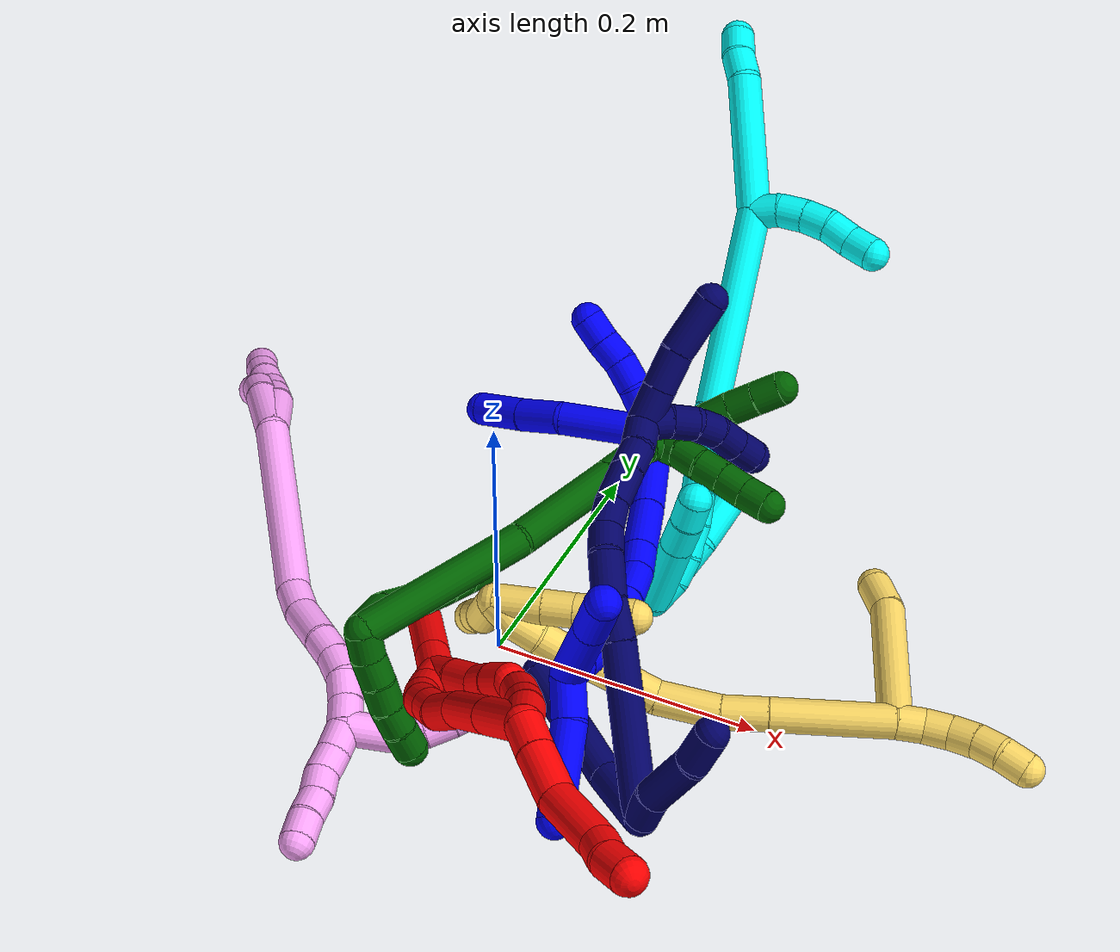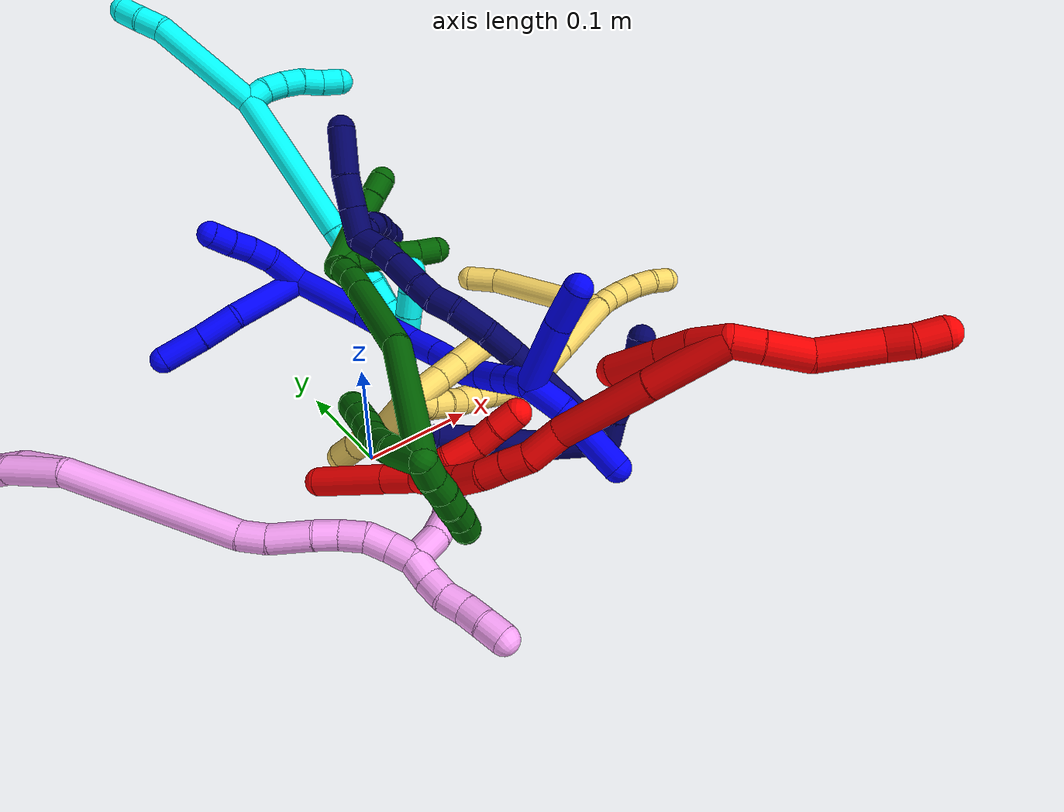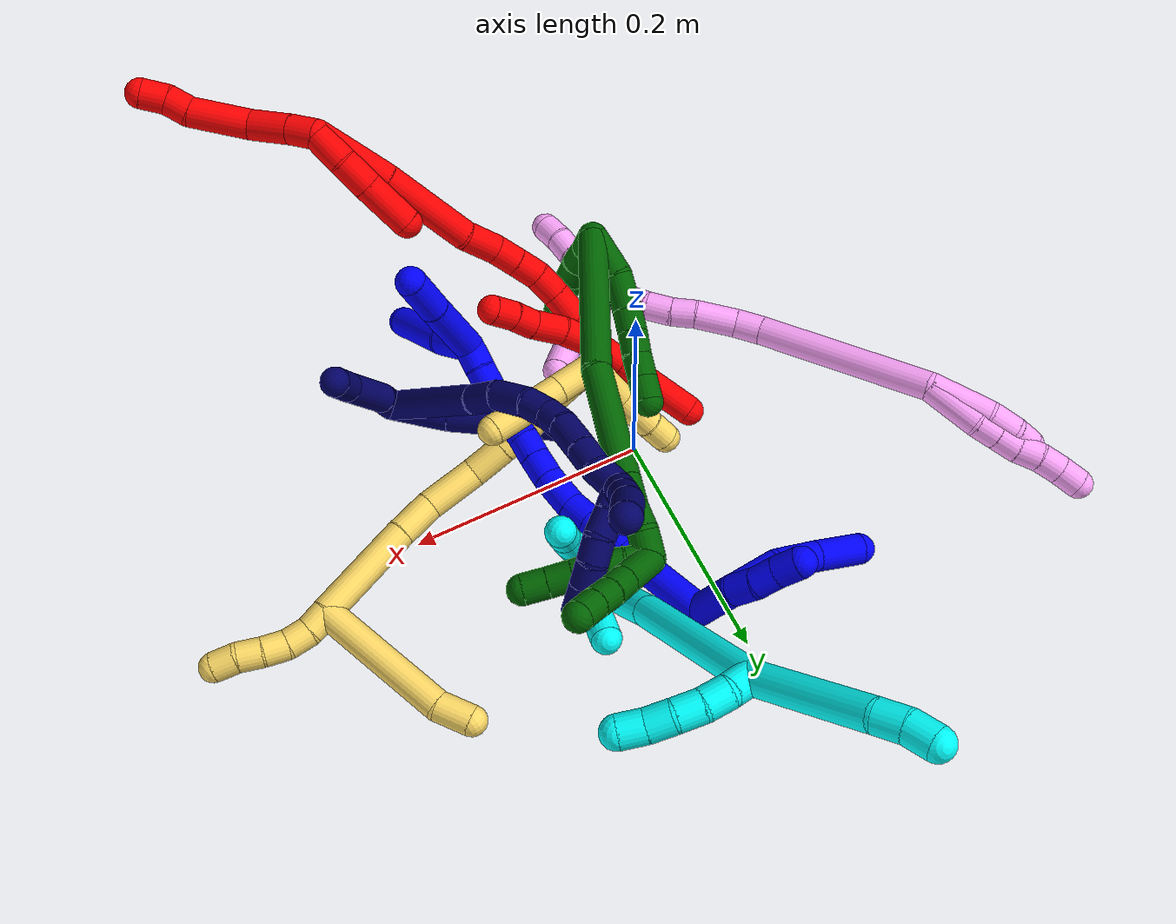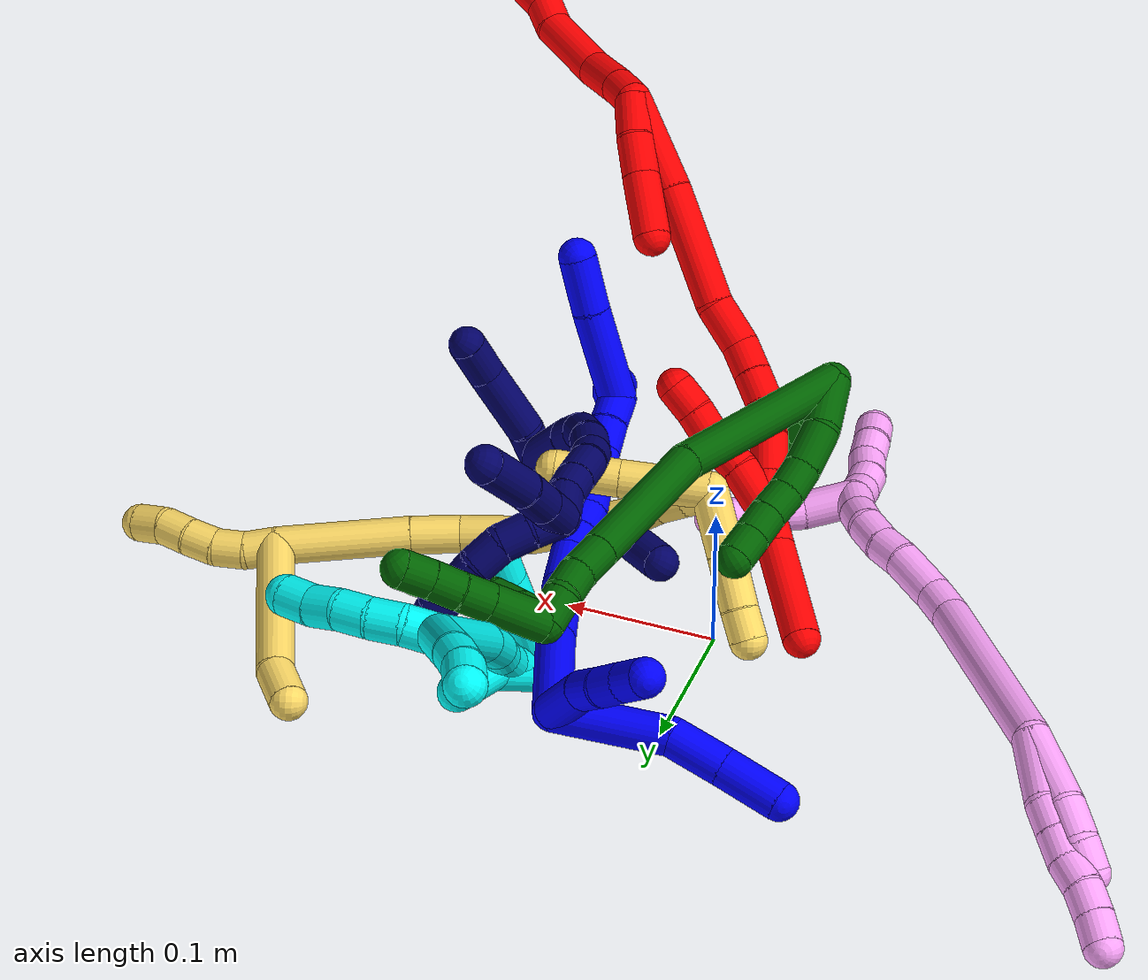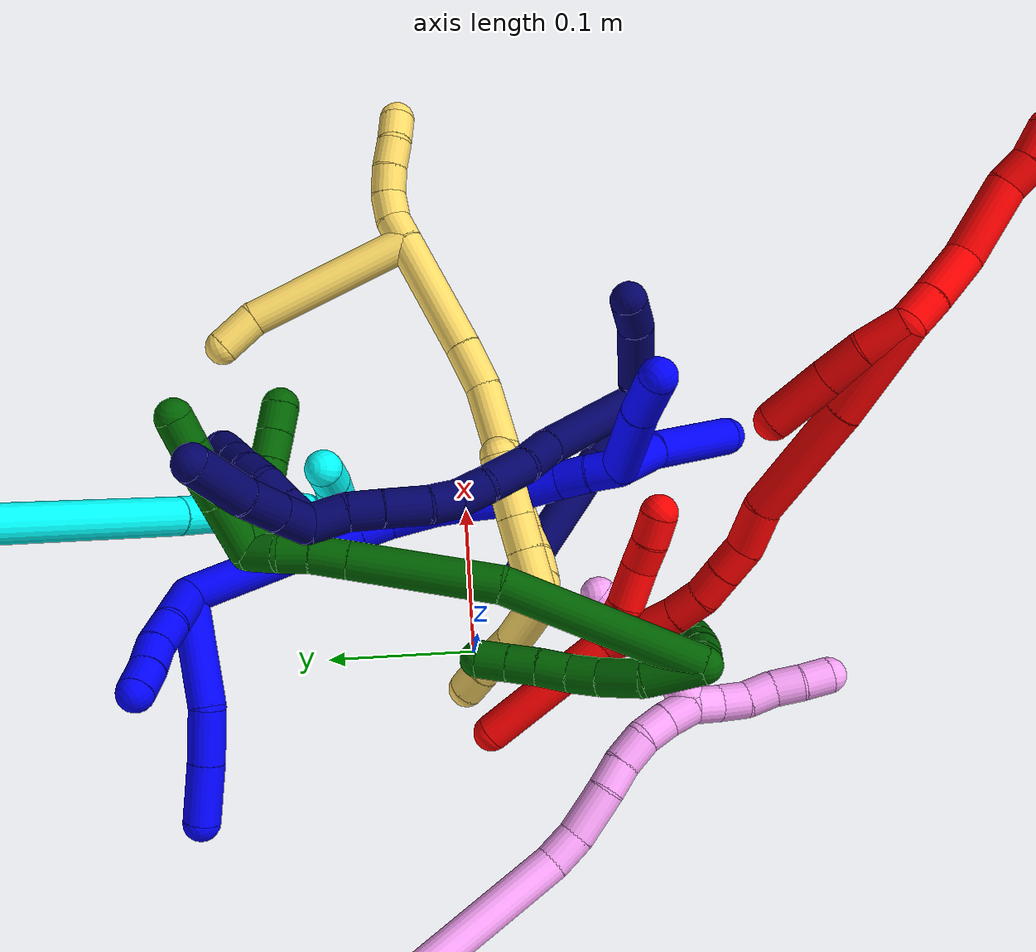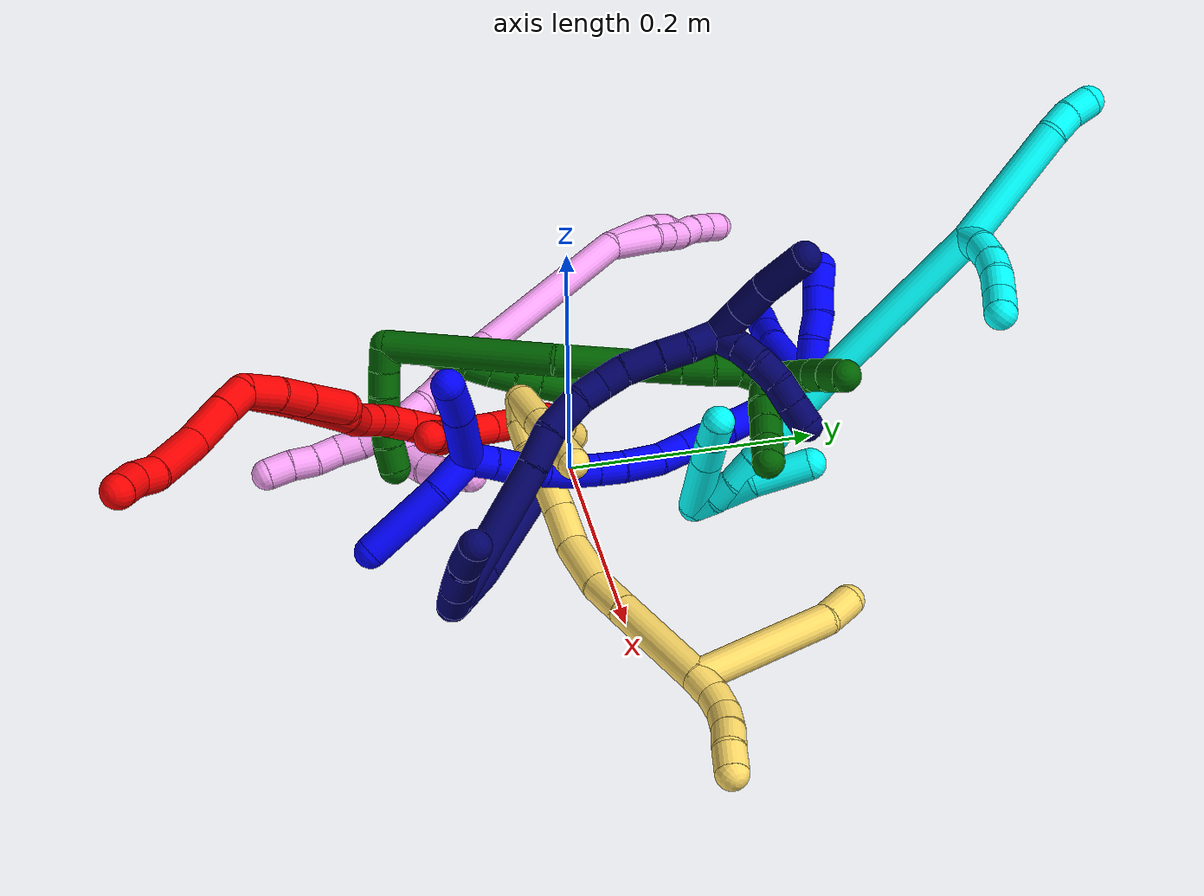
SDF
<sdf version="1.7">
 <world name="default">
  <plugin name="TubeGeneratorPlugin" filename="libtube_generator_plugin.so"/>
  <model name="photoneo_s_sensor">
   <static>1</static>
   <pose>0 0 2 1.57079 1.57079 3.14159</pose>
   <link name="link">
    <inertial><mass>0.1</mass></inertial>
    <sensor name="sensor" type="depth">
     <update_rate>30</update_rate>
     <camera>
      <horizontal_fov>1.22</horizontal_fov>
      <image><width>1920</width><height>1200</height><format>B8G8R8</format></image>
      <clip><near>0.1</near><far>4</far></clip>
      <depth_camera><output>points</output></depth_camera>
     </camera>
     <plugin name="camera_plugin" filename="libgazebo_ros_depth_camera.so">
      <baseline>0.2</baseline>
      <alwaysOn>1</alwaysOn>
      <updateRate>0.0</updateRate>
      <cameraName>camera_ir</cameraName>
      <imageTopicName>/camera/color/image_raw</imageTopicName>
      <cameraInfoTopicName>/camera/color/camera_info</cameraInfoTopicName>
      <depthImageTopicName>/camera/depth/image_raw</depthImageTopicName>
      <depthImageCameraInfoTopicName>/camera/depth/camera_info</depthImageCameraInfoTopicName>
      <pointCloudTopicName>/camera/depth/points</pointCloudTopicName>
      <frameName>fr_optical</frameName>
      <pointCloudCutoff>0.1</pointCloudCutoff>
      <pointCloudCutoffMax>2.0</pointCloudCutoffMax>
      <distortionK1>0</distortionK1>
      <distortionK2>0</distortionK2>
      <distortionK3>0</distortionK3>
      <distortionT1>0</distortionT1>
      <distortionT2>0</distortionT2>
      <CxPrime>0</CxPrime>
      <Cx>0</Cx>
      <Cy>0</Cy>
      <focalLength>0</focalLength>
      <hackBaseline>0</hackBaseline>
     </plugin>
    </sensor>
   </link>
  </model>
  <gravity>0 0 -9.8</gravity>
  <magnetic_field>6e-06 2.3e-05 -4.2e-05</magnetic_field>
  <atmosphere type="adiabatic"/>
  <physics name="default_physics" default="0" type="ode">
   <max_step_size>0.003</max_step_size>
   <real_time_factor>1</real_time_factor>
   <real_time_update_rate>1000</real_time_update_rate>
   <max_contacts>10000</max_contacts>
   <ode>
    <solver>
     <type>quick</type>
     <iters>100</iters>
     <sor>1.3</sor>
     <use_dynamic_moi_rescaling>0</use_dynamic_moi_rescaling>
    </solver>
    <constraints>
     <contact_max_correcting_vel>0</contact_max_correcting_vel>
     <contact_surface_layer>0.001</contact_surface_layer>
     <cfm>0</cfm>
     <erp>0.2</erp>
    </constraints>
   </ode>
  </physics>
  <scene><ambient>0.4 0.4 0.4 1</ambient><background>0.7 0.7 0.7 1</background><shadows>0</shadows></scene>
  <audio><device>default</device></audio>
  <spherical_coordinates>
   <surface_model>EARTH_WGS84</surface_model>
   <latitude_deg>0</latitude_deg>
   <longitude_deg>0</longitude_deg>
   <elevation>0</elevation>
   <heading_deg>0</heading_deg>
  </spherical_coordinates>
  <model name="bin">
   <static>1</static>
   <link name="bottom">
    <collision name="collision-bottom">
     <pose>0 0 -0.01 0 -0 0</pose>
     <geometry><box><size>0.8 0.6 0.02</size></box></geometry>
     <surface>
      <friction><ode><mu>100</mu><mu2>100</mu2></ode></friction>
      <contact><collide_bitmask>65535</collide_bitmask></contact>
     </surface>
    </collision>
   </link>
   <link name="west_wall">
    <collision name="collision-west_wall">
     <pose>-0.41 0 0.1 0 -0 0</pose>
     <geometry><box><size>0.02 0.6 0.2</size></box></geometry>
     <surface>
      <friction><ode><mu>100</mu><mu2>100</mu2></ode></friction>
      <contact><collide_bitmask>65535</collide_bitmask></contact>
     </surface>
    </collision>
   </link>
   <link name="east_wall">
    <collision name="collision-east_wall">
     <pose>0.41 0 0.1 0 -0 0</pose>
     <geometry><box><size>0.02 0.6 0.2</size></box></geometry>
     <surface>
      <friction><ode><mu>100</mu><mu2>100</mu2></ode></friction>
      <contact><collide_bitmask>65535</collide_bitmask></contact>
     </surface>
    </collision>
   </link>
   <link name="south_wall">
    <collision name="collision-south_wall">
     <pose>0 -0.31 0.1 0 -0 0</pose>
     <geometry><box><size>0.8 0.02 0.2</size></box></geometry>
     <surface>
      <friction><ode><mu>100</mu><mu2>100</mu2></ode></friction>
      <contact><collide_bitmask>65535</collide_bitmask></contact>
     </surface>
    </collision>
   </link>
   <link name="north_wall">
    <collision name="collision-north_wall">
     <pose>0 0.31 0.1 0 -0 0</pose>
     <geometry><box><size>0.8 0.02 0.2</size></box></geometry>
     <surface>
      <friction><ode><mu>100</mu><mu2>100</mu2></ode></friction>
      <contact><collide_bitmask>65535</collide_bitmask></contact>
     </surface>
    </collision>
   </link>
  </model>
  <model name="1">
   <static>0</static>
   <link name="1">
    <collision name="collision-cylinder-e_1_2_8">
     <pose>0.033785 0.003104 -0.014801 -2.93489 1.14992 -2.82415</pose>
     <geometry><cylinder><radius>0.0125</radius><length>0.07403</length></cylinder></geometry>
     <surface>
      <friction><ode><mu>1.16</mu><mu2>1.16</mu2><slip1>0</slip1><slip2>0</slip2></ode></friction>
      <contact><ode><kp>1e+06</kp><kd>1</kd><max_vel>0</max_vel><min_depth>0.001</min_depth></ode></contact>
     </surface>
    </collision>
    <visual name="visual-cylinder-e_1_2_8">
     <pose>0.033785 0.003104 -0.014801 -2.93489 1.14992 -2.82415</pose>
     <geometry><cylinder><radius>0.0125</radius><length>0.07403</length></cylinder></geometry>
     <material><ambient>0 0 1 1</ambient></material>
    </visual>
    <collision name="collision-cylinder-e_2_8_9">
     <pose>0.082108 0.013082 -0.037911 -2.45038 0.932558 -1.89962</pose>
     <geometry><cylinder><radius>0.0125</radius><length>0.036203</length></cylinder></geometry>
     <surface>
      <friction><ode><mu>1.16</mu><mu2>1.16</mu2><slip1>0</slip1><slip2>0</slip2></ode></friction>
      <contact><ode><kp>1e+06</kp><kd>1</kd><max_vel>0</max_vel><min_depth>0.001</min_depth></ode></contact>
     </surface>
    </collision>
    <visual name="visual-cylinder-e_2_8_9">
     <pose>0.082108 0.013082 -0.037911 -2.45038 0.932558 -1.89962</pose>
     <geometry><cylinder><radius>0.0125</radius><length>0.036203</length></cylinder></geometry>
     <material><ambient>0 0 1 1</ambient></material>
    </visual>
    <collision name="collision-cylinder-e_3_9_6">
     <pose>0.112041 0.027447 -0.056332 -2.5041 0.885546 -1.92559</pose>
     <geometry><cylinder><radius>0.0125</radius><length>0.039767</length></cylinder></geometry>
     <surface>
      <friction><ode><mu>1.16</mu><mu2>1.16</mu2><slip1>0</slip1><slip2>0</slip2></ode></friction>
      <contact><ode><kp>1e+06</kp><kd>1</kd><max_vel>0</max_vel><min_depth>0.001</min_depth></ode></contact>
     </surface>
    </collision>
    <visual name="visual-cylinder-e_3_9_6">
     <pose>0.112041 0.027447 -0.056332 -2.5041 0.885546 -1.92559</pose>
     <geometry><cylinder><radius>0.0125</radius><length>0.039767</length></cylinder></geometry>
     <material><ambient>0 0 1 1</ambient></material>
    </visual>
    <collision name="collision-cylinder-e_1_2_10">
     <pose>0.005414 -0.011645 -0.014295 2.45801 0.285606 0.768173</pose>
     <geometry><cylinder><radius>0.0125</radius><length>0.038433</length></cylinder></geometry>
     <surface>
      <friction><ode><mu>1.16</mu><mu2>1.16</mu2><slip1>0</slip1><slip2>0</slip2></ode></friction>
      <contact><ode><kp>1e+06</kp><kd>1</kd><max_vel>0</max_vel><min_depth>0.001</min_depth></ode></contact>
     </surface>
    </collision>
    <visual name="visual-cylinder-e_1_2_10">
     <pose>0.005414 -0.011645 -0.014295 2.45801 0.285606 0.768173</pose>
     <geometry><cylinder><radius>0.0125</radius><length>0.038433</length></cylinder></geometry>
     <material><ambient>0 0 1 1</ambient></material>
    </visual>
    <collision name="collision-cylinder-e_2_10_11">
     <pose>0.014428 -0.027484 -0.037782 2.7135 0.342324 1.3436</pose>
     <geometry><cylinder><radius>0.0125</radius><length>0.02145</length></cylinder></geometry>
     <surface>
      <friction><ode><mu>1.16</mu><mu2>1.16</mu2><slip1>0</slip1><slip2>0</slip2></ode></friction>
      <contact><ode><kp>1e+06</kp><kd>1</kd><max_vel>0</max_vel><min_depth>0.001</min_depth></ode></contact>
     </surface>
    </collision>
    <visual name="visual-cylinder-e_2_10_11">
     <pose>0.014428 -0.027484 -0.037782 2.7135 0.342324 1.3436</pose>
     <geometry><cylinder><radius>0.0125</radius><length>0.02145</length></cylinder></geometry>
     <material><ambient>0 0 1 1</ambient></material>
    </visual>
    <collision name="collision-cylinder-e_3_11_12">
     <pose>0.023116 -0.035866 -0.054502 2.63402 0.53344 1.6228</pose>
     <geometry><cylinder><radius>0.0125</radius><length>0.020012</length></cylinder></geometry>
     <surface>
      <friction><ode><mu>1.16</mu><mu2>1.16</mu2><slip1>0</slip1><slip2>0</slip2></ode></friction>
      <contact><ode><kp>1e+06</kp><kd>1</kd><max_vel>0</max_vel><min_depth>0.001</min_depth></ode></contact>
     </surface>
    </collision>
    <visual name="visual-cylinder-e_3_11_12">
     <pose>0.023116 -0.035866 -0.054502 2.63402 0.53344 1.6228</pose>
     <geometry><cylinder><radius>0.0125</radius><length>0.020012</length></cylinder></geometry>
     <material><ambient>0 0 1 1</ambient></material>
    </visual>
    <collision name="collision-cylinder-e_4_12_5">
     <pose>0.032384 -0.044156 -0.070202 2.67625 0.42878 1.48628</pose>
     <geometry><cylinder><radius>0.0125</radius><length>0.020105</length></cylinder></geometry>
     <surface>
      <friction><ode><mu>1.16</mu><mu2>1.16</mu2><slip1>0</slip1><slip2>0</slip2></ode></friction>
      <contact><ode><kp>1e+06</kp><kd>1</kd><max_vel>0</max_vel><min_depth>0.001</min_depth></ode></contact>
     </surface>
    </collision>
    <visual name="visual-cylinder-e_4_12_5">
     <pose>0.032384 -0.044156 -0.070202 2.67625 0.42878 1.48628</pose>
     <geometry><cylinder><radius>0.0125</radius><length>0.020105</length></cylinder></geometry>
     <material><ambient>0 0 1 1</ambient></material>
    </visual>
    <collision name="collision-cylinder-e_1_2_13">
     <pose>0.008177 -0.010241 0.037172 0.268831 0.208972 0.028361</pose>
     <geometry><cylinder><radius>0.0125</radius><length>0.078829</length></cylinder></geometry>
     <surface>
      <friction><ode><mu>1.16</mu><mu2>1.16</mu2><slip1>0</slip1><slip2>0</slip2></ode></friction>
      <contact><ode><kp>1e+06</kp><kd>1</kd><max_vel>0</max_vel><min_depth>0.001</min_depth></ode></contact>
     </surface>
    </collision>
    <visual name="visual-cylinder-e_1_2_13">
     <pose>0.008177 -0.010241 0.037172 0.268831 0.208972 0.028361</pose>
     <geometry><cylinder><radius>0.0125</radius><length>0.078829</length></cylinder></geometry>
     <material><ambient>0 0 1 1</ambient></material>
    </visual>
    <collision name="collision-cylinder-e_2_13_14">
     <pose>0.02138 -0.02552 0.093096 0.262449 0.253319 0.033611</pose>
     <geometry><cylinder><radius>0.0125</radius><length>0.040113</length></cylinder></geometry>
     <surface>
      <friction><ode><mu>1.16</mu><mu2>1.16</mu2><slip1>0</slip1><slip2>0</slip2></ode></friction>
      <contact><ode><kp>1e+06</kp><kd>1</kd><max_vel>0</max_vel><min_depth>0.001</min_depth></ode></contact>
     </surface>
    </collision>
    <visual name="visual-cylinder-e_2_13_14">
     <pose>0.02138 -0.02552 0.093096 0.262449 0.253319 0.033611</pose>
     <geometry><cylinder><radius>0.0125</radius><length>0.040113</length></cylinder></geometry>
     <material><ambient>0 0 1 1</ambient></material>
    </visual>
    <collision name="collision-cylinder-e_3_14_15">
     <pose>0.028891 -0.033508 0.122177 0.278254 0.227298 0.031964</pose>
     <geometry><cylinder><radius>0.0125</radius><length>0.022051</length></cylinder></geometry>
     <surface>
      <friction><ode><mu>1.16</mu><mu2>1.16</mu2><slip1>0</slip1><slip2>0</slip2></ode></friction>
      <contact><ode><kp>1e+06</kp><kd>1</kd><max_vel>0</max_vel><min_depth>0.001</min_depth></ode></contact>
     </surface>
    </collision>
    <visual name="visual-cylinder-e_3_14_15">
     <pose>0.028891 -0.033508 0.122177 0.278254 0.227298 0.031964</pose>
     <geometry><cylinder><radius>0.0125</radius><length>0.022051</length></cylinder></geometry>
     <material><ambient>0 0 1 1</ambient></material>
    </visual>
    <collision name="collision-cylinder-e_4_15_16">
     <pose>0.03632 -0.043026 0.145481 0.468573 0.327703 0.078879</pose>
     <geometry><cylinder><radius>0.0125</radius><length>0.030721</length></cylinder></geometry>
     <surface>
      <friction><ode><mu>1.16</mu><mu2>1.16</mu2><slip1>0</slip1><slip2>0</slip2></ode></friction>
      <contact><ode><kp>1e+06</kp><kd>1</kd><max_vel>0</max_vel><min_depth>0.001</min_depth></ode></contact>
     </surface>
    </collision>
    <visual name="visual-cylinder-e_4_15_16">
     <pose>0.03632 -0.043026 0.145481 0.468573 0.327703 0.078879</pose>
     <geometry><cylinder><radius>0.0125</radius><length>0.030721</length></cylinder></geometry>
     <material><ambient>0 0 1 1</ambient></material>
    </visual>
    <collision name="collision-cylinder-e_5_16_17">
     <pose>0.045484 -0.054195 0.166486 0.520336 0.427888 0.115546</pose>
     <geometry><cylinder><radius>0.0125</radius><length>0.020341</length></cylinder></geometry>
     <surface>
      <friction><ode><mu>1.16</mu><mu2>1.16</mu2><slip1>0</slip1><slip2>0</slip2></ode></friction>
      <contact><ode><kp>1e+06</kp><kd>1</kd><max_vel>0</max_vel><min_depth>0.001</min_depth></ode></contact>
     </surface>
    </collision>
    <visual name="visual-cylinder-e_5_16_17">
     <pose>0.045484 -0.054195 0.166486 0.520336 0.427888 0.115546</pose>
     <geometry><cylinder><radius>0.0125</radius><length>0.020341</length></cylinder></geometry>
     <material><ambient>0 0 1 1</ambient></material>
    </visual>
    <collision name="collision-cylinder-e_6_17_18">
     <pose>0.054453 -0.063417 0.182534 0.522851 0.474021 0.129073</pose>
     <geometry><cylinder><radius>0.0125</radius><length>0.020804</length></cylinder></geometry>
     <surface>
      <friction><ode><mu>1.16</mu><mu2>1.16</mu2><slip1>0</slip1><slip2>0</slip2></ode></friction>
      <contact><ode><kp>1e+06</kp><kd>1</kd><max_vel>0</max_vel><min_depth>0.001</min_depth></ode></contact>
     </surface>
    </collision>
    <visual name="visual-cylinder-e_6_17_18">
     <pose>0.054453 -0.063417 0.182534 0.522851 0.474021 0.129073</pose>
     <geometry><cylinder><radius>0.0125</radius><length>0.020804</length></cylinder></geometry>
     <material><ambient>0 0 1 1</ambient></material>
    </visual>
    <collision name="collision-cylinder-e_7_18_19">
     <pose>0.06234 -0.07551 0.198571 0.750095 0.278948 0.110422</pose>
     <geometry><cylinder><radius>0.0125</radius><length>0.022803</length></cylinder></geometry>
     <surface>
      <friction><ode><mu>1.16</mu><mu2>1.16</mu2><slip1>0</slip1><slip2>0</slip2></ode></friction>
      <contact><ode><kp>1e+06</kp><kd>1</kd><max_vel>0</max_vel><min_depth>0.001</min_depth></ode></contact>
     </surface>
    </collision>
    <visual name="visual-cylinder-e_7_18_19">
     <pose>0.06234 -0.07551 0.198571 0.750095 0.278948 0.110422</pose>
     <geometry><cylinder><radius>0.0125</radius><length>0.022803</length></cylinder></geometry>
     <material><ambient>0 0 1 1</ambient></material>
    </visual>
    <collision name="collision-cylinder-e_8_19_20">
     <pose>0.068953 -0.090746 0.214374 0.784096 0.306052 0.127362</pose>
     <geometry><cylinder><radius>0.0125</radius><length>0.023058</length></cylinder></geometry>
     <surface>
      <friction><ode><mu>1.16</mu><mu2>1.16</mu2><slip1>0</slip1><slip2>0</slip2></ode></friction>
      <contact><ode><kp>1e+06</kp><kd>1</kd><max_vel>0</max_vel><min_depth>0.001</min_depth></ode></contact>
     </surface>
    </collision>
    <visual name="visual-cylinder-e_8_19_20">
     <pose>0.068953 -0.090746 0.214374 0.784096 0.306052 0.127362</pose>
     <geometry><cylinder><radius>0.0125</radius><length>0.023058</length></cylinder></geometry>
     <material><ambient>0 0 1 1</ambient></material>
    </visual>
    <collision name="collision-cylinder-e_9_20_21">
     <pose>0.075873 -0.106253 0.228345 0.89666 0.334567 0.162088</pose>
     <geometry><cylinder><radius>0.0125</radius><length>0.02099</length></cylinder></geometry>
     <surface>
      <friction><ode><mu>1.16</mu><mu2>1.16</mu2><slip1>0</slip1><slip2>0</slip2></ode></friction>
      <contact><ode><kp>1e+06</kp><kd>1</kd><max_vel>0</max_vel><min_depth>0.001</min_depth></ode></contact>
     </surface>
    </collision>
    <visual name="visual-cylinder-e_9_20_21">
     <pose>0.075873 -0.106253 0.228345 0.89666 0.334567 0.162088</pose>
     <geometry><cylinder><radius>0.0125</radius><length>0.02099</length></cylinder></geometry>
     <material><ambient>0 0 1 1</ambient></material>
    </visual>
    <collision name="collision-cylinder-e_10_21_1">
     <pose>0.083282 -0.120814 0.240917 0.818123 0.401373 0.175921</pose>
     <geometry><cylinder><radius>0.0125</radius><length>0.020289</length></cylinder></geometry>
     <surface>
      <friction><ode><mu>1.16</mu><mu2>1.16</mu2><slip1>0</slip1><slip2>0</slip2></ode></friction>
      <contact><ode><kp>1e+06</kp><kd>1</kd><max_vel>0</max_vel><min_depth>0.001</min_depth></ode></contact>
     </surface>
    </collision>
    <visual name="visual-cylinder-e_10_21_1">
     <pose>0.083282 -0.120814 0.240917 0.818123 0.401373 0.175921</pose>
     <geometry><cylinder><radius>0.0125</radius><length>0.020289</length></cylinder></geometry>
     <material><ambient>0 0 1 1</ambient></material>
    </visual>
    <collision name="collision-cylinder-e_1_1_22">
     <pose>0.076332 -0.157318 0.246619 1.59374 -0.352175 -0.360176</pose>
     <geometry><cylinder><radius>0.0125</radius><length>0.063277</length></cylinder></geometry>
     <surface>
      <friction><ode><mu>1.16</mu><mu2>1.16</mu2><slip1>0</slip1><slip2>0</slip2></ode></friction>
      <contact><ode><kp>1e+06</kp><kd>1</kd><max_vel>0</max_vel><min_depth>0.001</min_depth></ode></contact>
     </surface>
    </collision>
    <visual name="visual-cylinder-e_1_1_22">
     <pose>0.076332 -0.157318 0.246619 1.59374 -0.352175 -0.360176</pose>
     <geometry><cylinder><radius>0.0125</radius><length>0.063277</length></cylinder></geometry>
     <material><ambient>0 0 1 1</ambient></material>
    </visual>
    <collision name="collision-cylinder-e_2_22_4">
     <pose>0.059982 -0.204533 0.246602 1.5329 -0.300598 -0.289577</pose>
     <geometry><cylinder><radius>0.0125</radius><length>0.036723</length></cylinder></geometry>
     <surface>
      <friction><ode><mu>1.16</mu><mu2>1.16</mu2><slip1>0</slip1><slip2>0</slip2></ode></friction>
      <contact><ode><kp>1e+06</kp><kd>1</kd><max_vel>0</max_vel><min_depth>0.001</min_depth></ode></contact>
     </surface>
    </collision>
    <visual name="visual-cylinder-e_2_22_4">
     <pose>0.059982 -0.204533 0.246602 1.5329 -0.300598 -0.289577</pose>
     <geometry><cylinder><radius>0.0125</radius><length>0.036723</length></cylinder></geometry>
     <material><ambient>0 0 1 1</ambient></material>
    </visual>
    <collision name="collision-cylinder-e_1_1_23">
     <pose>0.088851 -0.125325 0.263553 -0.140853 0.097467 -0.006881</pose>
     <geometry><cylinder><radius>0.0125</radius><length>0.032988</length></cylinder></geometry>
     <surface>
      <friction><ode><mu>1.16</mu><mu2>1.16</mu2><slip1>0</slip1><slip2>0</slip2></ode></friction>
      <contact><ode><kp>1e+06</kp><kd>1</kd><max_vel>0</max_vel><min_depth>0.001</min_depth></ode></contact>
     </surface>
    </collision>
    <visual name="visual-cylinder-e_1_1_23">
     <pose>0.088851 -0.125325 0.263553 -0.140853 0.097467 -0.006881</pose>
     <geometry><cylinder><radius>0.0125</radius><length>0.032988</length></cylinder></geometry>
     <material><ambient>0 0 1 1</ambient></material>
    </visual>
    <collision name="collision-cylinder-e_2_23_3">
     <pose>0.100278 -0.116638 0.311198 -0.200583 0.297505 -0.030158</pose>
     <geometry><cylinder><radius>0.0125</radius><length>0.067012</length></cylinder></geometry>
     <surface>
      <friction><ode><mu>1.16</mu><mu2>1.16</mu2><slip1>0</slip1><slip2>0</slip2></ode></friction>
      <contact><ode><kp>1e+06</kp><kd>1</kd><max_vel>0</max_vel><min_depth>0.001</min_depth></ode></contact>
     </surface>
    </collision>
    <visual name="visual-cylinder-e_2_23_3">
     <pose>0.100278 -0.116638 0.311198 -0.200583 0.297505 -0.030158</pose>
     <geometry><cylinder><radius>0.0125</radius><length>0.067012</length></cylinder></geometry>
     <material><ambient>0 0 1 1</ambient></material>
    </visual>
    <collision name="collision-sphere-3">
     <pose>0.110099 -0.110255 0.34259 0 -0 0</pose>
     <geometry><sphere><radius>0.0125</radius></sphere></geometry>
     <surface>
      <friction><ode><mu>1.16</mu><mu2>1.16</mu2><slip1>0</slip1><slip2>0</slip2></ode></friction>
      <contact><ode><kp>1e+06</kp><kd>1</kd><max_vel>0</max_vel><min_depth>0.001</min_depth></ode></contact>
     </surface>
    </collision>
    <visual name="visual-sphere-3">
     <pose>0.110099 -0.110255 0.34259 0 -0 0</pose>
     <geometry><sphere><radius>0.0125</radius></sphere></geometry>
     <material><ambient>0 0 1 1</ambient></material>
    </visual>
    <collision name="collision-sphere-23">
     <pose>0.090456 -0.12302 0.279807 0 -0 0</pose>
     <geometry><sphere><radius>0.0125</radius></sphere></geometry>
     <surface>
      <friction><ode><mu>1.16</mu><mu2>1.16</mu2><slip1>0</slip1><slip2>0</slip2></ode></friction>
      <contact><ode><kp>1e+06</kp><kd>1</kd><max_vel>0</max_vel><min_depth>0.001</min_depth></ode></contact>
     </surface>
    </collision>
    <visual name="visual-sphere-23">
     <pose>0.090456 -0.12302 0.279807 0 -0 0</pose>
     <geometry><sphere><radius>0.0125</radius></sphere></geometry>
     <material><ambient>0 0 1 1</ambient></material>
    </visual>
    <collision name="collision-sphere-4">
     <pose>0.054545 -0.222058 0.247266 0 -0 0</pose>
     <geometry><sphere><radius>0.0125</radius></sphere></geometry>
     <surface>
      <friction><ode><mu>1.16</mu><mu2>1.16</mu2><slip1>0</slip1><slip2>0</slip2></ode></friction>
      <contact><ode><kp>1e+06</kp><kd>1</kd><max_vel>0</max_vel><min_depth>0.001</min_depth></ode></contact>
     </surface>
    </collision>
    <visual name="visual-sphere-4">
     <pose>0.054545 -0.222058 0.247266 0 -0 0</pose>
     <geometry><sphere><radius>0.0125</radius></sphere></geometry>
     <material><ambient>0 0 1 1</ambient></material>
    </visual>
    <collision name="collision-sphere-22">
     <pose>0.065419 -0.187007 0.245938 0 -0 0</pose>
     <geometry><sphere><radius>0.0125</radius></sphere></geometry>
     <surface>
      <friction><ode><mu>1.16</mu><mu2>1.16</mu2><slip1>0</slip1><slip2>0</slip2></ode></friction>
      <contact><ode><kp>1e+06</kp><kd>1</kd><max_vel>0</max_vel><min_depth>0.001</min_depth></ode></contact>
     </surface>
    </collision>
    <visual name="visual-sphere-22">
     <pose>0.065419 -0.187007 0.245938 0 -0 0</pose>
     <geometry><sphere><radius>0.0125</radius></sphere></geometry>
     <material><ambient>0 0 1 1</ambient></material>
    </visual>
    <collision name="collision-sphere-1">
     <pose>0.087246 -0.127629 0.2473 0 -0 0</pose>
     <geometry><sphere><radius>0.0125</radius></sphere></geometry>
     <surface>
      <friction><ode><mu>1.16</mu><mu2>1.16</mu2><slip1>0</slip1><slip2>0</slip2></ode></friction>
      <contact><ode><kp>1e+06</kp><kd>1</kd><max_vel>0</max_vel><min_depth>0.001</min_depth></ode></contact>
     </surface>
    </collision>
    <visual name="visual-sphere-1">
     <pose>0.087246 -0.127629 0.2473 0 -0 0</pose>
     <geometry><sphere><radius>0.0125</radius></sphere></geometry>
     <material><ambient>0 0 1 1</ambient></material>
    </visual>
    <collision name="collision-sphere-21">
     <pose>0.079319 -0.113998 0.234533 0 -0 0</pose>
     <geometry><sphere><radius>0.0125</radius></sphere></geometry>
     <surface>
      <friction><ode><mu>1.16</mu><mu2>1.16</mu2><slip1>0</slip1><slip2>0</slip2></ode></friction>
      <contact><ode><kp>1e+06</kp><kd>1</kd><max_vel>0</max_vel><min_depth>0.001</min_depth></ode></contact>
     </surface>
    </collision>
    <visual name="visual-sphere-21">
     <pose>0.079319 -0.113998 0.234533 0 -0 0</pose>
     <geometry><sphere><radius>0.0125</radius></sphere></geometry>
     <material><ambient>0 0 1 1</ambient></material>
    </visual>
    <collision name="collision-sphere-11">
     <pose>0.018028 -0.031678 -0.046972 0 -0 0</pose>
     <geometry><sphere><radius>0.0125</radius></sphere></geometry>
     <surface>
      <friction><ode><mu>1.16</mu><mu2>1.16</mu2><slip1>0</slip1><slip2>0</slip2></ode></friction>
      <contact><ode><kp>1e+06</kp><kd>1</kd><max_vel>0</max_vel><min_depth>0.001</min_depth></ode></contact>
     </surface>
    </collision>
    <visual name="visual-sphere-11">
     <pose>0.018028 -0.031678 -0.046972 0 -0 0</pose>
     <geometry><sphere><radius>0.0125</radius></sphere></geometry>
     <material><ambient>0 0 1 1</ambient></material>
    </visual>
    <collision name="collision-sphere-10">
     <pose>0.010828 -0.02329 -0.028591 0 -0 0</pose>
     <geometry><sphere><radius>0.0125</radius></sphere></geometry>
     <surface>
      <friction><ode><mu>1.16</mu><mu2>1.16</mu2><slip1>0</slip1><slip2>0</slip2></ode></friction>
      <contact><ode><kp>1e+06</kp><kd>1</kd><max_vel>0</max_vel><min_depth>0.001</min_depth></ode></contact>
     </surface>
    </collision>
    <visual name="visual-sphere-10">
     <pose>0.010828 -0.02329 -0.028591 0 -0 0</pose>
     <geometry><sphere><radius>0.0125</radius></sphere></geometry>
     <material><ambient>0 0 1 1</ambient></material>
    </visual>
    <collision name="collision-sphere-6">
     <pose>0.127436 0.034936 -0.066444 0 -0 0</pose>
     <geometry><sphere><radius>0.0125</radius></sphere></geometry>
     <surface>
      <friction><ode><mu>1.16</mu><mu2>1.16</mu2><slip1>0</slip1><slip2>0</slip2></ode></friction>
      <contact><ode><kp>1e+06</kp><kd>1</kd><max_vel>0</max_vel><min_depth>0.001</min_depth></ode></contact>
     </surface>
    </collision>
    <visual name="visual-sphere-6">
     <pose>0.127436 0.034936 -0.066444 0 -0 0</pose>
     <geometry><sphere><radius>0.0125</radius></sphere></geometry>
     <material><ambient>0 0 1 1</ambient></material>
    </visual>
    <collision name="collision-sphere-9">
     <pose>0.096646 0.019957 -0.04622 0 -0 0</pose>
     <geometry><sphere><radius>0.0125</radius></sphere></geometry>
     <surface>
      <friction><ode><mu>1.16</mu><mu2>1.16</mu2><slip1>0</slip1><slip2>0</slip2></ode></friction>
      <contact><ode><kp>1e+06</kp><kd>1</kd><max_vel>0</max_vel><min_depth>0.001</min_depth></ode></contact>
     </surface>
    </collision>
    <visual name="visual-sphere-9">
     <pose>0.096646 0.019957 -0.04622 0 -0 0</pose>
     <geometry><sphere><radius>0.0125</radius></sphere></geometry>
     <material><ambient>0 0 1 1</ambient></material>
    </visual>
    <collision name="collision-sphere-2">
     <geometry><sphere><radius>0.0125</radius></sphere></geometry>
     <surface>
      <friction><ode><mu>1.16</mu><mu2>1.16</mu2><slip1>0</slip1><slip2>0</slip2></ode></friction>
      <contact><ode><kp>1e+06</kp><kd>1</kd><max_vel>0</max_vel><min_depth>0.001</min_depth></ode></contact>
     </surface>
    </collision>
    <visual name="visual-sphere-2">
     <geometry><sphere><radius>0.0125</radius></sphere></geometry>
     <material><ambient>0 0 1 1</ambient></material>
    </visual>
    <collision name="collision-sphere-19">
     <pose>0.065479 -0.082982 0.20659 0 -0 0</pose>
     <geometry><sphere><radius>0.0125</radius></sphere></geometry>
     <surface>
      <friction><ode><mu>1.16</mu><mu2>1.16</mu2><slip1>0</slip1><slip2>0</slip2></ode></friction>
      <contact><ode><kp>1e+06</kp><kd>1</kd><max_vel>0</max_vel><min_depth>0.001</min_depth></ode></contact>
     </surface>
    </collision>
    <visual name="visual-sphere-19">
     <pose>0.065479 -0.082982 0.20659 0 -0 0</pose>
     <geometry><sphere><radius>0.0125</radius></sphere></geometry>
     <material><ambient>0 0 1 1</ambient></material>
    </visual>
    <collision name="collision-sphere-8">
     <pose>0.06757 0.006207 -0.029602 0 -0 0</pose>
     <geometry><sphere><radius>0.0125</radius></sphere></geometry>
     <surface>
      <friction><ode><mu>1.16</mu><mu2>1.16</mu2><slip1>0</slip1><slip2>0</slip2></ode></friction>
      <contact><ode><kp>1e+06</kp><kd>1</kd><max_vel>0</max_vel><min_depth>0.001</min_depth></ode></contact>
     </surface>
    </collision>
    <visual name="visual-sphere-8">
     <pose>0.06757 0.006207 -0.029602 0 -0 0</pose>
     <geometry><sphere><radius>0.0125</radius></sphere></geometry>
     <material><ambient>0 0 1 1</ambient></material>
    </visual>
    <collision name="collision-sphere-12">
     <pose>0.028204 -0.040053 -0.062031 0 -0 0</pose>
     <geometry><sphere><radius>0.0125</radius></sphere></geometry>
     <surface>
      <friction><ode><mu>1.16</mu><mu2>1.16</mu2><slip1>0</slip1><slip2>0</slip2></ode></friction>
      <contact><ode><kp>1e+06</kp><kd>1</kd><max_vel>0</max_vel><min_depth>0.001</min_depth></ode></contact>
     </surface>
    </collision>
    <visual name="visual-sphere-12">
     <pose>0.028204 -0.040053 -0.062031 0 -0 0</pose>
     <geometry><sphere><radius>0.0125</radius></sphere></geometry>
     <material><ambient>0 0 1 1</ambient></material>
    </visual>
    <collision name="collision-sphere-5">
     <pose>0.036563 -0.048259 -0.078372 0 -0 0</pose>
     <geometry><sphere><radius>0.0125</radius></sphere></geometry>
     <surface>
      <friction><ode><mu>1.16</mu><mu2>1.16</mu2><slip1>0</slip1><slip2>0</slip2></ode></friction>
      <contact><ode><kp>1e+06</kp><kd>1</kd><max_vel>0</max_vel><min_depth>0.001</min_depth></ode></contact>
     </surface>
    </collision>
    <visual name="visual-sphere-5">
     <pose>0.036563 -0.048259 -0.078372 0 -0 0</pose>
     <geometry><sphere><radius>0.0125</radius></sphere></geometry>
     <material><ambient>0 0 1 1</ambient></material>
    </visual>
    <collision name="collision-sphere-13">
     <pose>0.016353 -0.020482 0.074345 0 -0 0</pose>
     <geometry><sphere><radius>0.0125</radius></sphere></geometry>
     <surface>
      <friction><ode><mu>1.16</mu><mu2>1.16</mu2><slip1>0</slip1><slip2>0</slip2></ode></friction>
      <contact><ode><kp>1e+06</kp><kd>1</kd><max_vel>0</max_vel><min_depth>0.001</min_depth></ode></contact>
     </surface>
    </collision>
    <visual name="visual-sphere-13">
     <pose>0.016353 -0.020482 0.074345 0 -0 0</pose>
     <geometry><sphere><radius>0.0125</radius></sphere></geometry>
     <material><ambient>0 0 1 1</ambient></material>
    </visual>
    <collision name="collision-sphere-14">
     <pose>0.026407 -0.030557 0.111848 0 -0 0</pose>
     <geometry><sphere><radius>0.0125</radius></sphere></geometry>
     <surface>
      <friction><ode><mu>1.16</mu><mu2>1.16</mu2><slip1>0</slip1><slip2>0</slip2></ode></friction>
      <contact><ode><kp>1e+06</kp><kd>1</kd><max_vel>0</max_vel><min_depth>0.001</min_depth></ode></contact>
     </surface>
    </collision>
    <visual name="visual-sphere-14">
     <pose>0.026407 -0.030557 0.111848 0 -0 0</pose>
     <geometry><sphere><radius>0.0125</radius></sphere></geometry>
     <material><ambient>0 0 1 1</ambient></material>
    </visual>
    <collision name="collision-sphere-15">
     <pose>0.031376 -0.036458 0.132506 0 -0 0</pose>
     <geometry><sphere><radius>0.0125</radius></sphere></geometry>
     <surface>
      <friction><ode><mu>1.16</mu><mu2>1.16</mu2><slip1>0</slip1><slip2>0</slip2></ode></friction>
      <contact><ode><kp>1e+06</kp><kd>1</kd><max_vel>0</max_vel><min_depth>0.001</min_depth></ode></contact>
     </surface>
    </collision>
    <visual name="visual-sphere-15">
     <pose>0.031376 -0.036458 0.132506 0 -0 0</pose>
     <geometry><sphere><radius>0.0125</radius></sphere></geometry>
     <material><ambient>0 0 1 1</ambient></material>
    </visual>
    <collision name="collision-sphere-16">
     <pose>0.041264 -0.049594 0.158457 0 -0 0</pose>
     <geometry><sphere><radius>0.0125</radius></sphere></geometry>
     <surface>
      <friction><ode><mu>1.16</mu><mu2>1.16</mu2><slip1>0</slip1><slip2>0</slip2></ode></friction>
      <contact><ode><kp>1e+06</kp><kd>1</kd><max_vel>0</max_vel><min_depth>0.001</min_depth></ode></contact>
     </surface>
    </collision>
    <visual name="visual-sphere-16">
     <pose>0.041264 -0.049594 0.158457 0 -0 0</pose>
     <geometry><sphere><radius>0.0125</radius></sphere></geometry>
     <material><ambient>0 0 1 1</ambient></material>
    </visual>
    <collision name="collision-sphere-17">
     <pose>0.049705 -0.058795 0.174515 0 -0 0</pose>
     <geometry><sphere><radius>0.0125</radius></sphere></geometry>
     <surface>
      <friction><ode><mu>1.16</mu><mu2>1.16</mu2><slip1>0</slip1><slip2>0</slip2></ode></friction>
      <contact><ode><kp>1e+06</kp><kd>1</kd><max_vel>0</max_vel><min_depth>0.001</min_depth></ode></contact>
     </surface>
    </collision>
    <visual name="visual-sphere-17">
     <pose>0.049705 -0.058795 0.174515 0 -0 0</pose>
     <geometry><sphere><radius>0.0125</radius></sphere></geometry>
     <material><ambient>0 0 1 1</ambient></material>
    </visual>
    <collision name="collision-sphere-18">
     <pose>0.059201 -0.068038 0.190552 0 -0 0</pose>
     <geometry><sphere><radius>0.0125</radius></sphere></geometry>
     <surface>
      <friction><ode><mu>1.16</mu><mu2>1.16</mu2><slip1>0</slip1><slip2>0</slip2></ode></friction>
      <contact><ode><kp>1e+06</kp><kd>1</kd><max_vel>0</max_vel><min_depth>0.001</min_depth></ode></contact>
     </surface>
    </collision>
    <visual name="visual-sphere-18">
     <pose>0.059201 -0.068038 0.190552 0 -0 0</pose>
     <geometry><sphere><radius>0.0125</radius></sphere></geometry>
     <material><ambient>0 0 1 1</ambient></material>
    </visual>
    <collision name="collision-sphere-20">
     <pose>0.072427 -0.098509 0.222157 0 -0 0</pose>
     <geometry><sphere><radius>0.0125</radius></sphere></geometry>
     <surface>
      <friction><ode><mu>1.16</mu><mu2>1.16</mu2><slip1>0</slip1><slip2>0</slip2></ode></friction>
      <contact><ode><kp>1e+06</kp><kd>1</kd><max_vel>0</max_vel><min_depth>0.001</min_depth></ode></contact>
     </surface>
    </collision>
    <visual name="visual-sphere-20">
     <pose>0.072427 -0.098509 0.222157 0 -0 0</pose>
     <geometry><sphere><radius>0.0125</radius></sphere></geometry>
     <material><ambient>0 0 1 1</ambient></material>
    </visual>
    <inertial>
     <pose>0.053134 -0.060097 0.114404 0 -0 0</pose>
     <mass>0.75</mass>
     <inertia><ixx>0.000117</ixx><ixy>0</ixy><ixz>0</ixz><iyy>0.000111</iyy><iyz>0</iyz><izz>-5e-06</izz></inertia>
    </inertial>
   </link>
   <pose>0.038833 0.185488 0.075037 -1.9198 0.132259 -2.60077</pose>
  </model>
  <model name="2">
   <static>0</static>
   <link name="2">
    <collision name="collision-cylinder-e_1_2_8">
     <pose>-0.001127 0.00439 0.010638 -0.391375 -0.097633 0.019368</pose>
     <geometry><cylinder><radius>0.0125</radius><length>0.023128</length></cylinder></geometry>
     <surface>
      <friction><ode><mu>1.16</mu><mu2>1.16</mu2><slip1>0</slip1><slip2>0</slip2></ode></friction>
      <contact><ode><kp>1e+06</kp><kd>1</kd><max_vel>0</max_vel><min_depth>0.001</min_depth></ode></contact>
     </surface>
    </collision>
    <visual name="visual-cylinder-e_1_2_8">
     <pose>-0.001127 0.00439 0.010638 -0.391375 -0.097633 0.019368</pose>
     <geometry><cylinder><radius>0.0125</radius><length>0.023128</length></cylinder></geometry>
     <material><ambient>1 0 0 1</ambient></material>
    </visual>
    <collision name="collision-cylinder-e_2_8_9">
     <pose>-0.004954 0.015936 0.037239 -0.421409 -0.153137 0.032814</pose>
     <geometry><cylinder><radius>0.0125</radius><length>0.0354</length></cylinder></geometry>
     <surface>
      <friction><ode><mu>1.16</mu><mu2>1.16</mu2><slip1>0</slip1><slip2>0</slip2></ode></friction>
      <contact><ode><kp>1e+06</kp><kd>1</kd><max_vel>0</max_vel><min_depth>0.001</min_depth></ode></contact>
     </surface>
    </collision>
    <visual name="visual-cylinder-e_2_8_9">
     <pose>-0.004954 0.015936 0.037239 -0.421409 -0.153137 0.032814</pose>
     <geometry><cylinder><radius>0.0125</radius><length>0.0354</length></cylinder></geometry>
     <material><ambient>1 0 0 1</ambient></material>
    </visual>
    <collision name="collision-cylinder-e_3_9_10">
     <pose>-0.013377 0.025053 0.0775 -0.080558 -0.230589 0.009334</pose>
     <geometry><cylinder><radius>0.0125</radius><length>0.05008</length></cylinder></geometry>
     <surface>
      <friction><ode><mu>1.16</mu><mu2>1.16</mu2><slip1>0</slip1><slip2>0</slip2></ode></friction>
      <contact><ode><kp>1e+06</kp><kd>1</kd><max_vel>0</max_vel><min_depth>0.001</min_depth></ode></contact>
     </surface>
    </collision>
    <visual name="visual-cylinder-e_3_9_10">
     <pose>-0.013377 0.025053 0.0775 -0.080558 -0.230589 0.009334</pose>
     <geometry><cylinder><radius>0.0125</radius><length>0.05008</length></cylinder></geometry>
     <material><ambient>1 0 0 1</ambient></material>
    </visual>
    <collision name="collision-cylinder-e_4_10_11">
     <pose>-0.018625 0.02657 0.111781 0.04448 0.047478 0.001056</pose>
     <geometry><cylinder><radius>0.0125</radius><length>0.020007</length></cylinder></geometry>
     <surface>
      <friction><ode><mu>1.16</mu><mu2>1.16</mu2><slip1>0</slip1><slip2>0</slip2></ode></friction>
      <contact><ode><kp>1e+06</kp><kd>1</kd><max_vel>0</max_vel><min_depth>0.001</min_depth></ode></contact>
     </surface>
    </collision>
    <visual name="visual-cylinder-e_4_10_11">
     <pose>-0.018625 0.02657 0.111781 0.04448 0.047478 0.001056</pose>
     <geometry><cylinder><radius>0.0125</radius><length>0.020007</length></cylinder></geometry>
     <material><ambient>1 0 0 1</ambient></material>
    </visual>
    <collision name="collision-cylinder-e_5_11_6">
     <pose>-0.020895 0.025744 0.132091 0.036989 -0.259541 -0.004828</pose>
     <geometry><cylinder><radius>0.0125</radius><length>0.021385</length></cylinder></geometry>
     <surface>
      <friction><ode><mu>1.16</mu><mu2>1.16</mu2><slip1>0</slip1><slip2>0</slip2></ode></friction>
      <contact><ode><kp>1e+06</kp><kd>1</kd><max_vel>0</max_vel><min_depth>0.001</min_depth></ode></contact>
     </surface>
    </collision>
    <visual name="visual-cylinder-e_5_11_6">
     <pose>-0.020895 0.025744 0.132091 0.036989 -0.259541 -0.004828</pose>
     <geometry><cylinder><radius>0.0125</radius><length>0.021385</length></cylinder></geometry>
     <material><ambient>1 0 0 1</ambient></material>
    </visual>
    <collision name="collision-cylinder-e_1_2_12">
     <pose>-0.004739 0.002224 -0.013664 -2.98027 -0.329818 2.23723</pose>
     <geometry><cylinder><radius>0.0125</radius><length>0.029264</length></cylinder></geometry>
     <surface>
      <friction><ode><mu>1.16</mu><mu2>1.16</mu2><slip1>0</slip1><slip2>0</slip2></ode></friction>
      <contact><ode><kp>1e+06</kp><kd>1</kd><max_vel>0</max_vel><min_depth>0.001</min_depth></ode></contact>
     </surface>
    </collision>
    <visual name="visual-cylinder-e_1_2_12">
     <pose>-0.004739 0.002224 -0.013664 -2.98027 -0.329818 2.23723</pose>
     <geometry><cylinder><radius>0.0125</radius><length>0.029264</length></cylinder></geometry>
     <material><ambient>1 0 0 1</ambient></material>
    </visual>
    <collision name="collision-cylinder-e_2_12_13">
     <pose>-0.012766 0.008512 -0.040108 -2.83366 -0.240443 1.32287</pose>
     <geometry><cylinder><radius>0.0125</radius><length>0.027617</length></cylinder></geometry>
     <surface>
      <friction><ode><mu>1.16</mu><mu2>1.16</mu2><slip1>0</slip1><slip2>0</slip2></ode></friction>
      <contact><ode><kp>1e+06</kp><kd>1</kd><max_vel>0</max_vel><min_depth>0.001</min_depth></ode></contact>
     </surface>
    </collision>
    <visual name="visual-cylinder-e_2_12_13">
     <pose>-0.012766 0.008512 -0.040108 -2.83366 -0.240443 1.32287</pose>
     <geometry><cylinder><radius>0.0125</radius><length>0.027617</length></cylinder></geometry>
     <material><ambient>1 0 0 1</ambient></material>
    </visual>
    <collision name="collision-cylinder-e_3_13_5">
     <pose>-0.020636 0.018869 -0.072994 -2.83831 -0.214163 1.22604</pose>
     <geometry><cylinder><radius>0.0125</radius><length>0.043119</length></cylinder></geometry>
     <surface>
      <friction><ode><mu>1.16</mu><mu2>1.16</mu2><slip1>0</slip1><slip2>0</slip2></ode></friction>
      <contact><ode><kp>1e+06</kp><kd>1</kd><max_vel>0</max_vel><min_depth>0.001</min_depth></ode></contact>
     </surface>
    </collision>
    <visual name="visual-cylinder-e_3_13_5">
     <pose>-0.020636 0.018869 -0.072994 -2.83831 -0.214163 1.22604</pose>
     <geometry><cylinder><radius>0.0125</radius><length>0.043119</length></cylinder></geometry>
     <material><ambient>1 0 0 1</ambient></material>
    </visual>
    <collision name="collision-cylinder-e_1_2_14">
     <pose>0.001053 0.012978 -0.030924 -2.74423 0.03139 -0.155606</pose>
     <geometry><cylinder><radius>0.0125</radius><length>0.067107</length></cylinder></geometry>
     <surface>
      <friction><ode><mu>1.16</mu><mu2>1.16</mu2><slip1>0</slip1><slip2>0</slip2></ode></friction>
      <contact><ode><kp>1e+06</kp><kd>1</kd><max_vel>0</max_vel><min_depth>0.001</min_depth></ode></contact>
     </surface>
    </collision>
    <visual name="visual-cylinder-e_1_2_14">
     <pose>0.001053 0.012978 -0.030924 -2.74423 0.03139 -0.155606</pose>
     <geometry><cylinder><radius>0.0125</radius><length>0.067107</length></cylinder></geometry>
     <material><ambient>1 0 0 1</ambient></material>
    </visual>
    <collision name="collision-cylinder-e_2_14_15">
     <pose>0.000876 0.042611 -0.099413 -2.72429 -0.029926 0.141116</pose>
     <geometry><cylinder><radius>0.0125</radius><length>0.082219</length></cylinder></geometry>
     <surface>
      <friction><ode><mu>1.16</mu><mu2>1.16</mu2><slip1>0</slip1><slip2>0</slip2></ode></friction>
      <contact><ode><kp>1e+06</kp><kd>1</kd><max_vel>0</max_vel><min_depth>0.001</min_depth></ode></contact>
     </surface>
    </collision>
    <visual name="visual-cylinder-e_2_14_15">
     <pose>0.000876 0.042611 -0.099413 -2.72429 -0.029926 0.141116</pose>
     <geometry><cylinder><radius>0.0125</radius><length>0.082219</length></cylinder></geometry>
     <material><ambient>1 0 0 1</ambient></material>
    </visual>
    <collision name="collision-cylinder-e_3_15_16">
     <pose>0.002825 0.066715 -0.150373 -2.63402 0.204496 -0.753379</pose>
     <geometry><cylinder><radius>0.0125</radius><length>0.031308</length></cylinder></geometry>
     <surface>
      <friction><ode><mu>1.16</mu><mu2>1.16</mu2><slip1>0</slip1><slip2>0</slip2></ode></friction>
      <contact><ode><kp>1e+06</kp><kd>1</kd><max_vel>0</max_vel><min_depth>0.001</min_depth></ode></contact>
     </surface>
    </collision>
    <visual name="visual-cylinder-e_3_15_16">
     <pose>0.002825 0.066715 -0.150373 -2.63402 0.204496 -0.753379</pose>
     <geometry><cylinder><radius>0.0125</radius><length>0.031308</length></cylinder></geometry>
     <material><ambient>1 0 0 1</ambient></material>
    </visual>
    <collision name="collision-cylinder-e_4_16_17">
     <pose>0.005948 0.076985 -0.174259 -2.87904 -0.005156 0.039047</pose>
     <geometry><cylinder><radius>0.0125</radius><length>0.021725</length></cylinder></geometry>
     <surface>
      <friction><ode><mu>1.16</mu><mu2>1.16</mu2><slip1>0</slip1><slip2>0</slip2></ode></friction>
      <contact><ode><kp>1e+06</kp><kd>1</kd><max_vel>0</max_vel><min_depth>0.001</min_depth></ode></contact>
     </surface>
    </collision>
    <visual name="visual-cylinder-e_4_16_17">
     <pose>0.005948 0.076985 -0.174259 -2.87904 -0.005156 0.039047</pose>
     <geometry><cylinder><radius>0.0125</radius><length>0.021725</length></cylinder></geometry>
     <material><ambient>1 0 0 1</ambient></material>
    </visual>
    <collision name="collision-cylinder-e_5_17_18">
     <pose>0.00581 0.08301 -0.1951 -2.84125 -0.007563 0.049976</pose>
     <geometry><cylinder><radius>0.0125</radius><length>0.021673</length></cylinder></geometry>
     <surface>
      <friction><ode><mu>1.16</mu><mu2>1.16</mu2><slip1>0</slip1><slip2>0</slip2></ode></friction>
      <contact><ode><kp>1e+06</kp><kd>1</kd><max_vel>0</max_vel><min_depth>0.001</min_depth></ode></contact>
     </surface>
    </collision>
    <visual name="visual-cylinder-e_5_17_18">
     <pose>0.00581 0.08301 -0.1951 -2.84125 -0.007563 0.049976</pose>
     <geometry><cylinder><radius>0.0125</radius><length>0.021673</length></cylinder></geometry>
     <material><ambient>1 0 0 1</ambient></material>
    </visual>
    <collision name="collision-cylinder-e_6_18_19">
     <pose>0.0028 0.089388 -0.216042 -2.85054 -0.258908 1.45254</pose>
     <geometry><cylinder><radius>0.0125</radius><length>0.022875</length></cylinder></geometry>
     <surface>
      <friction><ode><mu>1.16</mu><mu2>1.16</mu2><slip1>0</slip1><slip2>0</slip2></ode></friction>
      <contact><ode><kp>1e+06</kp><kd>1</kd><max_vel>0</max_vel><min_depth>0.001</min_depth></ode></contact>
     </surface>
    </collision>
    <visual name="visual-cylinder-e_6_18_19">
     <pose>0.0028 0.089388 -0.216042 -2.85054 -0.258908 1.45254</pose>
     <geometry><cylinder><radius>0.0125</radius><length>0.022875</length></cylinder></geometry>
     <material><ambient>1 0 0 1</ambient></material>
    </visual>
    <collision name="collision-cylinder-e_7_19_20">
     <pose>-0.005416 0.095822 -0.239543 -2.8942 -0.378009 1.98887</pose>
     <geometry><cylinder><radius>0.0125</radius><length>0.028653</length></cylinder></geometry>
     <surface>
      <friction><ode><mu>1.16</mu><mu2>1.16</mu2><slip1>0</slip1><slip2>0</slip2></ode></friction>
      <contact><ode><kp>1e+06</kp><kd>1</kd><max_vel>0</max_vel><min_depth>0.001</min_depth></ode></contact>
     </surface>
    </collision>
    <visual name="visual-cylinder-e_7_19_20">
     <pose>-0.005416 0.095822 -0.239543 -2.8942 -0.378009 1.98887</pose>
     <geometry><cylinder><radius>0.0125</radius><length>0.028653</length></cylinder></geometry>
     <material><ambient>1 0 0 1</ambient></material>
    </visual>
    <collision name="collision-cylinder-e_8_20_1">
     <pose>-0.016741 0.09976 -0.263056 -3.07779 -0.516722 2.90124</pose>
     <geometry><cylinder><radius>0.0125</radius><length>0.02444</length></cylinder></geometry>
     <surface>
      <friction><ode><mu>1.16</mu><mu2>1.16</mu2><slip1>0</slip1><slip2>0</slip2></ode></friction>
      <contact><ode><kp>1e+06</kp><kd>1</kd><max_vel>0</max_vel><min_depth>0.001</min_depth></ode></contact>
     </surface>
    </collision>
    <visual name="visual-cylinder-e_8_20_1">
     <pose>-0.016741 0.09976 -0.263056 -3.07779 -0.516722 2.90124</pose>
     <geometry><cylinder><radius>0.0125</radius><length>0.02444</length></cylinder></geometry>
     <material><ambient>1 0 0 1</ambient></material>
    </visual>
    <collision name="collision-cylinder-e_1_1_21">
     <pose>-0.02554 0.094883 -0.259296 0.368988 -0.177478 -0.033205</pose>
     <geometry><cylinder><radius>0.0125</radius><length>0.03129</length></cylinder></geometry>
     <surface>
      <friction><ode><mu>1.16</mu><mu2>1.16</mu2><slip1>0</slip1><slip2>0</slip2></ode></friction>
      <contact><ode><kp>1e+06</kp><kd>1</kd><max_vel>0</max_vel><min_depth>0.001</min_depth></ode></contact>
     </surface>
    </collision>
    <visual name="visual-cylinder-e_1_1_21">
     <pose>-0.02554 0.094883 -0.259296 0.368988 -0.177478 -0.033205</pose>
     <geometry><cylinder><radius>0.0125</radius><length>0.03129</length></cylinder></geometry>
     <material><ambient>1 0 0 1</ambient></material>
    </visual>
    <collision name="collision-cylinder-e_2_21_22">
     <pose>-0.03287 0.085686 -0.2322 0.278622 -0.332141 -0.046997</pose>
     <geometry><cylinder><radius>0.0125</radius><length>0.02802</length></cylinder></geometry>
     <surface>
      <friction><ode><mu>1.16</mu><mu2>1.16</mu2><slip1>0</slip1><slip2>0</slip2></ode></friction>
      <contact><ode><kp>1e+06</kp><kd>1</kd><max_vel>0</max_vel><min_depth>0.001</min_depth></ode></contact>
     </surface>
    </collision>
    <visual name="visual-cylinder-e_2_21_22">
     <pose>-0.03287 0.085686 -0.2322 0.278622 -0.332141 -0.046997</pose>
     <geometry><cylinder><radius>0.0125</radius><length>0.02802</length></cylinder></geometry>
     <material><ambient>1 0 0 1</ambient></material>
    </visual>
    <collision name="collision-cylinder-e_3_22_23">
     <pose>-0.039455 0.07716 -0.210754 0.510904 -0.199219 -0.052188</pose>
     <geometry><cylinder><radius>0.0125</radius><length>0.020379</length></cylinder></geometry>
     <surface>
      <friction><ode><mu>1.16</mu><mu2>1.16</mu2><slip1>0</slip1><slip2>0</slip2></ode></friction>
      <contact><ode><kp>1e+06</kp><kd>1</kd><max_vel>0</max_vel><min_depth>0.001</min_depth></ode></contact>
     </surface>
    </collision>
    <visual name="visual-cylinder-e_3_22_23">
     <pose>-0.039455 0.07716 -0.210754 0.510904 -0.199219 -0.052188</pose>
     <geometry><cylinder><radius>0.0125</radius><length>0.020379</length></cylinder></geometry>
     <material><ambient>1 0 0 1</ambient></material>
    </visual>
    <collision name="collision-cylinder-e_4_23_4">
     <pose>-0.044528 0.06817 -0.19327 0.437823 -0.305765 -0.068534</pose>
     <geometry><cylinder><radius>0.0125</radius><length>0.020311</length></cylinder></geometry>
     <surface>
      <friction><ode><mu>1.16</mu><mu2>1.16</mu2><slip1>0</slip1><slip2>0</slip2></ode></friction>
      <contact><ode><kp>1e+06</kp><kd>1</kd><max_vel>0</max_vel><min_depth>0.001</min_depth></ode></contact>
     </surface>
    </collision>
    <visual name="visual-cylinder-e_4_23_4">
     <pose>-0.044528 0.06817 -0.19327 0.437823 -0.305765 -0.068534</pose>
     <geometry><cylinder><radius>0.0125</radius><length>0.020311</length></cylinder></geometry>
     <material><ambient>1 0 0 1</ambient></material>
    </visual>
    <collision name="collision-cylinder-e_1_1_24">
     <pose>-0.025335 0.101151 -0.288696 -3.09414 -0.168286 2.59301</pose>
     <geometry><cylinder><radius>0.0125</radius><length>0.030539</length></cylinder></geometry>
     <surface>
      <friction><ode><mu>1.16</mu><mu2>1.16</mu2><slip1>0</slip1><slip2>0</slip2></ode></friction>
      <contact><ode><kp>1e+06</kp><kd>1</kd><max_vel>0</max_vel><min_depth>0.001</min_depth></ode></contact>
     </surface>
    </collision>
    <visual name="visual-cylinder-e_1_1_24">
     <pose>-0.025335 0.101151 -0.288696 -3.09414 -0.168286 2.59301</pose>
     <geometry><cylinder><radius>0.0125</radius><length>0.030539</length></cylinder></geometry>
     <material><ambient>1 0 0 1</ambient></material>
    </visual>
    <collision name="collision-cylinder-e_2_24_3">
     <pose>-0.033461 0.103377 -0.33798 -3.0975 -0.16101 2.60799</pose>
     <geometry><cylinder><radius>0.0125</radius><length>0.069461</length></cylinder></geometry>
     <surface>
      <friction><ode><mu>1.16</mu><mu2>1.16</mu2><slip1>0</slip1><slip2>0</slip2></ode></friction>
      <contact><ode><kp>1e+06</kp><kd>1</kd><max_vel>0</max_vel><min_depth>0.001</min_depth></ode></contact>
     </surface>
    </collision>
    <visual name="visual-cylinder-e_2_24_3">
     <pose>-0.033461 0.103377 -0.33798 -3.0975 -0.16101 2.60799</pose>
     <geometry><cylinder><radius>0.0125</radius><length>0.069461</length></cylinder></geometry>
     <material><ambient>1 0 0 1</ambient></material>
    </visual>
    <collision name="collision-sphere-3">
     <pose>-0.039028 0.104888 -0.372228 0 -0 0</pose>
     <geometry><sphere><radius>0.0125</radius></sphere></geometry>
     <surface>
      <friction><ode><mu>1.16</mu><mu2>1.16</mu2><slip1>0</slip1><slip2>0</slip2></ode></friction>
      <contact><ode><kp>1e+06</kp><kd>1</kd><max_vel>0</max_vel><min_depth>0.001</min_depth></ode></contact>
     </surface>
    </collision>
    <visual name="visual-sphere-3">
     <pose>-0.039028 0.104888 -0.372228 0 -0 0</pose>
     <geometry><sphere><radius>0.0125</radius></sphere></geometry>
     <material><ambient>1 0 0 1</ambient></material>
    </visual>
    <collision name="collision-sphere-24">
     <pose>-0.027893 0.101865 -0.303733 0 -0 0</pose>
     <geometry><sphere><radius>0.0125</radius></sphere></geometry>
     <surface>
      <friction><ode><mu>1.16</mu><mu2>1.16</mu2><slip1>0</slip1><slip2>0</slip2></ode></friction>
      <contact><ode><kp>1e+06</kp><kd>1</kd><max_vel>0</max_vel><min_depth>0.001</min_depth></ode></contact>
     </surface>
    </collision>
    <visual name="visual-sphere-24">
     <pose>-0.027893 0.101865 -0.303733 0 -0 0</pose>
     <geometry><sphere><radius>0.0125</radius></sphere></geometry>
     <material><ambient>1 0 0 1</ambient></material>
    </visual>
    <collision name="collision-sphere-4">
     <pose>-0.047586 0.064065 -0.184499 0 -0 0</pose>
     <geometry><sphere><radius>0.0125</radius></sphere></geometry>
     <surface>
      <friction><ode><mu>1.16</mu><mu2>1.16</mu2><slip1>0</slip1><slip2>0</slip2></ode></friction>
      <contact><ode><kp>1e+06</kp><kd>1</kd><max_vel>0</max_vel><min_depth>0.001</min_depth></ode></contact>
     </surface>
    </collision>
    <visual name="visual-sphere-4">
     <pose>-0.047586 0.064065 -0.184499 0 -0 0</pose>
     <geometry><sphere><radius>0.0125</radius></sphere></geometry>
     <material><ambient>1 0 0 1</ambient></material>
    </visual>
    <collision name="collision-sphere-23">
     <pose>-0.041471 0.072276 -0.202041 0 -0 0</pose>
     <geometry><sphere><radius>0.0125</radius></sphere></geometry>
     <surface>
      <friction><ode><mu>1.16</mu><mu2>1.16</mu2><slip1>0</slip1><slip2>0</slip2></ode></friction>
      <contact><ode><kp>1e+06</kp><kd>1</kd><max_vel>0</max_vel><min_depth>0.001</min_depth></ode></contact>
     </surface>
    </collision>
    <visual name="visual-sphere-23">
     <pose>-0.041471 0.072276 -0.202041 0 -0 0</pose>
     <geometry><sphere><radius>0.0125</radius></sphere></geometry>
     <material><ambient>1 0 0 1</ambient></material>
    </visual>
    <collision name="collision-sphere-22">
     <pose>-0.037438 0.082044 -0.219466 0 -0 0</pose>
     <geometry><sphere><radius>0.0125</radius></sphere></geometry>
     <surface>
      <friction><ode><mu>1.16</mu><mu2>1.16</mu2><slip1>0</slip1><slip2>0</slip2></ode></friction>
      <contact><ode><kp>1e+06</kp><kd>1</kd><max_vel>0</max_vel><min_depth>0.001</min_depth></ode></contact>
     </surface>
    </collision>
    <visual name="visual-sphere-22">
     <pose>-0.037438 0.082044 -0.219466 0 -0 0</pose>
     <geometry><sphere><radius>0.0125</radius></sphere></geometry>
     <material><ambient>1 0 0 1</ambient></material>
    </visual>
    <collision name="collision-sphere-21">
     <pose>-0.028302 0.089329 -0.244933 0 -0 0</pose>
     <geometry><sphere><radius>0.0125</radius></sphere></geometry>
     <surface>
      <friction><ode><mu>1.16</mu><mu2>1.16</mu2><slip1>0</slip1><slip2>0</slip2></ode></friction>
      <contact><ode><kp>1e+06</kp><kd>1</kd><max_vel>0</max_vel><min_depth>0.001</min_depth></ode></contact>
     </surface>
    </collision>
    <visual name="visual-sphere-21">
     <pose>-0.028302 0.089329 -0.244933 0 -0 0</pose>
     <geometry><sphere><radius>0.0125</radius></sphere></geometry>
     <material><ambient>1 0 0 1</ambient></material>
    </visual>
    <collision name="collision-sphere-1">
     <pose>-0.022778 0.100437 -0.273659 0 -0 0</pose>
     <geometry><sphere><radius>0.0125</radius></sphere></geometry>
     <surface>
      <friction><ode><mu>1.16</mu><mu2>1.16</mu2><slip1>0</slip1><slip2>0</slip2></ode></friction>
      <contact><ode><kp>1e+06</kp><kd>1</kd><max_vel>0</max_vel><min_depth>0.001</min_depth></ode></contact>
     </surface>
    </collision>
    <visual name="visual-sphere-1">
     <pose>-0.022778 0.100437 -0.273659 0 -0 0</pose>
     <geometry><sphere><radius>0.0125</radius></sphere></geometry>
     <material><ambient>1 0 0 1</ambient></material>
    </visual>
    <collision name="collision-sphere-6">
     <pose>-0.023639 0.025361 0.142418 0 -0 0</pose>
     <geometry><sphere><radius>0.0125</radius></sphere></geometry>
     <surface>
      <friction><ode><mu>1.16</mu><mu2>1.16</mu2><slip1>0</slip1><slip2>0</slip2></ode></friction>
      <contact><ode><kp>1e+06</kp><kd>1</kd><max_vel>0</max_vel><min_depth>0.001</min_depth></ode></contact>
     </surface>
    </collision>
    <visual name="visual-sphere-6">
     <pose>-0.023639 0.025361 0.142418 0 -0 0</pose>
     <geometry><sphere><radius>0.0125</radius></sphere></geometry>
     <material><ambient>1 0 0 1</ambient></material>
    </visual>
    <collision name="collision-sphere-11">
     <pose>-0.018151 0.026126 0.121763 0 -0 0</pose>
     <geometry><sphere><radius>0.0125</radius></sphere></geometry>
     <surface>
      <friction><ode><mu>1.16</mu><mu2>1.16</mu2><slip1>0</slip1><slip2>0</slip2></ode></friction>
      <contact><ode><kp>1e+06</kp><kd>1</kd><max_vel>0</max_vel><min_depth>0.001</min_depth></ode></contact>
     </surface>
    </collision>
    <visual name="visual-sphere-11">
     <pose>-0.018151 0.026126 0.121763 0 -0 0</pose>
     <geometry><sphere><radius>0.0125</radius></sphere></geometry>
     <material><ambient>1 0 0 1</ambient></material>
    </visual>
    <collision name="collision-sphere-10">
     <pose>-0.0191 0.027014 0.101798 0 -0 0</pose>
     <geometry><sphere><radius>0.0125</radius></sphere></geometry>
     <surface>
      <friction><ode><mu>1.16</mu><mu2>1.16</mu2><slip1>0</slip1><slip2>0</slip2></ode></friction>
      <contact><ode><kp>1e+06</kp><kd>1</kd><max_vel>0</max_vel><min_depth>0.001</min_depth></ode></contact>
     </surface>
    </collision>
    <visual name="visual-sphere-10">
     <pose>-0.0191 0.027014 0.101798 0 -0 0</pose>
     <geometry><sphere><radius>0.0125</radius></sphere></geometry>
     <material><ambient>1 0 0 1</ambient></material>
    </visual>
    <collision name="collision-sphere-9">
     <pose>-0.007654 0.023091 0.053202 0 -0 0</pose>
     <geometry><sphere><radius>0.0125</radius></sphere></geometry>
     <surface>
      <friction><ode><mu>1.16</mu><mu2>1.16</mu2><slip1>0</slip1><slip2>0</slip2></ode></friction>
      <contact><ode><kp>1e+06</kp><kd>1</kd><max_vel>0</max_vel><min_depth>0.001</min_depth></ode></contact>
     </surface>
    </collision>
    <visual name="visual-sphere-9">
     <pose>-0.007654 0.023091 0.053202 0 -0 0</pose>
     <geometry><sphere><radius>0.0125</radius></sphere></geometry>
     <material><ambient>1 0 0 1</ambient></material>
    </visual>
    <collision name="collision-sphere-2">
     <geometry><sphere><radius>0.0125</radius></sphere></geometry>
     <surface>
      <friction><ode><mu>1.16</mu><mu2>1.16</mu2><slip1>0</slip1><slip2>0</slip2></ode></friction>
      <contact><ode><kp>1e+06</kp><kd>1</kd><max_vel>0</max_vel><min_depth>0.001</min_depth></ode></contact>
     </surface>
    </collision>
    <visual name="visual-sphere-2">
     <geometry><sphere><radius>0.0125</radius></sphere></geometry>
     <material><ambient>1 0 0 1</ambient></material>
    </visual>
    <collision name="collision-sphere-19">
     <pose>-0.000129 0.092561 -0.226634 0 -0 0</pose>
     <geometry><sphere><radius>0.0125</radius></sphere></geometry>
     <surface>
      <friction><ode><mu>1.16</mu><mu2>1.16</mu2><slip1>0</slip1><slip2>0</slip2></ode></friction>
      <contact><ode><kp>1e+06</kp><kd>1</kd><max_vel>0</max_vel><min_depth>0.001</min_depth></ode></contact>
     </surface>
    </collision>
    <visual name="visual-sphere-19">
     <pose>-0.000129 0.092561 -0.226634 0 -0 0</pose>
     <geometry><sphere><radius>0.0125</radius></sphere></geometry>
     <material><ambient>1 0 0 1</ambient></material>
    </visual>
    <collision name="collision-sphere-8">
     <pose>-0.002254 0.00878 0.021277 0 -0 0</pose>
     <geometry><sphere><radius>0.0125</radius></sphere></geometry>
     <surface>
      <friction><ode><mu>1.16</mu><mu2>1.16</mu2><slip1>0</slip1><slip2>0</slip2></ode></friction>
      <contact><ode><kp>1e+06</kp><kd>1</kd><max_vel>0</max_vel><min_depth>0.001</min_depth></ode></contact>
     </surface>
    </collision>
    <visual name="visual-sphere-8">
     <pose>-0.002254 0.00878 0.021277 0 -0 0</pose>
     <geometry><sphere><radius>0.0125</radius></sphere></geometry>
     <material><ambient>1 0 0 1</ambient></material>
    </visual>
    <collision name="collision-sphere-12">
     <pose>-0.009478 0.004447 -0.027327 0 -0 0</pose>
     <geometry><sphere><radius>0.0125</radius></sphere></geometry>
     <surface>
      <friction><ode><mu>1.16</mu><mu2>1.16</mu2><slip1>0</slip1><slip2>0</slip2></ode></friction>
      <contact><ode><kp>1e+06</kp><kd>1</kd><max_vel>0</max_vel><min_depth>0.001</min_depth></ode></contact>
     </surface>
    </collision>
    <visual name="visual-sphere-12">
     <pose>-0.009478 0.004447 -0.027327 0 -0 0</pose>
     <geometry><sphere><radius>0.0125</radius></sphere></geometry>
     <material><ambient>1 0 0 1</ambient></material>
    </visual>
    <collision name="collision-sphere-13">
     <pose>-0.016054 0.012577 -0.052888 0 -0 0</pose>
     <geometry><sphere><radius>0.0125</radius></sphere></geometry>
     <surface>
      <friction><ode><mu>1.16</mu><mu2>1.16</mu2><slip1>0</slip1><slip2>0</slip2></ode></friction>
      <contact><ode><kp>1e+06</kp><kd>1</kd><max_vel>0</max_vel><min_depth>0.001</min_depth></ode></contact>
     </surface>
    </collision>
    <visual name="visual-sphere-13">
     <pose>-0.016054 0.012577 -0.052888 0 -0 0</pose>
     <geometry><sphere><radius>0.0125</radius></sphere></geometry>
     <material><ambient>1 0 0 1</ambient></material>
    </visual>
    <collision name="collision-sphere-5">
     <pose>-0.025218 0.02516 -0.093099 0 -0 0</pose>
     <geometry><sphere><radius>0.0125</radius></sphere></geometry>
     <surface>
      <friction><ode><mu>1.16</mu><mu2>1.16</mu2><slip1>0</slip1><slip2>0</slip2></ode></friction>
      <contact><ode><kp>1e+06</kp><kd>1</kd><max_vel>0</max_vel><min_depth>0.001</min_depth></ode></contact>
     </surface>
    </collision>
    <visual name="visual-sphere-5">
     <pose>-0.025218 0.02516 -0.093099 0 -0 0</pose>
     <geometry><sphere><radius>0.0125</radius></sphere></geometry>
     <material><ambient>1 0 0 1</ambient></material>
    </visual>
    <collision name="collision-sphere-14">
     <pose>0.002106 0.025957 -0.061848 0 -0 0</pose>
     <geometry><sphere><radius>0.0125</radius></sphere></geometry>
     <surface>
      <friction><ode><mu>1.16</mu><mu2>1.16</mu2><slip1>0</slip1><slip2>0</slip2></ode></friction>
      <contact><ode><kp>1e+06</kp><kd>1</kd><max_vel>0</max_vel><min_depth>0.001</min_depth></ode></contact>
     </surface>
    </collision>
    <visual name="visual-sphere-14">
     <pose>0.002106 0.025957 -0.061848 0 -0 0</pose>
     <geometry><sphere><radius>0.0125</radius></sphere></geometry>
     <material><ambient>1 0 0 1</ambient></material>
    </visual>
    <collision name="collision-sphere-15">
     <pose>-0.000354 0.059265 -0.136978 0 -0 0</pose>
     <geometry><sphere><radius>0.0125</radius></sphere></geometry>
     <surface>
      <friction><ode><mu>1.16</mu><mu2>1.16</mu2><slip1>0</slip1><slip2>0</slip2></ode></friction>
      <contact><ode><kp>1e+06</kp><kd>1</kd><max_vel>0</max_vel><min_depth>0.001</min_depth></ode></contact>
     </surface>
    </collision>
    <visual name="visual-sphere-15">
     <pose>-0.000354 0.059265 -0.136978 0 -0 0</pose>
     <geometry><sphere><radius>0.0125</radius></sphere></geometry>
     <material><ambient>1 0 0 1</ambient></material>
    </visual>
    <collision name="collision-sphere-16">
     <pose>0.006004 0.074165 -0.163768 0 -0 0</pose>
     <geometry><sphere><radius>0.0125</radius></sphere></geometry>
     <surface>
      <friction><ode><mu>1.16</mu><mu2>1.16</mu2><slip1>0</slip1><slip2>0</slip2></ode></friction>
      <contact><ode><kp>1e+06</kp><kd>1</kd><max_vel>0</max_vel><min_depth>0.001</min_depth></ode></contact>
     </surface>
    </collision>
    <visual name="visual-sphere-16">
     <pose>0.006004 0.074165 -0.163768 0 -0 0</pose>
     <geometry><sphere><radius>0.0125</radius></sphere></geometry>
     <material><ambient>1 0 0 1</ambient></material>
    </visual>
    <collision name="collision-sphere-17">
     <pose>0.005892 0.079804 -0.184749 0 -0 0</pose>
     <geometry><sphere><radius>0.0125</radius></sphere></geometry>
     <surface>
      <friction><ode><mu>1.16</mu><mu2>1.16</mu2><slip1>0</slip1><slip2>0</slip2></ode></friction>
      <contact><ode><kp>1e+06</kp><kd>1</kd><max_vel>0</max_vel><min_depth>0.001</min_depth></ode></contact>
     </surface>
    </collision>
    <visual name="visual-sphere-17">
     <pose>0.005892 0.079804 -0.184749 0 -0 0</pose>
     <geometry><sphere><radius>0.0125</radius></sphere></geometry>
     <material><ambient>1 0 0 1</ambient></material>
    </visual>
    <collision name="collision-sphere-18">
     <pose>0.005728 0.086216 -0.205451 0 -0 0</pose>
     <geometry><sphere><radius>0.0125</radius></sphere></geometry>
     <surface>
      <friction><ode><mu>1.16</mu><mu2>1.16</mu2><slip1>0</slip1><slip2>0</slip2></ode></friction>
      <contact><ode><kp>1e+06</kp><kd>1</kd><max_vel>0</max_vel><min_depth>0.001</min_depth></ode></contact>
     </surface>
    </collision>
    <visual name="visual-sphere-18">
     <pose>0.005728 0.086216 -0.205451 0 -0 0</pose>
     <geometry><sphere><radius>0.0125</radius></sphere></geometry>
     <material><ambient>1 0 0 1</ambient></material>
    </visual>
    <collision name="collision-sphere-20">
     <pose>-0.010704 0.099082 -0.252453 0 -0 0</pose>
     <geometry><sphere><radius>0.0125</radius></sphere></geometry>
     <surface>
      <friction><ode><mu>1.16</mu><mu2>1.16</mu2><slip1>0</slip1><slip2>0</slip2></ode></friction>
      <contact><ode><kp>1e+06</kp><kd>1</kd><max_vel>0</max_vel><min_depth>0.001</min_depth></ode></contact>
     </surface>
    </collision>
    <visual name="visual-sphere-20">
     <pose>-0.010704 0.099082 -0.252453 0 -0 0</pose>
     <geometry><sphere><radius>0.0125</radius></sphere></geometry>
     <material><ambient>1 0 0 1</ambient></material>
    </visual>
    <inertial>
     <pose>-0.012817 0.053168 -0.120649 0 -0 0</pose>
     <mass>0.75</mass>
     <inertia><ixx>0.00011</ixx><ixy>0</ixy><ixz>0</ixz><iyy>3.2e-05</iyy><iyz>0</iyz><izz>-4.1e-05</izz></inertia>
    </inertial>
   </link>
   <pose>0.153203 -0.26031 0.220019 -1.28721 -0.178024 -2.44149</pose>
  </model>
  <model name="3">
   <static>0</static>
   <link name="3">
    <collision name="collision-cylinder-e_1_2_8">
     <pose>-0.019851 -0.001144 0.049362 0.023162 -0.382265 -0.004482</pose>
     <geometry><cylinder><radius>0.0125</radius><length>0.106432</length></cylinder></geometry>
     <surface>
      <friction><ode><mu>1.16</mu><mu2>1.16</mu2><slip1>0</slip1><slip2>0</slip2></ode></friction>
      <contact><ode><kp>1e+06</kp><kd>1</kd><max_vel>0</max_vel><min_depth>0.001</min_depth></ode></contact>
     </surface>
    </collision>
    <visual name="visual-cylinder-e_1_2_8">
     <pose>-0.019851 -0.001144 0.049362 0.023162 -0.382265 -0.004482</pose>
     <geometry><cylinder><radius>0.0125</radius><length>0.106432</length></cylinder></geometry>
     <material><ambient>0.003922 1 0.996078 1</ambient></material>
    </visual>
    <collision name="collision-cylinder-e_2_8_9">
     <pose>-0.04646 -0.001979 0.107542 -0.034911 -0.653587 0.011834</pose>
     <geometry><cylinder><radius>0.0125</radius><length>0.02223</length></cylinder></geometry>
     <surface>
      <friction><ode><mu>1.16</mu><mu2>1.16</mu2><slip1>0</slip1><slip2>0</slip2></ode></friction>
      <contact><ode><kp>1e+06</kp><kd>1</kd><max_vel>0</max_vel><min_depth>0.001</min_depth></ode></contact>
     </surface>
    </collision>
    <visual name="visual-cylinder-e_2_8_9">
     <pose>-0.04646 -0.001979 0.107542 -0.034911 -0.653587 0.011834</pose>
     <geometry><cylinder><radius>0.0125</radius><length>0.02223</length></cylinder></geometry>
     <material><ambient>0.003922 1 0.996078 1</ambient></material>
    </visual>
    <collision name="collision-cylinder-e_3_9_6">
     <pose>-0.059451 0.000909 0.124627 -0.302528 -0.623842 0.098221</pose>
     <geometry><cylinder><radius>0.0125</radius><length>0.021338</length></cylinder></geometry>
     <surface>
      <friction><ode><mu>1.16</mu><mu2>1.16</mu2><slip1>0</slip1><slip2>0</slip2></ode></friction>
      <contact><ode><kp>1e+06</kp><kd>1</kd><max_vel>0</max_vel><min_depth>0.001</min_depth></ode></contact>
     </surface>
    </collision>
    <visual name="visual-cylinder-e_3_9_6">
     <pose>-0.059451 0.000909 0.124627 -0.302528 -0.623842 0.098221</pose>
     <geometry><cylinder><radius>0.0125</radius><length>0.021338</length></cylinder></geometry>
     <material><ambient>0.003922 1 0.996078 1</ambient></material>
    </visual>
    <collision name="collision-cylinder-e_1_2_10">
     <pose>0.007933 0.005642 0.002288 -1.18547 0.91618 -0.641276</pose>
     <geometry><cylinder><radius>0.0125</radius><length>0.02</length></cylinder></geometry>
     <surface>
      <friction><ode><mu>1.16</mu><mu2>1.16</mu2><slip1>0</slip1><slip2>0</slip2></ode></friction>
      <contact><ode><kp>1e+06</kp><kd>1</kd><max_vel>0</max_vel><min_depth>0.001</min_depth></ode></contact>
     </surface>
    </collision>
    <visual name="visual-cylinder-e_1_2_10">
     <pose>0.007933 0.005642 0.002288 -1.18547 0.91618 -0.641276</pose>
     <geometry><cylinder><radius>0.0125</radius><length>0.02</length></cylinder></geometry>
     <material><ambient>0.003922 1 0.996078 1</ambient></material>
    </visual>
    <collision name="collision-cylinder-e_2_10_11">
     <pose>0.023731 0.017426 0.00393 -1.67573 0.905184 -0.990513</pose>
     <geometry><cylinder><radius>0.0125</radius><length>0.02</length></cylinder></geometry>
     <surface>
      <friction><ode><mu>1.16</mu><mu2>1.16</mu2><slip1>0</slip1><slip2>0</slip2></ode></friction>
      <contact><ode><kp>1e+06</kp><kd>1</kd><max_vel>0</max_vel><min_depth>0.001</min_depth></ode></contact>
     </surface>
    </collision>
    <visual name="visual-cylinder-e_2_10_11">
     <pose>0.023731 0.017426 0.00393 -1.67573 0.905184 -0.990513</pose>
     <geometry><cylinder><radius>0.0125</radius><length>0.02</length></cylinder></geometry>
     <material><ambient>0.003922 1 0.996078 1</ambient></material>
    </visual>
    <collision name="collision-cylinder-e_3_11_12">
     <pose>0.0398 0.028851 0.001099 -1.96277 0.962102 -1.32553</pose>
     <geometry><cylinder><radius>0.0125</radius><length>0.02</length></cylinder></geometry>
     <surface>
      <friction><ode><mu>1.16</mu><mu2>1.16</mu2><slip1>0</slip1><slip2>0</slip2></ode></friction>
      <contact><ode><kp>1e+06</kp><kd>1</kd><max_vel>0</max_vel><min_depth>0.001</min_depth></ode></contact>
     </surface>
    </collision>
    <visual name="visual-cylinder-e_3_11_12">
     <pose>0.0398 0.028851 0.001099 -1.96277 0.962102 -1.32553</pose>
     <geometry><cylinder><radius>0.0125</radius><length>0.02</length></cylinder></geometry>
     <material><ambient>0.003922 1 0.996078 1</ambient></material>
    </visual>
    <collision name="collision-cylinder-e_4_12_13">
     <pose>0.055211 0.039564 -0.005397 -2.24202 0.804825 -1.44514</pose>
     <geometry><cylinder><radius>0.0125</radius><length>0.02</length></cylinder></geometry>
     <surface>
      <friction><ode><mu>1.16</mu><mu2>1.16</mu2><slip1>0</slip1><slip2>0</slip2></ode></friction>
      <contact><ode><kp>1e+06</kp><kd>1</kd><max_vel>0</max_vel><min_depth>0.001</min_depth></ode></contact>
     </surface>
    </collision>
    <visual name="visual-cylinder-e_4_12_13">
     <pose>0.055211 0.039564 -0.005397 -2.24202 0.804825 -1.44514</pose>
     <geometry><cylinder><radius>0.0125</radius><length>0.02</length></cylinder></geometry>
     <material><ambient>0.003922 1 0.996078 1</ambient></material>
    </visual>
    <collision name="collision-cylinder-e_5_13_5">
     <pose>0.070817 0.049218 -0.013115 -2.24926 0.997053 -1.69979</pose>
     <geometry><cylinder><radius>0.0125</radius><length>0.02</length></cylinder></geometry>
     <surface>
      <friction><ode><mu>1.16</mu><mu2>1.16</mu2><slip1>0</slip1><slip2>0</slip2></ode></friction>
      <contact><ode><kp>1e+06</kp><kd>1</kd><max_vel>0</max_vel><min_depth>0.001</min_depth></ode></contact>
     </surface>
    </collision>
    <visual name="visual-cylinder-e_5_13_5">
     <pose>0.070817 0.049218 -0.013115 -2.24926 0.997053 -1.69979</pose>
     <geometry><cylinder><radius>0.0125</radius><length>0.02</length></cylinder></geometry>
     <material><ambient>0.003922 1 0.996078 1</ambient></material>
    </visual>
    <collision name="collision-cylinder-e_1_2_14">
     <pose>0.00811 -0.00809 -0.073503 3.03197 0.109241 1.5673</pose>
     <geometry><cylinder><radius>0.0125</radius><length>0.148781</length></cylinder></geometry>
     <surface>
      <friction><ode><mu>1.16</mu><mu2>1.16</mu2><slip1>0</slip1><slip2>0</slip2></ode></friction>
      <contact><ode><kp>1e+06</kp><kd>1</kd><max_vel>0</max_vel><min_depth>0.001</min_depth></ode></contact>
     </surface>
    </collision>
    <visual name="visual-cylinder-e_1_2_14">
     <pose>0.00811 -0.00809 -0.073503 3.03197 0.109241 1.5673</pose>
     <geometry><cylinder><radius>0.0125</radius><length>0.148781</length></cylinder></geometry>
     <material><ambient>0.003922 1 0.996078 1</ambient></material>
    </visual>
    <collision name="collision-cylinder-e_2_14_15">
     <pose>0.019659 -0.017708 -0.178467 3.09308 0.108723 2.30273</pose>
     <geometry><cylinder><radius>0.0125</radius><length>0.063369</length></cylinder></geometry>
     <surface>
      <friction><ode><mu>1.16</mu><mu2>1.16</mu2><slip1>0</slip1><slip2>0</slip2></ode></friction>
      <contact><ode><kp>1e+06</kp><kd>1</kd><max_vel>0</max_vel><min_depth>0.001</min_depth></ode></contact>
     </surface>
    </collision>
    <visual name="visual-cylinder-e_2_14_15">
     <pose>0.019659 -0.017708 -0.178467 3.09308 0.108723 2.30273</pose>
     <geometry><cylinder><radius>0.0125</radius><length>0.063369</length></cylinder></geometry>
     <material><ambient>0.003922 1 0.996078 1</ambient></material>
    </visual>
    <collision name="collision-cylinder-e_3_15_16">
     <pose>0.023508 -0.018834 -0.221617 -3.10729 0.035105 -1.5939</pose>
     <geometry><cylinder><radius>0.0125</radius><length>0.023407</length></cylinder></geometry>
     <surface>
      <friction><ode><mu>1.16</mu><mu2>1.16</mu2><slip1>0</slip1><slip2>0</slip2></ode></friction>
      <contact><ode><kp>1e+06</kp><kd>1</kd><max_vel>0</max_vel><min_depth>0.001</min_depth></ode></contact>
     </surface>
    </collision>
    <visual name="visual-cylinder-e_3_15_16">
     <pose>0.023508 -0.018834 -0.221617 -3.10729 0.035105 -1.5939</pose>
     <geometry><cylinder><radius>0.0125</radius><length>0.023407</length></cylinder></geometry>
     <material><ambient>0.003922 1 0.996078 1</ambient></material>
    </visual>
    <collision name="collision-cylinder-e_4_16_17">
     <pose>0.02337 -0.019003 -0.245072 3.0932 -0.046507 -1.53113</pose>
     <geometry><cylinder><radius>0.0125</radius><length>0.023586</length></cylinder></geometry>
     <surface>
      <friction><ode><mu>1.16</mu><mu2>1.16</mu2><slip1>0</slip1><slip2>0</slip2></ode></friction>
      <contact><ode><kp>1e+06</kp><kd>1</kd><max_vel>0</max_vel><min_depth>0.001</min_depth></ode></contact>
     </surface>
    </collision>
    <visual name="visual-cylinder-e_4_16_17">
     <pose>0.02337 -0.019003 -0.245072 3.0932 -0.046507 -1.53113</pose>
     <geometry><cylinder><radius>0.0125</radius><length>0.023586</length></cylinder></geometry>
     <material><ambient>0.003922 1 0.996078 1</ambient></material>
    </visual>
    <collision name="collision-cylinder-e_5_17_18">
     <pose>0.020799 -0.021633 -0.266593 2.93341 -0.200229 -1.53157</pose>
     <geometry><cylinder><radius>0.0125</radius><length>0.020345</length></cylinder></geometry>
     <surface>
      <friction><ode><mu>1.16</mu><mu2>1.16</mu2><slip1>0</slip1><slip2>0</slip2></ode></friction>
      <contact><ode><kp>1e+06</kp><kd>1</kd><max_vel>0</max_vel><min_depth>0.001</min_depth></ode></contact>
     </surface>
    </collision>
    <visual name="visual-cylinder-e_5_17_18">
     <pose>0.020799 -0.021633 -0.266593 2.93341 -0.200229 -1.53157</pose>
     <geometry><cylinder><radius>0.0125</radius><length>0.020345</length></cylinder></geometry>
     <material><ambient>0.003922 1 0.996078 1</ambient></material>
    </visual>
    <collision name="collision-cylinder-e_6_18_1">
     <pose>0.015597 -0.028125 -0.285033 2.6699 -0.315107 -1.16825</pose>
     <geometry><cylinder><radius>0.0125</radius><length>0.020512</length></cylinder></geometry>
     <surface>
      <friction><ode><mu>1.16</mu><mu2>1.16</mu2><slip1>0</slip1><slip2>0</slip2></ode></friction>
      <contact><ode><kp>1e+06</kp><kd>1</kd><max_vel>0</max_vel><min_depth>0.001</min_depth></ode></contact>
     </surface>
    </collision>
    <visual name="visual-cylinder-e_6_18_1">
     <pose>0.015597 -0.028125 -0.285033 2.6699 -0.315107 -1.16825</pose>
     <geometry><cylinder><radius>0.0125</radius><length>0.020512</length></cylinder></geometry>
     <material><ambient>0.003922 1 0.996078 1</ambient></material>
    </visual>
    <collision name="collision-cylinder-e_1_1_19">
     <pose>0.017513 -0.020533 -0.269581 -0.462085 0.186721 -0.044046</pose>
     <geometry><cylinder><radius>0.0125</radius><length>0.054887</length></cylinder></geometry>
     <surface>
      <friction><ode><mu>1.16</mu><mu2>1.16</mu2><slip1>0</slip1><slip2>0</slip2></ode></friction>
      <contact><ode><kp>1e+06</kp><kd>1</kd><max_vel>0</max_vel><min_depth>0.001</min_depth></ode></contact>
     </surface>
    </collision>
    <visual name="visual-cylinder-e_1_1_19">
     <pose>0.017513 -0.020533 -0.269581 -0.462085 0.186721 -0.044046</pose>
     <geometry><cylinder><radius>0.0125</radius><length>0.054887</length></cylinder></geometry>
     <material><ambient>0.003922 1 0.996078 1</ambient></material>
    </visual>
    <collision name="collision-cylinder-e_2_19_4">
     <pose>0.020014 0.00393 -0.226807 -0.588656 -0.115224 0.034963</pose>
     <geometry><cylinder><radius>0.0125</radius><length>0.045113</length></cylinder></geometry>
     <surface>
      <friction><ode><mu>1.16</mu><mu2>1.16</mu2><slip1>0</slip1><slip2>0</slip2></ode></friction>
      <contact><ode><kp>1e+06</kp><kd>1</kd><max_vel>0</max_vel><min_depth>0.001</min_depth></ode></contact>
     </surface>
    </collision>
    <visual name="visual-cylinder-e_2_19_4">
     <pose>0.020014 0.00393 -0.226807 -0.588656 -0.115224 0.034963</pose>
     <geometry><cylinder><radius>0.0125</radius><length>0.045113</length></cylinder></geometry>
     <material><ambient>0.003922 1 0.996078 1</ambient></material>
    </visual>
    <collision name="collision-cylinder-e_1_1_20">
     <pose>0.029205 -0.039576 -0.272366 0.317659 0.641457 0.106322</pose>
     <geometry><cylinder><radius>0.0125</radius><length>0.056109</length></cylinder></geometry>
     <surface>
      <friction><ode><mu>1.16</mu><mu2>1.16</mu2><slip1>0</slip1><slip2>0</slip2></ode></friction>
      <contact><ode><kp>1e+06</kp><kd>1</kd><max_vel>0</max_vel><min_depth>0.001</min_depth></ode></contact>
     </surface>
    </collision>
    <visual name="visual-cylinder-e_1_1_20">
     <pose>0.029205 -0.039576 -0.272366 0.317659 0.641457 0.106322</pose>
     <geometry><cylinder><radius>0.0125</radius><length>0.056109</length></cylinder></geometry>
     <material><ambient>0.003922 1 0.996078 1</ambient></material>
    </visual>
    <collision name="collision-cylinder-e_2_20_21">
     <pose>0.053171 -0.049444 -0.241938 0.303979 0.646596 0.102551</pose>
     <geometry><cylinder><radius>0.0125</radius><length>0.023832</length></cylinder></geometry>
     <surface>
      <friction><ode><mu>1.16</mu><mu2>1.16</mu2><slip1>0</slip1><slip2>0</slip2></ode></friction>
      <contact><ode><kp>1e+06</kp><kd>1</kd><max_vel>0</max_vel><min_depth>0.001</min_depth></ode></contact>
     </surface>
    </collision>
    <visual name="visual-cylinder-e_2_20_21">
     <pose>0.053171 -0.049444 -0.241938 0.303979 0.646596 0.102551</pose>
     <geometry><cylinder><radius>0.0125</radius><length>0.023832</length></cylinder></geometry>
     <material><ambient>0.003922 1 0.996078 1</ambient></material>
    </visual>
    <collision name="collision-cylinder-e_3_21_3">
     <pose>0.065569 -0.054555 -0.224603 0.267602 0.547279 0.075526</pose>
     <geometry><cylinder><radius>0.0125</radius><length>0.020059</length></cylinder></geometry>
     <surface>
      <friction><ode><mu>1.16</mu><mu2>1.16</mu2><slip1>0</slip1><slip2>0</slip2></ode></friction>
      <contact><ode><kp>1e+06</kp><kd>1</kd><max_vel>0</max_vel><min_depth>0.001</min_depth></ode></contact>
     </surface>
    </collision>
    <visual name="visual-cylinder-e_3_21_3">
     <pose>0.065569 -0.054555 -0.224603 0.267602 0.547279 0.075526</pose>
     <geometry><cylinder><radius>0.0125</radius><length>0.020059</length></cylinder></geometry>
     <material><ambient>0.003922 1 0.996078 1</ambient></material>
    </visual>
    <collision name="collision-sphere-3">
     <pose>0.070788 -0.05682 -0.216344 0 -0 0</pose>
     <geometry><sphere><radius>0.0125</radius></sphere></geometry>
     <surface>
      <friction><ode><mu>1.16</mu><mu2>1.16</mu2><slip1>0</slip1><slip2>0</slip2></ode></friction>
      <contact><ode><kp>1e+06</kp><kd>1</kd><max_vel>0</max_vel><min_depth>0.001</min_depth></ode></contact>
     </surface>
    </collision>
    <visual name="visual-sphere-3">
     <pose>0.070788 -0.05682 -0.216344 0 -0 0</pose>
     <geometry><sphere><radius>0.0125</radius></sphere></geometry>
     <material><ambient>0.003922 1 0.996078 1</ambient></material>
    </visual>
    <collision name="collision-sphere-21">
     <pose>0.06035 -0.052291 -0.232863 0 -0 0</pose>
     <geometry><sphere><radius>0.0125</radius></sphere></geometry>
     <surface>
      <friction><ode><mu>1.16</mu><mu2>1.16</mu2><slip1>0</slip1><slip2>0</slip2></ode></friction>
      <contact><ode><kp>1e+06</kp><kd>1</kd><max_vel>0</max_vel><min_depth>0.001</min_depth></ode></contact>
     </surface>
    </collision>
    <visual name="visual-sphere-21">
     <pose>0.06035 -0.052291 -0.232863 0 -0 0</pose>
     <geometry><sphere><radius>0.0125</radius></sphere></geometry>
     <material><ambient>0.003922 1 0.996078 1</ambient></material>
    </visual>
    <collision name="collision-sphere-20">
     <pose>0.045992 -0.046597 -0.251012 0 -0 0</pose>
     <geometry><sphere><radius>0.0125</radius></sphere></geometry>
     <surface>
      <friction><ode><mu>1.16</mu><mu2>1.16</mu2><slip1>0</slip1><slip2>0</slip2></ode></friction>
      <contact><ode><kp>1e+06</kp><kd>1</kd><max_vel>0</max_vel><min_depth>0.001</min_depth></ode></contact>
     </surface>
    </collision>
    <visual name="visual-sphere-20">
     <pose>0.045992 -0.046597 -0.251012 0 -0 0</pose>
     <geometry><sphere><radius>0.0125</radius></sphere></geometry>
     <material><ambient>0.003922 1 0.996078 1</ambient></material>
    </visual>
    <collision name="collision-sphere-4">
     <pose>0.017421 0.016371 -0.208171 0 -0 0</pose>
     <geometry><sphere><radius>0.0125</radius></sphere></geometry>
     <surface>
      <friction><ode><mu>1.16</mu><mu2>1.16</mu2><slip1>0</slip1><slip2>0</slip2></ode></friction>
      <contact><ode><kp>1e+06</kp><kd>1</kd><max_vel>0</max_vel><min_depth>0.001</min_depth></ode></contact>
     </surface>
    </collision>
    <visual name="visual-sphere-4">
     <pose>0.017421 0.016371 -0.208171 0 -0 0</pose>
     <geometry><sphere><radius>0.0125</radius></sphere></geometry>
     <material><ambient>0.003922 1 0.996078 1</ambient></material>
    </visual>
    <collision name="collision-sphere-11">
     <pose>0.031596 0.023567 0.003283 0 -0 0</pose>
     <geometry><sphere><radius>0.0125</radius></sphere></geometry>
     <surface>
      <friction><ode><mu>1.16</mu><mu2>1.16</mu2><slip1>0</slip1><slip2>0</slip2></ode></friction>
      <contact><ode><kp>1e+06</kp><kd>1</kd><max_vel>0</max_vel><min_depth>0.001</min_depth></ode></contact>
     </surface>
    </collision>
    <visual name="visual-sphere-11">
     <pose>0.031596 0.023567 0.003283 0 -0 0</pose>
     <geometry><sphere><radius>0.0125</radius></sphere></geometry>
     <material><ambient>0.003922 1 0.996078 1</ambient></material>
    </visual>
    <collision name="collision-sphere-10">
     <pose>0.015866 0.011284 0.004577 0 -0 0</pose>
     <geometry><sphere><radius>0.0125</radius></sphere></geometry>
     <surface>
      <friction><ode><mu>1.16</mu><mu2>1.16</mu2><slip1>0</slip1><slip2>0</slip2></ode></friction>
      <contact><ode><kp>1e+06</kp><kd>1</kd><max_vel>0</max_vel><min_depth>0.001</min_depth></ode></contact>
     </surface>
    </collision>
    <visual name="visual-sphere-10">
     <pose>0.015866 0.011284 0.004577 0 -0 0</pose>
     <geometry><sphere><radius>0.0125</radius></sphere></geometry>
     <material><ambient>0.003922 1 0.996078 1</ambient></material>
    </visual>
    <collision name="collision-sphere-6">
     <pose>-0.065683 0.003489 0.132894 0 -0 0</pose>
     <geometry><sphere><radius>0.0125</radius></sphere></geometry>
     <surface>
      <friction><ode><mu>1.16</mu><mu2>1.16</mu2><slip1>0</slip1><slip2>0</slip2></ode></friction>
      <contact><ode><kp>1e+06</kp><kd>1</kd><max_vel>0</max_vel><min_depth>0.001</min_depth></ode></contact>
     </surface>
    </collision>
    <visual name="visual-sphere-6">
     <pose>-0.065683 0.003489 0.132894 0 -0 0</pose>
     <geometry><sphere><radius>0.0125</radius></sphere></geometry>
     <material><ambient>0.003922 1 0.996078 1</ambient></material>
    </visual>
    <collision name="collision-sphere-9">
     <pose>-0.053218 -0.001671 0.116361 0 -0 0</pose>
     <geometry><sphere><radius>0.0125</radius></sphere></geometry>
     <surface>
      <friction><ode><mu>1.16</mu><mu2>1.16</mu2><slip1>0</slip1><slip2>0</slip2></ode></friction>
      <contact><ode><kp>1e+06</kp><kd>1</kd><max_vel>0</max_vel><min_depth>0.001</min_depth></ode></contact>
     </surface>
    </collision>
    <visual name="visual-sphere-9">
     <pose>-0.053218 -0.001671 0.116361 0 -0 0</pose>
     <geometry><sphere><radius>0.0125</radius></sphere></geometry>
     <material><ambient>0.003922 1 0.996078 1</ambient></material>
    </visual>
    <collision name="collision-sphere-2">
     <geometry><sphere><radius>0.0125</radius></sphere></geometry>
     <surface>
      <friction><ode><mu>1.16</mu><mu2>1.16</mu2><slip1>0</slip1><slip2>0</slip2></ode></friction>
      <contact><ode><kp>1e+06</kp><kd>1</kd><max_vel>0</max_vel><min_depth>0.001</min_depth></ode></contact>
     </surface>
    </collision>
    <visual name="visual-sphere-2">
     <geometry><sphere><radius>0.0125</radius></sphere></geometry>
     <material><ambient>0.003922 1 0.996078 1</ambient></material>
    </visual>
    <collision name="collision-sphere-19">
     <pose>0.022607 -0.008511 -0.245443 0 -0 0</pose>
     <geometry><sphere><radius>0.0125</radius></sphere></geometry>
     <surface>
      <friction><ode><mu>1.16</mu><mu2>1.16</mu2><slip1>0</slip1><slip2>0</slip2></ode></friction>
      <contact><ode><kp>1e+06</kp><kd>1</kd><max_vel>0</max_vel><min_depth>0.001</min_depth></ode></contact>
     </surface>
    </collision>
    <visual name="visual-sphere-19">
     <pose>0.022607 -0.008511 -0.245443 0 -0 0</pose>
     <geometry><sphere><radius>0.0125</radius></sphere></geometry>
     <material><ambient>0.003922 1 0.996078 1</ambient></material>
    </visual>
    <collision name="collision-sphere-8">
     <pose>-0.039701 -0.002287 0.098723 0 -0 0</pose>
     <geometry><sphere><radius>0.0125</radius></sphere></geometry>
     <surface>
      <friction><ode><mu>1.16</mu><mu2>1.16</mu2><slip1>0</slip1><slip2>0</slip2></ode></friction>
      <contact><ode><kp>1e+06</kp><kd>1</kd><max_vel>0</max_vel><min_depth>0.001</min_depth></ode></contact>
     </surface>
    </collision>
    <visual name="visual-sphere-8">
     <pose>-0.039701 -0.002287 0.098723 0 -0 0</pose>
     <geometry><sphere><radius>0.0125</radius></sphere></geometry>
     <material><ambient>0.003922 1 0.996078 1</ambient></material>
    </visual>
    <collision name="collision-sphere-12">
     <pose>0.048004 0.034136 -0.001086 0 -0 0</pose>
     <geometry><sphere><radius>0.0125</radius></sphere></geometry>
     <surface>
      <friction><ode><mu>1.16</mu><mu2>1.16</mu2><slip1>0</slip1><slip2>0</slip2></ode></friction>
      <contact><ode><kp>1e+06</kp><kd>1</kd><max_vel>0</max_vel><min_depth>0.001</min_depth></ode></contact>
     </surface>
    </collision>
    <visual name="visual-sphere-12">
     <pose>0.048004 0.034136 -0.001086 0 -0 0</pose>
     <geometry><sphere><radius>0.0125</radius></sphere></geometry>
     <material><ambient>0.003922 1 0.996078 1</ambient></material>
    </visual>
    <collision name="collision-sphere-13">
     <pose>0.062419 0.044993 -0.009709 0 -0 0</pose>
     <geometry><sphere><radius>0.0125</radius></sphere></geometry>
     <surface>
      <friction><ode><mu>1.16</mu><mu2>1.16</mu2><slip1>0</slip1><slip2>0</slip2></ode></friction>
      <contact><ode><kp>1e+06</kp><kd>1</kd><max_vel>0</max_vel><min_depth>0.001</min_depth></ode></contact>
     </surface>
    </collision>
    <visual name="visual-sphere-13">
     <pose>0.062419 0.044993 -0.009709 0 -0 0</pose>
     <geometry><sphere><radius>0.0125</radius></sphere></geometry>
     <material><ambient>0.003922 1 0.996078 1</ambient></material>
    </visual>
    <collision name="collision-sphere-5">
     <pose>0.079216 0.053444 -0.016522 0 -0 0</pose>
     <geometry><sphere><radius>0.0125</radius></sphere></geometry>
     <surface>
      <friction><ode><mu>1.16</mu><mu2>1.16</mu2><slip1>0</slip1><slip2>0</slip2></ode></friction>
      <contact><ode><kp>1e+06</kp><kd>1</kd><max_vel>0</max_vel><min_depth>0.001</min_depth></ode></contact>
     </surface>
    </collision>
    <visual name="visual-sphere-5">
     <pose>0.079216 0.053444 -0.016522 0 -0 0</pose>
     <geometry><sphere><radius>0.0125</radius></sphere></geometry>
     <material><ambient>0.003922 1 0.996078 1</ambient></material>
    </visual>
    <collision name="collision-sphere-14">
     <pose>0.016221 -0.01618 -0.147007 0 -0 0</pose>
     <geometry><sphere><radius>0.0125</radius></sphere></geometry>
     <surface>
      <friction><ode><mu>1.16</mu><mu2>1.16</mu2><slip1>0</slip1><slip2>0</slip2></ode></friction>
      <contact><ode><kp>1e+06</kp><kd>1</kd><max_vel>0</max_vel><min_depth>0.001</min_depth></ode></contact>
     </surface>
    </collision>
    <visual name="visual-sphere-14">
     <pose>0.016221 -0.01618 -0.147007 0 -0 0</pose>
     <geometry><sphere><radius>0.0125</radius></sphere></geometry>
     <material><ambient>0.003922 1 0.996078 1</ambient></material>
    </visual>
    <collision name="collision-sphere-15">
     <pose>0.023097 -0.019235 -0.209928 0 -0 0</pose>
     <geometry><sphere><radius>0.0125</radius></sphere></geometry>
     <surface>
      <friction><ode><mu>1.16</mu><mu2>1.16</mu2><slip1>0</slip1><slip2>0</slip2></ode></friction>
      <contact><ode><kp>1e+06</kp><kd>1</kd><max_vel>0</max_vel><min_depth>0.001</min_depth></ode></contact>
     </surface>
    </collision>
    <visual name="visual-sphere-15">
     <pose>0.023097 -0.019235 -0.209928 0 -0 0</pose>
     <geometry><sphere><radius>0.0125</radius></sphere></geometry>
     <material><ambient>0.003922 1 0.996078 1</ambient></material>
    </visual>
    <collision name="collision-sphere-16">
     <pose>0.023918 -0.018433 -0.233306 0 -0 0</pose>
     <geometry><sphere><radius>0.0125</radius></sphere></geometry>
     <surface>
      <friction><ode><mu>1.16</mu><mu2>1.16</mu2><slip1>0</slip1><slip2>0</slip2></ode></friction>
      <contact><ode><kp>1e+06</kp><kd>1</kd><max_vel>0</max_vel><min_depth>0.001</min_depth></ode></contact>
     </surface>
    </collision>
    <visual name="visual-sphere-16">
     <pose>0.023918 -0.018433 -0.233306 0 -0 0</pose>
     <geometry><sphere><radius>0.0125</radius></sphere></geometry>
     <material><ambient>0.003922 1 0.996078 1</ambient></material>
    </visual>
    <collision name="collision-sphere-17">
     <pose>0.022822 -0.019573 -0.256839 0 -0 0</pose>
     <geometry><sphere><radius>0.0125</radius></sphere></geometry>
     <surface>
      <friction><ode><mu>1.16</mu><mu2>1.16</mu2><slip1>0</slip1><slip2>0</slip2></ode></friction>
      <contact><ode><kp>1e+06</kp><kd>1</kd><max_vel>0</max_vel><min_depth>0.001</min_depth></ode></contact>
     </surface>
    </collision>
    <visual name="visual-sphere-17">
     <pose>0.022822 -0.019573 -0.256839 0 -0 0</pose>
     <geometry><sphere><radius>0.0125</radius></sphere></geometry>
     <material><ambient>0.003922 1 0.996078 1</ambient></material>
    </visual>
    <collision name="collision-sphere-18">
     <pose>0.018775 -0.023694 -0.276347 0 -0 0</pose>
     <geometry><sphere><radius>0.0125</radius></sphere></geometry>
     <surface>
      <friction><ode><mu>1.16</mu><mu2>1.16</mu2><slip1>0</slip1><slip2>0</slip2></ode></friction>
      <contact><ode><kp>1e+06</kp><kd>1</kd><max_vel>0</max_vel><min_depth>0.001</min_depth></ode></contact>
     </surface>
    </collision>
    <visual name="visual-sphere-18">
     <pose>0.018775 -0.023694 -0.276347 0 -0 0</pose>
     <geometry><sphere><radius>0.0125</radius></sphere></geometry>
     <material><ambient>0.003922 1 0.996078 1</ambient></material>
    </visual>
    <collision name="collision-sphere-1">
     <pose>0.012418 -0.032555 -0.293719 0 -0 0</pose>
     <geometry><sphere><radius>0.0125</radius></sphere></geometry>
     <surface>
      <friction><ode><mu>1.16</mu><mu2>1.16</mu2><slip1>0</slip1><slip2>0</slip2></ode></friction>
      <contact><ode><kp>1e+06</kp><kd>1</kd><max_vel>0</max_vel><min_depth>0.001</min_depth></ode></contact>
     </surface>
    </collision>
    <visual name="visual-sphere-1">
     <pose>0.012418 -0.032555 -0.293719 0 -0 0</pose>
     <geometry><sphere><radius>0.0125</radius></sphere></geometry>
     <material><ambient>0.003922 1 0.996078 1</ambient></material>
    </visual>
    <inertial>
     <pose>0.013224 -0.009343 -0.113314 0 -0 0</pose>
     <mass>0.75</mass>
     <inertia>
      <ixx>0.000422</ixx>
      <ixy>0</ixy>
      <ixz>0</ixz>
      <iyy>0.000463</iyy>
      <iyz>0</iyz>
      <izz>1.1e-05</izz>
     </inertia>
    </inertial>
   </link>
   <pose>0.065097 0.297144 0.212796 -0.569524 -0.452453 -0.448358</pose>
  </model>
  <model name="4">
   <static>0</static>
   <link name="4">
    <collision name="collision-cylinder-e_1_2_8">
     <pose>-0.003338 0.015507 0.018531 -0.696774 -0.137272 0.049925</pose>
     <geometry><cylinder><radius>0.0125</radius><length>0.048786</length></cylinder></geometry>
     <surface>
      <friction><ode><mu>1.16</mu><mu2>1.16</mu2><slip1>0</slip1><slip2>0</slip2></ode></friction>
      <contact><ode><kp>1e+06</kp><kd>1</kd><max_vel>0</max_vel><min_depth>0.001</min_depth></ode></contact>
     </surface>
    </collision>
    <visual name="visual-cylinder-e_1_2_8">
     <pose>-0.003338 0.015507 0.018531 -0.696774 -0.137272 0.049925</pose>
     <geometry><cylinder><radius>0.0125</radius><length>0.048786</length></cylinder></geometry>
     <material><ambient>1 0.65098 0.996078 1</ambient></material>
    </visual>
    <collision name="collision-cylinder-e_2_8_9">
     <pose>-0.009121 0.038731 0.042989 -0.915909 -0.246195 0.121816</pose>
     <geometry><cylinder><radius>0.0125</radius><length>0.020065</length></cylinder></geometry>
     <surface>
      <friction><ode><mu>1.16</mu><mu2>1.16</mu2><slip1>0</slip1><slip2>0</slip2></ode></friction>
      <contact><ode><kp>1e+06</kp><kd>1</kd><max_vel>0</max_vel><min_depth>0.001</min_depth></ode></contact>
     </surface>
    </collision>
    <visual name="visual-cylinder-e_2_8_9">
     <pose>-0.009121 0.038731 0.042989 -0.915909 -0.246195 0.121816</pose>
     <geometry><cylinder><radius>0.0125</radius><length>0.020065</length></cylinder></geometry>
     <material><ambient>1 0.65098 0.996078 1</ambient></material>
    </visual>
    <collision name="collision-cylinder-e_3_9_10">
     <pose>-0.01412 0.054478 0.054907 -0.929728 -0.249628 0.125682</pose>
     <geometry><cylinder><radius>0.0125</radius><length>0.020679</length></cylinder></geometry>
     <surface>
      <friction><ode><mu>1.16</mu><mu2>1.16</mu2><slip1>0</slip1><slip2>0</slip2></ode></friction>
      <contact><ode><kp>1e+06</kp><kd>1</kd><max_vel>0</max_vel><min_depth>0.001</min_depth></ode></contact>
     </surface>
    </collision>
    <visual name="visual-cylinder-e_3_9_10">
     <pose>-0.01412 0.054478 0.054907 -0.929728 -0.249628 0.125682</pose>
     <geometry><cylinder><radius>0.0125</radius><length>0.020679</length></cylinder></geometry>
     <material><ambient>1 0.65098 0.996078 1</ambient></material>
    </visual>
    <collision name="collision-cylinder-e_4_10_11">
     <pose>-0.020822 0.069311 0.067201 -0.823672 -0.420535 0.185915</pose>
     <geometry><cylinder><radius>0.0125</radius><length>0.020316</length></cylinder></geometry>
     <surface>
      <friction><ode><mu>1.16</mu><mu2>1.16</mu2><slip1>0</slip1><slip2>0</slip2></ode></friction>
      <contact><ode><kp>1e+06</kp><kd>1</kd><max_vel>0</max_vel><min_depth>0.001</min_depth></ode></contact>
     </surface>
    </collision>
    <visual name="visual-cylinder-e_4_10_11">
     <pose>-0.020822 0.069311 0.067201 -0.823672 -0.420535 0.185915</pose>
     <geometry><cylinder><radius>0.0125</radius><length>0.020316</length></cylinder></geometry>
     <material><ambient>1 0.65098 0.996078 1</ambient></material>
    </visual>
    <collision name="collision-cylinder-e_5_11_12">
     <pose>-0.027425 0.083702 0.079603 -0.893612 -0.247055 0.118835</pose>
     <geometry><cylinder><radius>0.0125</radius><length>0.020084</length></cylinder></geometry>
     <surface>
      <friction><ode><mu>1.16</mu><mu2>1.16</mu2><slip1>0</slip1><slip2>0</slip2></ode></friction>
      <contact><ode><kp>1e+06</kp><kd>1</kd><max_vel>0</max_vel><min_depth>0.001</min_depth></ode></contact>
     </surface>
    </collision>
    <visual name="visual-cylinder-e_5_11_12">
     <pose>-0.027425 0.083702 0.079603 -0.893612 -0.247055 0.118835</pose>
     <geometry><cylinder><radius>0.0125</radius><length>0.020084</length></cylinder></geometry>
     <material><ambient>1 0.65098 0.996078 1</ambient></material>
    </visual>
    <collision name="collision-cylinder-e_6_12_6">
     <pose>-0.031641 0.098808 0.092114 -0.864786 -0.176393 0.081575</pose>
     <geometry><cylinder><radius>0.0125</radius><length>0.02007</length></cylinder></geometry>
     <surface>
      <friction><ode><mu>1.16</mu><mu2>1.16</mu2><slip1>0</slip1><slip2>0</slip2></ode></friction>
      <contact><ode><kp>1e+06</kp><kd>1</kd><max_vel>0</max_vel><min_depth>0.001</min_depth></ode></contact>
     </surface>
    </collision>
    <visual name="visual-cylinder-e_6_12_6">
     <pose>-0.031641 0.098808 0.092114 -0.864786 -0.176393 0.081575</pose>
     <geometry><cylinder><radius>0.0125</radius><length>0.02007</length></cylinder></geometry>
     <material><ambient>1 0.65098 0.996078 1</ambient></material>
    </visual>
    <collision name="collision-cylinder-e_1_2_13">
     <pose>-0.009376 0.017064 0.019167 -0.727431 -0.350296 0.134517</pose>
     <geometry><cylinder><radius>0.0125</radius><length>0.054642</length></cylinder></geometry>
     <surface>
      <friction><ode><mu>1.16</mu><mu2>1.16</mu2><slip1>0</slip1><slip2>0</slip2></ode></friction>
      <contact><ode><kp>1e+06</kp><kd>1</kd><max_vel>0</max_vel><min_depth>0.001</min_depth></ode></contact>
     </surface>
    </collision>
    <visual name="visual-cylinder-e_1_2_13">
     <pose>-0.009376 0.017064 0.019167 -0.727431 -0.350296 0.134517</pose>
     <geometry><cylinder><radius>0.0125</radius><length>0.054642</length></cylinder></geometry>
     <material><ambient>1 0.65098 0.996078 1</ambient></material>
    </visual>
    <collision name="collision-cylinder-e_2_13_14">
     <pose>-0.021733 0.043905 0.045546 -0.935195 -0.240608 0.121932</pose>
     <geometry><cylinder><radius>0.0125</radius><length>0.025021</length></cylinder></geometry>
     <surface>
      <friction><ode><mu>1.16</mu><mu2>1.16</mu2><slip1>0</slip1><slip2>0</slip2></ode></friction>
      <contact><ode><kp>1e+06</kp><kd>1</kd><max_vel>0</max_vel><min_depth>0.001</min_depth></ode></contact>
     </surface>
    </collision>
    <visual name="visual-cylinder-e_2_13_14">
     <pose>-0.021733 0.043905 0.045546 -0.935195 -0.240608 0.121932</pose>
     <geometry><cylinder><radius>0.0125</radius><length>0.025021</length></cylinder></geometry>
     <material><ambient>1 0.65098 0.996078 1</ambient></material>
    </visual>
    <collision name="collision-cylinder-e_3_14_5">
     <pose>-0.02631 0.063257 0.055791 -1.26411 -0.157564 0.11549</pose>
     <geometry><cylinder><radius>0.0125</radius><length>0.020337</length></cylinder></geometry>
     <surface>
      <friction><ode><mu>1.16</mu><mu2>1.16</mu2><slip1>0</slip1><slip2>0</slip2></ode></friction>
      <contact><ode><kp>1e+06</kp><kd>1</kd><max_vel>0</max_vel><min_depth>0.001</min_depth></ode></contact>
     </surface>
    </collision>
    <visual name="visual-cylinder-e_3_14_5">
     <pose>-0.02631 0.063257 0.055791 -1.26411 -0.157564 0.11549</pose>
     <geometry><cylinder><radius>0.0125</radius><length>0.020337</length></cylinder></geometry>
     <material><ambient>1 0.65098 0.996078 1</ambient></material>
    </visual>
    <collision name="collision-cylinder-e_1_2_15">
     <pose>0.031475 -0.025644 -0.066427 2.77317 0.416214 1.69562</pose>
     <geometry><cylinder><radius>0.0125</radius><length>0.155703</length></cylinder></geometry>
     <surface>
      <friction><ode><mu>1.16</mu><mu2>1.16</mu2><slip1>0</slip1><slip2>0</slip2></ode></friction>
      <contact><ode><kp>1e+06</kp><kd>1</kd><max_vel>0</max_vel><min_depth>0.001</min_depth></ode></contact>
     </surface>
    </collision>
    <visual name="visual-cylinder-e_1_2_15">
     <pose>0.031475 -0.025644 -0.066427 2.77317 0.416214 1.69562</pose>
     <geometry><cylinder><radius>0.0125</radius><length>0.155703</length></cylinder></geometry>
     <material><ambient>1 0.65098 0.996078 1</ambient></material>
    </visual>
    <collision name="collision-cylinder-e_2_15_16">
     <pose>0.068669 -0.057012 -0.141601 2.5622 0.500531 1.41774</pose>
     <geometry><cylinder><radius>0.0125</radius><length>0.023829</length></cylinder></geometry>
     <surface>
      <friction><ode><mu>1.16</mu><mu2>1.16</mu2><slip1>0</slip1><slip2>0</slip2></ode></friction>
      <contact><ode><kp>1e+06</kp><kd>1</kd><max_vel>0</max_vel><min_depth>0.001</min_depth></ode></contact>
     </surface>
    </collision>
    <visual name="visual-cylinder-e_2_15_16">
     <pose>0.068669 -0.057012 -0.141601 2.5622 0.500531 1.41774</pose>
     <geometry><cylinder><radius>0.0125</radius><length>0.023829</length></cylinder></geometry>
     <material><ambient>1 0.65098 0.996078 1</ambient></material>
    </visual>
    <collision name="collision-cylinder-e_3_16_17">
     <pose>0.084368 -0.073514 -0.160817 2.34159 0.586358 1.24012</pose>
     <geometry><cylinder><radius>0.0125</radius><length>0.036079</length></cylinder></geometry>
     <surface>
      <friction><ode><mu>1.16</mu><mu2>1.16</mu2><slip1>0</slip1><slip2>0</slip2></ode></friction>
      <contact><ode><kp>1e+06</kp><kd>1</kd><max_vel>0</max_vel><min_depth>0.001</min_depth></ode></contact>
     </surface>
    </collision>
    <visual name="visual-cylinder-e_3_16_17">
     <pose>0.084368 -0.073514 -0.160817 2.34159 0.586358 1.24012</pose>
     <geometry><cylinder><radius>0.0125</radius><length>0.036079</length></cylinder></geometry>
     <material><ambient>1 0.65098 0.996078 1</ambient></material>
    </visual>
    <collision name="collision-cylinder-e_4_17_18">
     <pose>0.101006 -0.089229 -0.177558 2.47488 0.695136 1.61594</pose>
     <geometry><cylinder><radius>0.0125</radius><length>0.020784</length></cylinder></geometry>
     <surface>
      <friction><ode><mu>1.16</mu><mu2>1.16</mu2><slip1>0</slip1><slip2>0</slip2></ode></friction>
      <contact><ode><kp>1e+06</kp><kd>1</kd><max_vel>0</max_vel><min_depth>0.001</min_depth></ode></contact>
     </surface>
    </collision>
    <visual name="visual-cylinder-e_4_17_18">
     <pose>0.101006 -0.089229 -0.177558 2.47488 0.695136 1.61594</pose>
     <geometry><cylinder><radius>0.0125</radius><length>0.020784</length></cylinder></geometry>
     <material><ambient>1 0.65098 0.996078 1</ambient></material>
    </visual>
    <collision name="collision-cylinder-e_5_18_19">
     <pose>0.113365 -0.099577 -0.191582 2.53208 0.542725 1.44838</pose>
     <geometry><cylinder><radius>0.0125</radius><length>0.022083</length></cylinder></geometry>
     <surface>
      <friction><ode><mu>1.16</mu><mu2>1.16</mu2><slip1>0</slip1><slip2>0</slip2></ode></friction>
      <contact><ode><kp>1e+06</kp><kd>1</kd><max_vel>0</max_vel><min_depth>0.001</min_depth></ode></contact>
     </surface>
    </collision>
    <visual name="visual-cylinder-e_5_18_19">
     <pose>0.113365 -0.099577 -0.191582 2.53208 0.542725 1.44838</pose>
     <geometry><cylinder><radius>0.0125</radius><length>0.022083</length></cylinder></geometry>
     <material><ambient>1 0.65098 0.996078 1</ambient></material>
    </visual>
    <collision name="collision-cylinder-e_6_19_20">
     <pose>0.12309 -0.107641 -0.20844 2.85825 0.401142 1.91806</pose>
     <geometry><cylinder><radius>0.0125</radius><length>0.020603</length></cylinder></geometry>
     <surface>
      <friction><ode><mu>1.16</mu><mu2>1.16</mu2><slip1>0</slip1><slip2>0</slip2></ode></friction>
      <contact><ode><kp>1e+06</kp><kd>1</kd><max_vel>0</max_vel><min_depth>0.001</min_depth></ode></contact>
     </surface>
    </collision>
    <visual name="visual-cylinder-e_6_19_20">
     <pose>0.12309 -0.107641 -0.20844 2.85825 0.401142 1.91806</pose>
     <geometry><cylinder><radius>0.0125</radius><length>0.020603</length></cylinder></geometry>
     <material><ambient>1 0.65098 0.996078 1</ambient></material>
    </visual>
    <collision name="collision-cylinder-e_7_20_1">
     <pose>0.129782 -0.113403 -0.227167 2.82888 0.258156 1.37766</pose>
     <geometry><cylinder><radius>0.0125</radius><length>0.020918</length></cylinder></geometry>
     <surface>
      <friction><ode><mu>1.16</mu><mu2>1.16</mu2><slip1>0</slip1><slip2>0</slip2></ode></friction>
      <contact><ode><kp>1e+06</kp><kd>1</kd><max_vel>0</max_vel><min_depth>0.001</min_depth></ode></contact>
     </surface>
    </collision>
    <visual name="visual-cylinder-e_7_20_1">
     <pose>0.129782 -0.113403 -0.227167 2.82888 0.258156 1.37766</pose>
     <geometry><cylinder><radius>0.0125</radius><length>0.020918</length></cylinder></geometry>
     <material><ambient>1 0.65098 0.996078 1</ambient></material>
    </visual>
    <collision name="collision-cylinder-e_1_1_21">
     <pose>0.148984 -0.116865 -0.232551 0.082682 1.319 0.064118</pose>
     <geometry><cylinder><radius>0.0125</radius><length>0.03414</length></cylinder></geometry>
     <surface>
      <friction><ode><mu>1.16</mu><mu2>1.16</mu2><slip1>0</slip1><slip2>0</slip2></ode></friction>
      <contact><ode><kp>1e+06</kp><kd>1</kd><max_vel>0</max_vel><min_depth>0.001</min_depth></ode></contact>
     </surface>
    </collision>
    <visual name="visual-cylinder-e_1_1_21">
     <pose>0.148984 -0.116865 -0.232551 0.082682 1.319 0.064118</pose>
     <geometry><cylinder><radius>0.0125</radius><length>0.03414</length></cylinder></geometry>
     <material><ambient>1 0.65098 0.996078 1</ambient></material>
    </visual>
    <collision name="collision-cylinder-e_2_21_22">
     <pose>0.174766 -0.119546 -0.223662 0.464383 1.05851 0.274872</pose>
     <geometry><cylinder><radius>0.0125</radius><length>0.021224</length></cylinder></geometry>
     <surface>
      <friction><ode><mu>1.16</mu><mu2>1.16</mu2><slip1>0</slip1><slip2>0</slip2></ode></friction>
      <contact><ode><kp>1e+06</kp><kd>1</kd><max_vel>0</max_vel><min_depth>0.001</min_depth></ode></contact>
     </surface>
    </collision>
    <visual name="visual-cylinder-e_2_21_22">
     <pose>0.174766 -0.119546 -0.223662 0.464383 1.05851 0.274872</pose>
     <geometry><cylinder><radius>0.0125</radius><length>0.021224</length></cylinder></geometry>
     <material><ambient>1 0.65098 0.996078 1</ambient></material>
    </visual>
    <collision name="collision-cylinder-e_3_22_23">
     <pose>0.191543 -0.124379 -0.212191 0.351857 0.803167 0.150695</pose>
     <geometry><cylinder><radius>0.0125</radius><length>0.020922</length></cylinder></geometry>
     <surface>
      <friction><ode><mu>1.16</mu><mu2>1.16</mu2><slip1>0</slip1><slip2>0</slip2></ode></friction>
      <contact><ode><kp>1e+06</kp><kd>1</kd><max_vel>0</max_vel><min_depth>0.001</min_depth></ode></contact>
     </surface>
    </collision>
    <visual name="visual-cylinder-e_3_22_23">
     <pose>0.191543 -0.124379 -0.212191 0.351857 0.803167 0.150695</pose>
     <geometry><cylinder><radius>0.0125</radius><length>0.020922</length></cylinder></geometry>
     <material><ambient>1 0.65098 0.996078 1</ambient></material>
    </visual>
    <collision name="collision-cylinder-e_4_23_4">
     <pose>0.206907 -0.130026 -0.197048 0.36101 0.722052 0.137591</pose>
     <geometry><cylinder><radius>0.0125</radius><length>0.023714</length></cylinder></geometry>
     <surface>
      <friction><ode><mu>1.16</mu><mu2>1.16</mu2><slip1>0</slip1><slip2>0</slip2></ode></friction>
      <contact><ode><kp>1e+06</kp><kd>1</kd><max_vel>0</max_vel><min_depth>0.001</min_depth></ode></contact>
     </surface>
    </collision>
    <visual name="visual-cylinder-e_4_23_4">
     <pose>0.206907 -0.130026 -0.197048 0.36101 0.722052 0.137591</pose>
     <geometry><cylinder><radius>0.0125</radius><length>0.023714</length></cylinder></geometry>
     <material><ambient>1 0.65098 0.996078 1</ambient></material>
    </visual>
    <collision name="collision-cylinder-e_1_1_24">
     <pose>0.132275 -0.116319 -0.246786 -3.12213 -0.017768 1.47996</pose>
     <geometry><cylinder><radius>0.0125</radius><length>0.02</length></cylinder></geometry>
     <surface>
      <friction><ode><mu>1.16</mu><mu2>1.16</mu2><slip1>0</slip1><slip2>0</slip2></ode></friction>
      <contact><ode><kp>1e+06</kp><kd>1</kd><max_vel>0</max_vel><min_depth>0.001</min_depth></ode></contact>
     </surface>
    </collision>
    <visual name="visual-cylinder-e_1_1_24">
     <pose>0.132275 -0.116319 -0.246786 -3.12213 -0.017768 1.47996</pose>
     <geometry><cylinder><radius>0.0125</radius><length>0.02</length></cylinder></geometry>
     <material><ambient>1 0.65098 0.996078 1</ambient></material>
    </visual>
    <collision name="collision-cylinder-e_2_24_25">
     <pose>0.131225 -0.118182 -0.26653 2.93365 -0.087341 -0.79318</pose>
     <geometry><cylinder><radius>0.0125</radius><length>0.02</length></cylinder></geometry>
     <surface>
      <friction><ode><mu>1.16</mu><mu2>1.16</mu2><slip1>0</slip1><slip2>0</slip2></ode></friction>
      <contact><ode><kp>1e+06</kp><kd>1</kd><max_vel>0</max_vel><min_depth>0.001</min_depth></ode></contact>
     </surface>
    </collision>
    <visual name="visual-cylinder-e_2_24_25">
     <pose>0.131225 -0.118182 -0.26653 2.93365 -0.087341 -0.79318</pose>
     <geometry><cylinder><radius>0.0125</radius><length>0.02</length></cylinder></geometry>
     <material><ambient>1 0.65098 0.996078 1</ambient></material>
    </visual>
    <collision name="collision-cylinder-e_3_25_26">
     <pose>0.13162 -0.123635 -0.285597 2.7921 0.127036 0.691582</pose>
     <geometry><cylinder><radius>0.0125</radius><length>0.02</length></cylinder></geometry>
     <surface>
      <friction><ode><mu>1.16</mu><mu2>1.16</mu2><slip1>0</slip1><slip2>0</slip2></ode></friction>
      <contact><ode><kp>1e+06</kp><kd>1</kd><max_vel>0</max_vel><min_depth>0.001</min_depth></ode></contact>
     </surface>
    </collision>
    <visual name="visual-cylinder-e_3_25_26">
     <pose>0.13162 -0.123635 -0.285597 2.7921 0.127036 0.691582</pose>
     <geometry><cylinder><radius>0.0125</radius><length>0.02</length></cylinder></geometry>
     <material><ambient>1 0.65098 0.996078 1</ambient></material>
    </visual>
    <collision name="collision-cylinder-e_4_26_27">
     <pose>0.132051 -0.130861 -0.304116 2.74714 -0.083685 -0.413067</pose>
     <geometry><cylinder><radius>0.0125</radius><length>0.02</length></cylinder></geometry>
     <surface>
      <friction><ode><mu>1.16</mu><mu2>1.16</mu2><slip1>0</slip1><slip2>0</slip2></ode></friction>
      <contact><ode><kp>1e+06</kp><kd>1</kd><max_vel>0</max_vel><min_depth>0.001</min_depth></ode></contact>
     </surface>
    </collision>
    <visual name="visual-cylinder-e_4_26_27">
     <pose>0.132051 -0.130861 -0.304116 2.74714 -0.083685 -0.413067</pose>
     <geometry><cylinder><radius>0.0125</radius><length>0.02</length></cylinder></geometry>
     <material><ambient>1 0.65098 0.996078 1</ambient></material>
    </visual>
    <collision name="collision-cylinder-e_5_27_3">
     <pose>0.131538 -0.137415 -0.322932 2.86551 0.032334 0.231728</pose>
     <geometry><cylinder><radius>0.0125</radius><length>0.02</length></cylinder></geometry>
     <surface>
      <friction><ode><mu>1.16</mu><mu2>1.16</mu2><slip1>0</slip1><slip2>0</slip2></ode></friction>
      <contact><ode><kp>1e+06</kp><kd>1</kd><max_vel>0</max_vel><min_depth>0.001</min_depth></ode></contact>
     </surface>
    </collision>
    <visual name="visual-cylinder-e_5_27_3">
     <pose>0.131538 -0.137415 -0.322932 2.86551 0.032334 0.231728</pose>
     <geometry><cylinder><radius>0.0125</radius><length>0.02</length></cylinder></geometry>
     <material><ambient>1 0.65098 0.996078 1</ambient></material>
    </visual>
    <collision name="collision-sphere-3">
     <pose>0.131861 -0.140139 -0.332549 0 -0 0</pose>
     <geometry><sphere><radius>0.0125</radius></sphere></geometry>
     <surface>
      <friction><ode><mu>1.16</mu><mu2>1.16</mu2><slip1>0</slip1><slip2>0</slip2></ode></friction>
      <contact><ode><kp>1e+06</kp><kd>1</kd><max_vel>0</max_vel><min_depth>0.001</min_depth></ode></contact>
     </surface>
    </collision>
    <visual name="visual-sphere-3">
     <pose>0.131861 -0.140139 -0.332549 0 -0 0</pose>
     <geometry><sphere><radius>0.0125</radius></sphere></geometry>
     <material><ambient>1 0.65098 0.996078 1</ambient></material>
    </visual>
    <collision name="collision-sphere-27">
     <pose>0.131215 -0.13469 -0.313316 0 -0 0</pose>
     <geometry><sphere><radius>0.0125</radius></sphere></geometry>
     <surface>
      <friction><ode><mu>1.16</mu><mu2>1.16</mu2><slip1>0</slip1><slip2>0</slip2></ode></friction>
      <contact><ode><kp>1e+06</kp><kd>1</kd><max_vel>0</max_vel><min_depth>0.001</min_depth></ode></contact>
     </surface>
    </collision>
    <visual name="visual-sphere-27">
     <pose>0.131215 -0.13469 -0.313316 0 -0 0</pose>
     <geometry><sphere><radius>0.0125</radius></sphere></geometry>
     <material><ambient>1 0.65098 0.996078 1</ambient></material>
    </visual>
    <collision name="collision-sphere-26">
     <pose>0.132887 -0.127031 -0.294916 0 -0 0</pose>
     <geometry><sphere><radius>0.0125</radius></sphere></geometry>
     <surface>
      <friction><ode><mu>1.16</mu><mu2>1.16</mu2><slip1>0</slip1><slip2>0</slip2></ode></friction>
      <contact><ode><kp>1e+06</kp><kd>1</kd><max_vel>0</max_vel><min_depth>0.001</min_depth></ode></contact>
     </surface>
    </collision>
    <visual name="visual-sphere-26">
     <pose>0.132887 -0.127031 -0.294916 0 -0 0</pose>
     <geometry><sphere><radius>0.0125</radius></sphere></geometry>
     <material><ambient>1 0.65098 0.996078 1</ambient></material>
    </visual>
    <collision name="collision-sphere-25">
     <pose>0.130353 -0.120238 -0.276277 0 -0 0</pose>
     <geometry><sphere><radius>0.0125</radius></sphere></geometry>
     <surface>
      <friction><ode><mu>1.16</mu><mu2>1.16</mu2><slip1>0</slip1><slip2>0</slip2></ode></friction>
      <contact><ode><kp>1e+06</kp><kd>1</kd><max_vel>0</max_vel><min_depth>0.001</min_depth></ode></contact>
     </surface>
    </collision>
    <visual name="visual-sphere-25">
     <pose>0.130353 -0.120238 -0.276277 0 -0 0</pose>
     <geometry><sphere><radius>0.0125</radius></sphere></geometry>
     <material><ambient>1 0.65098 0.996078 1</ambient></material>
    </visual>
    <collision name="collision-sphere-24">
     <pose>0.132097 -0.116125 -0.256782 0 -0 0</pose>
     <geometry><sphere><radius>0.0125</radius></sphere></geometry>
     <surface>
      <friction><ode><mu>1.16</mu><mu2>1.16</mu2><slip1>0</slip1><slip2>0</slip2></ode></friction>
      <contact><ode><kp>1e+06</kp><kd>1</kd><max_vel>0</max_vel><min_depth>0.001</min_depth></ode></contact>
     </surface>
    </collision>
    <visual name="visual-sphere-24">
     <pose>0.132097 -0.116125 -0.256782 0 -0 0</pose>
     <geometry><sphere><radius>0.0125</radius></sphere></geometry>
     <material><ambient>1 0.65098 0.996078 1</ambient></material>
    </visual>
    <collision name="collision-sphere-4">
     <pose>0.214743 -0.133169 -0.188723 0 -0 0</pose>
     <geometry><sphere><radius>0.0125</radius></sphere></geometry>
     <surface>
      <friction><ode><mu>1.16</mu><mu2>1.16</mu2><slip1>0</slip1><slip2>0</slip2></ode></friction>
      <contact><ode><kp>1e+06</kp><kd>1</kd><max_vel>0</max_vel><min_depth>0.001</min_depth></ode></contact>
     </surface>
    </collision>
    <visual name="visual-sphere-4">
     <pose>0.214743 -0.133169 -0.188723 0 -0 0</pose>
     <geometry><sphere><radius>0.0125</radius></sphere></geometry>
     <material><ambient>1 0.65098 0.996078 1</ambient></material>
    </visual>
    <collision name="collision-sphere-23">
     <pose>0.19907 -0.126883 -0.205372 0 -0 0</pose>
     <geometry><sphere><radius>0.0125</radius></sphere></geometry>
     <surface>
      <friction><ode><mu>1.16</mu><mu2>1.16</mu2><slip1>0</slip1><slip2>0</slip2></ode></friction>
      <contact><ode><kp>1e+06</kp><kd>1</kd><max_vel>0</max_vel><min_depth>0.001</min_depth></ode></contact>
     </surface>
    </collision>
    <visual name="visual-sphere-23">
     <pose>0.19907 -0.126883 -0.205372 0 -0 0</pose>
     <geometry><sphere><radius>0.0125</radius></sphere></geometry>
     <material><ambient>1 0.65098 0.996078 1</ambient></material>
    </visual>
    <collision name="collision-sphere-22">
     <pose>0.184016 -0.121876 -0.219011 0 -0 0</pose>
     <geometry><sphere><radius>0.0125</radius></sphere></geometry>
     <surface>
      <friction><ode><mu>1.16</mu><mu2>1.16</mu2><slip1>0</slip1><slip2>0</slip2></ode></friction>
      <contact><ode><kp>1e+06</kp><kd>1</kd><max_vel>0</max_vel><min_depth>0.001</min_depth></ode></contact>
     </surface>
    </collision>
    <visual name="visual-sphere-22">
     <pose>0.184016 -0.121876 -0.219011 0 -0 0</pose>
     <geometry><sphere><radius>0.0125</radius></sphere></geometry>
     <material><ambient>1 0.65098 0.996078 1</ambient></material>
    </visual>
    <collision name="collision-sphere-21">
     <pose>0.165516 -0.117217 -0.228312 0 -0 0</pose>
     <geometry><sphere><radius>0.0125</radius></sphere></geometry>
     <surface>
      <friction><ode><mu>1.16</mu><mu2>1.16</mu2><slip1>0</slip1><slip2>0</slip2></ode></friction>
      <contact><ode><kp>1e+06</kp><kd>1</kd><max_vel>0</max_vel><min_depth>0.001</min_depth></ode></contact>
     </surface>
    </collision>
    <visual name="visual-sphere-21">
     <pose>0.165516 -0.117217 -0.228312 0 -0 0</pose>
     <geometry><sphere><radius>0.0125</radius></sphere></geometry>
     <material><ambient>1 0.65098 0.996078 1</ambient></material>
    </visual>
    <collision name="collision-sphere-1">
     <pose>0.132453 -0.116514 -0.236789 0 -0 0</pose>
     <geometry><sphere><radius>0.0125</radius></sphere></geometry>
     <surface>
      <friction><ode><mu>1.16</mu><mu2>1.16</mu2><slip1>0</slip1><slip2>0</slip2></ode></friction>
      <contact><ode><kp>1e+06</kp><kd>1</kd><max_vel>0</max_vel><min_depth>0.001</min_depth></ode></contact>
     </surface>
    </collision>
    <visual name="visual-sphere-1">
     <pose>0.132453 -0.116514 -0.236789 0 -0 0</pose>
     <geometry><sphere><radius>0.0125</radius></sphere></geometry>
     <material><ambient>1 0.65098 0.996078 1</ambient></material>
    </visual>
    <collision name="collision-sphere-12">
     <pose>-0.02988 0.091291 0.085704 0 -0 0</pose>
     <geometry><sphere><radius>0.0125</radius></sphere></geometry>
     <surface>
      <friction><ode><mu>1.16</mu><mu2>1.16</mu2><slip1>0</slip1><slip2>0</slip2></ode></friction>
      <contact><ode><kp>1e+06</kp><kd>1</kd><max_vel>0</max_vel><min_depth>0.001</min_depth></ode></contact>
     </surface>
    </collision>
    <visual name="visual-sphere-12">
     <pose>-0.02988 0.091291 0.085704 0 -0 0</pose>
     <geometry><sphere><radius>0.0125</radius></sphere></geometry>
     <material><ambient>1 0.65098 0.996078 1</ambient></material>
    </visual>
    <collision name="collision-sphere-11">
     <pose>-0.024969 0.076114 0.073502 0 -0 0</pose>
     <geometry><sphere><radius>0.0125</radius></sphere></geometry>
     <surface>
      <friction><ode><mu>1.16</mu><mu2>1.16</mu2><slip1>0</slip1><slip2>0</slip2></ode></friction>
      <contact><ode><kp>1e+06</kp><kd>1</kd><max_vel>0</max_vel><min_depth>0.001</min_depth></ode></contact>
     </surface>
    </collision>
    <visual name="visual-sphere-11">
     <pose>-0.024969 0.076114 0.073502 0 -0 0</pose>
     <geometry><sphere><radius>0.0125</radius></sphere></geometry>
     <material><ambient>1 0.65098 0.996078 1</ambient></material>
    </visual>
    <collision name="collision-sphere-10">
     <pose>-0.016675 0.062508 0.060899 0 -0 0</pose>
     <geometry><sphere><radius>0.0125</radius></sphere></geometry>
     <surface>
      <friction><ode><mu>1.16</mu><mu2>1.16</mu2><slip1>0</slip1><slip2>0</slip2></ode></friction>
      <contact><ode><kp>1e+06</kp><kd>1</kd><max_vel>0</max_vel><min_depth>0.001</min_depth></ode></contact>
     </surface>
    </collision>
    <visual name="visual-sphere-10">
     <pose>-0.016675 0.062508 0.060899 0 -0 0</pose>
     <geometry><sphere><radius>0.0125</radius></sphere></geometry>
     <material><ambient>1 0.65098 0.996078 1</ambient></material>
    </visual>
    <collision name="collision-sphere-9">
     <pose>-0.011566 0.046448 0.048915 0 -0 0</pose>
     <geometry><sphere><radius>0.0125</radius></sphere></geometry>
     <surface>
      <friction><ode><mu>1.16</mu><mu2>1.16</mu2><slip1>0</slip1><slip2>0</slip2></ode></friction>
      <contact><ode><kp>1e+06</kp><kd>1</kd><max_vel>0</max_vel><min_depth>0.001</min_depth></ode></contact>
     </surface>
    </collision>
    <visual name="visual-sphere-9">
     <pose>-0.011566 0.046448 0.048915 0 -0 0</pose>
     <geometry><sphere><radius>0.0125</radius></sphere></geometry>
     <material><ambient>1 0.65098 0.996078 1</ambient></material>
    </visual>
    <collision name="collision-sphere-2">
     <geometry><sphere><radius>0.0125</radius></sphere></geometry>
     <surface>
      <friction><ode><mu>1.16</mu><mu2>1.16</mu2><slip1>0</slip1><slip2>0</slip2></ode></friction>
      <contact><ode><kp>1e+06</kp><kd>1</kd><max_vel>0</max_vel><min_depth>0.001</min_depth></ode></contact>
     </surface>
    </collision>
    <visual name="visual-sphere-2">
     <geometry><sphere><radius>0.0125</radius></sphere></geometry>
     <material><ambient>1 0.65098 0.996078 1</ambient></material>
    </visual>
    <collision name="collision-sphere-19">
     <pose>0.119067 -0.104989 -0.199334 0 -0 0</pose>
     <geometry><sphere><radius>0.0125</radius></sphere></geometry>
     <surface>
      <friction><ode><mu>1.16</mu><mu2>1.16</mu2><slip1>0</slip1><slip2>0</slip2></ode></friction>
      <contact><ode><kp>1e+06</kp><kd>1</kd><max_vel>0</max_vel><min_depth>0.001</min_depth></ode></contact>
     </surface>
    </collision>
    <visual name="visual-sphere-19">
     <pose>0.119067 -0.104989 -0.199334 0 -0 0</pose>
     <geometry><sphere><radius>0.0125</radius></sphere></geometry>
     <material><ambient>1 0.65098 0.996078 1</ambient></material>
    </visual>
    <collision name="collision-sphere-8">
     <pose>-0.006676 0.031014 0.037063 0 -0 0</pose>
     <geometry><sphere><radius>0.0125</radius></sphere></geometry>
     <surface>
      <friction><ode><mu>1.16</mu><mu2>1.16</mu2><slip1>0</slip1><slip2>0</slip2></ode></friction>
      <contact><ode><kp>1e+06</kp><kd>1</kd><max_vel>0</max_vel><min_depth>0.001</min_depth></ode></contact>
     </surface>
    </collision>
    <visual name="visual-sphere-8">
     <pose>-0.006676 0.031014 0.037063 0 -0 0</pose>
     <geometry><sphere><radius>0.0125</radius></sphere></geometry>
     <material><ambient>1 0.65098 0.996078 1</ambient></material>
    </visual>
    <collision name="collision-sphere-6">
     <pose>-0.033402 0.106326 0.098524 0 -0 0</pose>
     <geometry><sphere><radius>0.0125</radius></sphere></geometry>
     <surface>
      <friction><ode><mu>1.16</mu><mu2>1.16</mu2><slip1>0</slip1><slip2>0</slip2></ode></friction>
      <contact><ode><kp>1e+06</kp><kd>1</kd><max_vel>0</max_vel><min_depth>0.001</min_depth></ode></contact>
     </surface>
    </collision>
    <visual name="visual-sphere-6">
     <pose>-0.033402 0.106326 0.098524 0 -0 0</pose>
     <geometry><sphere><radius>0.0125</radius></sphere></geometry>
     <material><ambient>1 0.65098 0.996078 1</ambient></material>
    </visual>
    <collision name="collision-sphere-13">
     <pose>-0.018752 0.034128 0.038333 0 -0 0</pose>
     <geometry><sphere><radius>0.0125</radius></sphere></geometry>
     <surface>
      <friction><ode><mu>1.16</mu><mu2>1.16</mu2><slip1>0</slip1><slip2>0</slip2></ode></friction>
      <contact><ode><kp>1e+06</kp><kd>1</kd><max_vel>0</max_vel><min_depth>0.001</min_depth></ode></contact>
     </surface>
    </collision>
    <visual name="visual-sphere-13">
     <pose>-0.018752 0.034128 0.038333 0 -0 0</pose>
     <geometry><sphere><radius>0.0125</radius></sphere></geometry>
     <material><ambient>1 0.65098 0.996078 1</ambient></material>
    </visual>
    <collision name="collision-sphere-14">
     <pose>-0.024714 0.053683 0.052759 0 -0 0</pose>
     <geometry><sphere><radius>0.0125</radius></sphere></geometry>
     <surface>
      <friction><ode><mu>1.16</mu><mu2>1.16</mu2><slip1>0</slip1><slip2>0</slip2></ode></friction>
      <contact><ode><kp>1e+06</kp><kd>1</kd><max_vel>0</max_vel><min_depth>0.001</min_depth></ode></contact>
     </surface>
    </collision>
    <visual name="visual-sphere-14">
     <pose>-0.024714 0.053683 0.052759 0 -0 0</pose>
     <geometry><sphere><radius>0.0125</radius></sphere></geometry>
     <material><ambient>1 0.65098 0.996078 1</ambient></material>
    </visual>
    <collision name="collision-sphere-5">
     <pose>-0.027905 0.07283 0.058823 0 -0 0</pose>
     <geometry><sphere><radius>0.0125</radius></sphere></geometry>
     <surface>
      <friction><ode><mu>1.16</mu><mu2>1.16</mu2><slip1>0</slip1><slip2>0</slip2></ode></friction>
      <contact><ode><kp>1e+06</kp><kd>1</kd><max_vel>0</max_vel><min_depth>0.001</min_depth></ode></contact>
     </surface>
    </collision>
    <visual name="visual-sphere-5">
     <pose>-0.027905 0.07283 0.058823 0 -0 0</pose>
     <geometry><sphere><radius>0.0125</radius></sphere></geometry>
     <material><ambient>1 0.65098 0.996078 1</ambient></material>
    </visual>
    <collision name="collision-sphere-15">
     <pose>0.062951 -0.051289 -0.132854 0 -0 0</pose>
     <geometry><sphere><radius>0.0125</radius></sphere></geometry>
     <surface>
      <friction><ode><mu>1.16</mu><mu2>1.16</mu2><slip1>0</slip1><slip2>0</slip2></ode></friction>
      <contact><ode><kp>1e+06</kp><kd>1</kd><max_vel>0</max_vel><min_depth>0.001</min_depth></ode></contact>
     </surface>
    </collision>
    <visual name="visual-sphere-15">
     <pose>0.062951 -0.051289 -0.132854 0 -0 0</pose>
     <geometry><sphere><radius>0.0125</radius></sphere></geometry>
     <material><ambient>1 0.65098 0.996078 1</ambient></material>
    </visual>
    <collision name="collision-sphere-16">
     <pose>0.074386 -0.062735 -0.150348 0 -0 0</pose>
     <geometry><sphere><radius>0.0125</radius></sphere></geometry>
     <surface>
      <friction><ode><mu>1.16</mu><mu2>1.16</mu2><slip1>0</slip1><slip2>0</slip2></ode></friction>
      <contact><ode><kp>1e+06</kp><kd>1</kd><max_vel>0</max_vel><min_depth>0.001</min_depth></ode></contact>
     </surface>
    </collision>
    <visual name="visual-sphere-16">
     <pose>0.074386 -0.062735 -0.150348 0 -0 0</pose>
     <geometry><sphere><radius>0.0125</radius></sphere></geometry>
     <material><ambient>1 0.65098 0.996078 1</ambient></material>
    </visual>
    <collision name="collision-sphere-17">
     <pose>0.09435 -0.084293 -0.171286 0 -0 0</pose>
     <geometry><sphere><radius>0.0125</radius></sphere></geometry>
     <surface>
      <friction><ode><mu>1.16</mu><mu2>1.16</mu2><slip1>0</slip1><slip2>0</slip2></ode></friction>
      <contact><ode><kp>1e+06</kp><kd>1</kd><max_vel>0</max_vel><min_depth>0.001</min_depth></ode></contact>
     </surface>
    </collision>
    <visual name="visual-sphere-17">
     <pose>0.09435 -0.084293 -0.171286 0 -0 0</pose>
     <geometry><sphere><radius>0.0125</radius></sphere></geometry>
     <material><ambient>1 0.65098 0.996078 1</ambient></material>
    </visual>
    <collision name="collision-sphere-18">
     <pose>0.107662 -0.094164 -0.183829 0 -0 0</pose>
     <geometry><sphere><radius>0.0125</radius></sphere></geometry>
     <surface>
      <friction><ode><mu>1.16</mu><mu2>1.16</mu2><slip1>0</slip1><slip2>0</slip2></ode></friction>
      <contact><ode><kp>1e+06</kp><kd>1</kd><max_vel>0</max_vel><min_depth>0.001</min_depth></ode></contact>
     </surface>
    </collision>
    <visual name="visual-sphere-18">
     <pose>0.107662 -0.094164 -0.183829 0 -0 0</pose>
     <geometry><sphere><radius>0.0125</radius></sphere></geometry>
     <material><ambient>1 0.65098 0.996078 1</ambient></material>
    </visual>
    <collision name="collision-sphere-20">
     <pose>0.127112 -0.110292 -0.217546 0 -0 0</pose>
     <geometry><sphere><radius>0.0125</radius></sphere></geometry>
     <surface>
      <friction><ode><mu>1.16</mu><mu2>1.16</mu2><slip1>0</slip1><slip2>0</slip2></ode></friction>
      <contact><ode><kp>1e+06</kp><kd>1</kd><max_vel>0</max_vel><min_depth>0.001</min_depth></ode></contact>
     </surface>
    </collision>
    <visual name="visual-sphere-20">
     <pose>0.127112 -0.110292 -0.217546 0 -0 0</pose>
     <geometry><sphere><radius>0.0125</radius></sphere></geometry>
     <material><ambient>1 0.65098 0.996078 1</ambient></material>
    </visual>
    <inertial>
     <pose>0.061974 -0.040451 -0.101024 0 -0 0</pose>
     <mass>0.75</mass>
     <inertia>
      <ixx>0.000332</ixx>
      <ixy>0</ixy>
      <ixz>0</ixz>
      <iyy>0.000429</iyy>
      <iyz>0</iyz>
      <izz>-5.6e-05</izz>
     </inertia>
    </inertial>
   </link>
   <pose>-0.233507 0.084161 0.056274 -1.17476 0.35412 0.230244</pose>
  </model>
  <model name="5">
   <static>0</static>
   <link name="5">
    <collision name="collision-cylinder-e_1_2_8">
     <pose>0.00365 0.059589 -0.008405 -1.71093 0.060584 -0.069723</pose>
     <geometry><cylinder><radius>0.0125</radius><length>0.120578</length></cylinder></geometry>
     <surface>
      <friction><ode><mu>1.16</mu><mu2>1.16</mu2><slip1>0</slip1><slip2>0</slip2></ode></friction>
      <contact><ode><kp>1e+06</kp><kd>1</kd><max_vel>0</max_vel><min_depth>0.001</min_depth></ode></contact>
     </surface>
    </collision>
    <visual name="visual-cylinder-e_1_2_8">
     <pose>0.00365 0.059589 -0.008405 -1.71093 0.060584 -0.069723</pose>
     <geometry><cylinder><radius>0.0125</radius><length>0.120578</length></cylinder></geometry>
     <material><ambient>1 0.858824 0.4 1</ambient></material>
    </visual>
    <collision name="collision-cylinder-e_2_8_6">
     <pose>0.008146 0.132563 -0.022854 -1.99487 0.057484 -0.088988</pose>
     <geometry><cylinder><radius>0.0125</radius><length>0.029422</length></cylinder></geometry>
     <surface>
      <friction><ode><mu>1.16</mu><mu2>1.16</mu2><slip1>0</slip1><slip2>0</slip2></ode></friction>
      <contact><ode><kp>1e+06</kp><kd>1</kd><max_vel>0</max_vel><min_depth>0.001</min_depth></ode></contact>
     </surface>
    </collision>
    <visual name="visual-cylinder-e_2_8_6">
     <pose>0.008146 0.132563 -0.022854 -1.99487 0.057484 -0.088988</pose>
     <geometry><cylinder><radius>0.0125</radius><length>0.029422</length></cylinder></geometry>
     <material><ambient>1 0.858824 0.4 1</ambient></material>
    </visual>
    <collision name="collision-cylinder-e_1_2_9">
     <pose>0.001621 0.00127 0.009786 -0.129015 0.162816 -0.010541</pose>
     <geometry><cylinder><radius>0.0125</radius><length>0.02</length></cylinder></geometry>
     <surface>
      <friction><ode><mu>1.16</mu><mu2>1.16</mu2><slip1>0</slip1><slip2>0</slip2></ode></friction>
      <contact><ode><kp>1e+06</kp><kd>1</kd><max_vel>0</max_vel><min_depth>0.001</min_depth></ode></contact>
     </surface>
    </collision>
    <visual name="visual-cylinder-e_1_2_9">
     <pose>0.001621 0.00127 0.009786 -0.129015 0.162816 -0.010541</pose>
     <geometry><cylinder><radius>0.0125</radius><length>0.02</length></cylinder></geometry>
     <material><ambient>1 0.858824 0.4 1</ambient></material>
    </visual>
    <collision name="collision-cylinder-e_2_9_10">
     <pose>0.003597 0.001166 0.02947 0.137873 0.035489 0.002451</pose>
     <geometry><cylinder><radius>0.0125</radius><length>0.02</length></cylinder></geometry>
     <surface>
      <friction><ode><mu>1.16</mu><mu2>1.16</mu2><slip1>0</slip1><slip2>0</slip2></ode></friction>
      <contact><ode><kp>1e+06</kp><kd>1</kd><max_vel>0</max_vel><min_depth>0.001</min_depth></ode></contact>
     </surface>
    </collision>
    <visual name="visual-cylinder-e_2_9_10">
     <pose>0.003597 0.001166 0.02947 0.137873 0.035489 0.002451</pose>
     <geometry><cylinder><radius>0.0125</radius><length>0.02</length></cylinder></geometry>
     <material><ambient>1 0.858824 0.4 1</ambient></material>
    </visual>
    <collision name="collision-cylinder-e_3_10_11">
     <pose>0.003022 -0.003811 0.048651 0.370248 -0.093076 -0.017442</pose>
     <geometry><cylinder><radius>0.0125</radius><length>0.02</length></cylinder></geometry>
     <surface>
      <friction><ode><mu>1.16</mu><mu2>1.16</mu2><slip1>0</slip1><slip2>0</slip2></ode></friction>
      <contact><ode><kp>1e+06</kp><kd>1</kd><max_vel>0</max_vel><min_depth>0.001</min_depth></ode></contact>
     </surface>
    </collision>
    <visual name="visual-cylinder-e_3_10_11">
     <pose>0.003022 -0.003811 0.048651 0.370248 -0.093076 -0.017442</pose>
     <geometry><cylinder><radius>0.0125</radius><length>0.02</length></cylinder></geometry>
     <material><ambient>1 0.858824 0.4 1</ambient></material>
    </visual>
    <collision name="collision-cylinder-e_4_11_12">
     <pose>0.001843 -0.012181 0.06672 0.497148 -0.025016 -0.00635</pose>
     <geometry><cylinder><radius>0.0125</radius><length>0.02</length></cylinder></geometry>
     <surface>
      <friction><ode><mu>1.16</mu><mu2>1.16</mu2><slip1>0</slip1><slip2>0</slip2></ode></friction>
      <contact><ode><kp>1e+06</kp><kd>1</kd><max_vel>0</max_vel><min_depth>0.001</min_depth></ode></contact>
     </surface>
    </collision>
    <visual name="visual-cylinder-e_4_11_12">
     <pose>0.001843 -0.012181 0.06672 0.497148 -0.025016 -0.00635</pose>
     <geometry><cylinder><radius>0.0125</radius><length>0.02</length></cylinder></geometry>
     <material><ambient>1 0.858824 0.4 1</ambient></material>
    </visual>
    <collision name="collision-cylinder-e_5_12_5">
     <pose>0.003853 -0.020887 0.084416 0.416185 0.228012 0.048345</pose>
     <geometry><cylinder><radius>0.0125</radius><length>0.02</length></cylinder></geometry>
     <surface>
      <friction><ode><mu>1.16</mu><mu2>1.16</mu2><slip1>0</slip1><slip2>0</slip2></ode></friction>
      <contact><ode><kp>1e+06</kp><kd>1</kd><max_vel>0</max_vel><min_depth>0.001</min_depth></ode></contact>
     </surface>
    </collision>
    <visual name="visual-cylinder-e_5_12_5">
     <pose>0.003853 -0.020887 0.084416 0.416185 0.228012 0.048345</pose>
     <geometry><cylinder><radius>0.0125</radius><length>0.02</length></cylinder></geometry>
     <material><ambient>1 0.858824 0.4 1</ambient></material>
    </visual>
    <collision name="collision-cylinder-e_1_2_13">
     <pose>-0.002311 -0.00653 -0.043559 2.99279 -0.052423 -0.676416</pose>
     <geometry><cylinder><radius>0.0125</radius><length>0.088213</length></cylinder></geometry>
     <surface>
      <friction><ode><mu>1.16</mu><mu2>1.16</mu2><slip1>0</slip1><slip2>0</slip2></ode></friction>
      <contact><ode><kp>1e+06</kp><kd>1</kd><max_vel>0</max_vel><min_depth>0.001</min_depth></ode></contact>
     </surface>
    </collision>
    <visual name="visual-cylinder-e_1_2_13">
     <pose>-0.002311 -0.00653 -0.043559 2.99279 -0.052423 -0.676416</pose>
     <geometry><cylinder><radius>0.0125</radius><length>0.088213</length></cylinder></geometry>
     <material><ambient>1 0.858824 0.4 1</ambient></material>
    </visual>
    <collision name="collision-cylinder-e_2_13_14">
     <pose>-0.004737 -0.014934 -0.103602 3.02842 -0.006889 -0.121462</pose>
     <geometry><cylinder><radius>0.0125</radius><length>0.03318</length></cylinder></geometry>
     <surface>
      <friction><ode><mu>1.16</mu><mu2>1.16</mu2><slip1>0</slip1><slip2>0</slip2></ode></friction>
      <contact><ode><kp>1e+06</kp><kd>1</kd><max_vel>0</max_vel><min_depth>0.001</min_depth></ode></contact>
     </surface>
    </collision>
    <visual name="visual-cylinder-e_2_13_14">
     <pose>-0.004737 -0.014934 -0.103602 3.02842 -0.006889 -0.121462</pose>
     <geometry><cylinder><radius>0.0125</radius><length>0.03318</length></cylinder></geometry>
     <material><ambient>1 0.858824 0.4 1</ambient></material>
    </visual>
    <collision name="collision-cylinder-e_3_14_15">
     <pose>-0.00688 -0.015476 -0.142974 -3.08349 -0.088273 1.97762</pose>
     <geometry><cylinder><radius>0.0125</radius><length>0.046031</length></cylinder></geometry>
     <surface>
      <friction><ode><mu>1.16</mu><mu2>1.16</mu2><slip1>0</slip1><slip2>0</slip2></ode></friction>
      <contact><ode><kp>1e+06</kp><kd>1</kd><max_vel>0</max_vel><min_depth>0.001</min_depth></ode></contact>
     </surface>
    </collision>
    <visual name="visual-cylinder-e_3_14_15">
     <pose>-0.00688 -0.015476 -0.142974 -3.08349 -0.088273 1.97762</pose>
     <geometry><cylinder><radius>0.0125</radius><length>0.046031</length></cylinder></geometry>
     <material><ambient>1 0.858824 0.4 1</ambient></material>
    </visual>
    <collision name="collision-cylinder-e_4_15_16">
     <pose>-0.014663 -0.011822 -0.1807 -2.98631 -0.365868 2.34543</pose>
     <geometry><cylinder><radius>0.0125</radius><length>0.032168</length></cylinder></geometry>
     <surface>
      <friction><ode><mu>1.16</mu><mu2>1.16</mu2><slip1>0</slip1><slip2>0</slip2></ode></friction>
      <contact><ode><kp>1e+06</kp><kd>1</kd><max_vel>0</max_vel><min_depth>0.001</min_depth></ode></contact>
     </surface>
    </collision>
    <visual name="visual-cylinder-e_4_15_16">
     <pose>-0.014663 -0.011822 -0.1807 -2.98631 -0.365868 2.34543</pose>
     <geometry><cylinder><radius>0.0125</radius><length>0.032168</length></cylinder></geometry>
     <material><ambient>1 0.858824 0.4 1</ambient></material>
    </visual>
    <collision name="collision-cylinder-e_5_16_17">
     <pose>-0.024208 -0.008428 -0.204795 -3.02646 -0.386361 2.56862</pose>
     <geometry><cylinder><radius>0.0125</radius><length>0.020119</length></cylinder></geometry>
     <surface>
      <friction><ode><mu>1.16</mu><mu2>1.16</mu2><slip1>0</slip1><slip2>0</slip2></ode></friction>
      <contact><ode><kp>1e+06</kp><kd>1</kd><max_vel>0</max_vel><min_depth>0.001</min_depth></ode></contact>
     </surface>
    </collision>
    <visual name="visual-cylinder-e_5_16_17">
     <pose>-0.024208 -0.008428 -0.204795 -3.02646 -0.386361 2.56862</pose>
     <geometry><cylinder><radius>0.0125</radius><length>0.020119</length></cylinder></geometry>
     <material><ambient>1 0.858824 0.4 1</ambient></material>
    </visual>
    <collision name="collision-cylinder-e_6_17_18">
     <pose>-0.031427 -0.00684 -0.223475 -3.08669 -0.348397 2.83203</pose>
     <geometry><cylinder><radius>0.0125</radius><length>0.020082</length></cylinder></geometry>
     <surface>
      <friction><ode><mu>1.16</mu><mu2>1.16</mu2><slip1>0</slip1><slip2>0</slip2></ode></friction>
      <contact><ode><kp>1e+06</kp><kd>1</kd><max_vel>0</max_vel><min_depth>0.001</min_depth></ode></contact>
     </surface>
    </collision>
    <visual name="visual-cylinder-e_6_17_18">
     <pose>-0.031427 -0.00684 -0.223475 -3.08669 -0.348397 2.83203</pose>
     <geometry><cylinder><radius>0.0125</radius><length>0.020082</length></cylinder></geometry>
     <material><ambient>1 0.858824 0.4 1</ambient></material>
    </visual>
    <collision name="collision-cylinder-e_7_18_19">
     <pose>-0.040089 -0.006297 -0.241469 -3.13867 -0.548303 3.13121</pose>
     <geometry><cylinder><radius>0.0125</radius><length>0.020087</length></cylinder></geometry>
     <surface>
      <friction><ode><mu>1.16</mu><mu2>1.16</mu2><slip1>0</slip1><slip2>0</slip2></ode></friction>
      <contact><ode><kp>1e+06</kp><kd>1</kd><max_vel>0</max_vel><min_depth>0.001</min_depth></ode></contact>
     </surface>
    </collision>
    <visual name="visual-cylinder-e_7_18_19">
     <pose>-0.040089 -0.006297 -0.241469 -3.13867 -0.548303 3.13121</pose>
     <geometry><cylinder><radius>0.0125</radius><length>0.020087</length></cylinder></geometry>
     <material><ambient>1 0.858824 0.4 1</ambient></material>
    </visual>
    <collision name="collision-cylinder-e_8_19_20">
     <pose>-0.049611 -0.00495 -0.259011 -2.99529 -0.441621 2.51048</pose>
     <geometry><cylinder><radius>0.0125</radius><length>0.02006</length></cylinder></geometry>
     <surface>
      <friction><ode><mu>1.16</mu><mu2>1.16</mu2><slip1>0</slip1><slip2>0</slip2></ode></friction>
      <contact><ode><kp>1e+06</kp><kd>1</kd><max_vel>0</max_vel><min_depth>0.001</min_depth></ode></contact>
     </surface>
    </collision>
    <visual name="visual-cylinder-e_8_19_20">
     <pose>-0.049611 -0.00495 -0.259011 -2.99529 -0.441621 2.51048</pose>
     <geometry><cylinder><radius>0.0125</radius><length>0.02006</length></cylinder></geometry>
     <material><ambient>1 0.858824 0.4 1</ambient></material>
    </visual>
    <collision name="collision-cylinder-e_9_20_1">
     <pose>-0.05982 -0.00041 -0.27541 -2.73279 -0.631556 2.0108</pose>
     <geometry><cylinder><radius>0.0125</radius><length>0.020059</length></cylinder></geometry>
     <surface>
      <friction><ode><mu>1.16</mu><mu2>1.16</mu2><slip1>0</slip1><slip2>0</slip2></ode></friction>
      <contact><ode><kp>1e+06</kp><kd>1</kd><max_vel>0</max_vel><min_depth>0.001</min_depth></ode></contact>
     </surface>
    </collision>
    <visual name="visual-cylinder-e_9_20_1">
     <pose>-0.05982 -0.00041 -0.27541 -2.73279 -0.631556 2.0108</pose>
     <geometry><cylinder><radius>0.0125</radius><length>0.020059</length></cylinder></geometry>
     <material><ambient>1 0.858824 0.4 1</ambient></material>
    </visual>
    <collision name="collision-cylinder-e_1_1_21">
     <pose>-0.066726 0.00179 -0.265336 0.058095 -0.056155 -0.001632</pose>
     <geometry><cylinder><radius>0.0125</radius><length>0.035117</length></cylinder></geometry>
     <surface>
      <friction><ode><mu>1.16</mu><mu2>1.16</mu2><slip1>0</slip1><slip2>0</slip2></ode></friction>
      <contact><ode><kp>1e+06</kp><kd>1</kd><max_vel>0</max_vel><min_depth>0.001</min_depth></ode></contact>
     </surface>
    </collision>
    <visual name="visual-cylinder-e_1_1_21">
     <pose>-0.066726 0.00179 -0.265336 0.058095 -0.056155 -0.001632</pose>
     <geometry><cylinder><radius>0.0125</radius><length>0.035117</length></cylinder></geometry>
     <material><ambient>1 0.858824 0.4 1</ambient></material>
    </visual>
    <collision name="collision-cylinder-e_2_21_22">
     <pose>-0.068355 0.000111 -0.236497 0.058195 -0.056591 -0.001648</pose>
     <geometry><cylinder><radius>0.0125</radius><length>0.022752</length></cylinder></geometry>
     <surface>
      <friction><ode><mu>1.16</mu><mu2>1.16</mu2><slip1>0</slip1><slip2>0</slip2></ode></friction>
      <contact><ode><kp>1e+06</kp><kd>1</kd><max_vel>0</max_vel><min_depth>0.001</min_depth></ode></contact>
     </surface>
    </collision>
    <visual name="visual-cylinder-e_2_21_22">
     <pose>-0.068355 0.000111 -0.236497 0.058195 -0.056591 -0.001648</pose>
     <geometry><cylinder><radius>0.0125</radius><length>0.022752</length></cylinder></geometry>
     <material><ambient>1 0.858824 0.4 1</ambient></material>
    </visual>
    <collision name="collision-cylinder-e_3_22_4">
     <pose>-0.070595 -0.001881 -0.204196 0.063441 -0.075859 -0.002408</pose>
     <geometry><cylinder><radius>0.0125</radius><length>0.042131</length></cylinder></geometry>
     <surface>
      <friction><ode><mu>1.16</mu><mu2>1.16</mu2><slip1>0</slip1><slip2>0</slip2></ode></friction>
      <contact><ode><kp>1e+06</kp><kd>1</kd><max_vel>0</max_vel><min_depth>0.001</min_depth></ode></contact>
     </surface>
    </collision>
    <visual name="visual-cylinder-e_3_22_4">
     <pose>-0.070595 -0.001881 -0.204196 0.063441 -0.075859 -0.002408</pose>
     <geometry><cylinder><radius>0.0125</radius><length>0.042131</length></cylinder></geometry>
     <material><ambient>1 0.858824 0.4 1</ambient></material>
    </visual>
    <collision name="collision-cylinder-e_1_1_23">
     <pose>-0.048021 0.013085 -0.289171 -2.12307 0.972735 -1.51625</pose>
     <geometry><cylinder><radius>0.0125</radius><length>0.042882</length></cylinder></geometry>
     <surface>
      <friction><ode><mu>1.16</mu><mu2>1.16</mu2><slip1>0</slip1><slip2>0</slip2></ode></friction>
      <contact><ode><kp>1e+06</kp><kd>1</kd><max_vel>0</max_vel><min_depth>0.001</min_depth></ode></contact>
     </surface>
    </collision>
    <visual name="visual-cylinder-e_1_1_23">
     <pose>-0.048021 0.013085 -0.289171 -2.12307 0.972735 -1.51625</pose>
     <geometry><cylinder><radius>0.0125</radius><length>0.042882</length></cylinder></geometry>
     <material><ambient>1 0.858824 0.4 1</ambient></material>
    </visual>
    <collision name="collision-cylinder-e_2_23_24">
     <pose>-0.018103 0.036029 -0.300817 -1.96793 0.726204 -1.03821</pose>
     <geometry><cylinder><radius>0.0125</radius><length>0.036741</length></cylinder></geometry>
     <surface>
      <friction><ode><mu>1.16</mu><mu2>1.16</mu2><slip1>0</slip1><slip2>0</slip2></ode></friction>
      <contact><ode><kp>1e+06</kp><kd>1</kd><max_vel>0</max_vel><min_depth>0.001</min_depth></ode></contact>
     </surface>
    </collision>
    <visual name="visual-cylinder-e_2_23_24">
     <pose>-0.018103 0.036029 -0.300817 -1.96793 0.726204 -1.03821</pose>
     <geometry><cylinder><radius>0.0125</radius><length>0.036741</length></cylinder></geometry>
     <material><ambient>1 0.858824 0.4 1</ambient></material>
    </visual>
    <collision name="collision-cylinder-e_3_24_3">
     <pose>0.001347 0.055029 -0.309463 -2.05526 0.792002 -1.21134</pose>
     <geometry><cylinder><radius>0.0125</radius><length>0.020377</length></cylinder></geometry>
     <surface>
      <friction><ode><mu>1.16</mu><mu2>1.16</mu2><slip1>0</slip1><slip2>0</slip2></ode></friction>
      <contact><ode><kp>1e+06</kp><kd>1</kd><max_vel>0</max_vel><min_depth>0.001</min_depth></ode></contact>
     </surface>
    </collision>
    <visual name="visual-cylinder-e_3_24_3">
     <pose>0.001347 0.055029 -0.309463 -2.05526 0.792002 -1.21134</pose>
     <geometry><cylinder><radius>0.0125</radius><length>0.020377</length></cylinder></geometry>
     <material><ambient>1 0.858824 0.4 1</ambient></material>
    </visual>
    <collision name="collision-sphere-3">
     <pose>0.008599 0.061362 -0.312796 0 -0 0</pose>
     <geometry><sphere><radius>0.0125</radius></sphere></geometry>
     <surface>
      <friction><ode><mu>1.16</mu><mu2>1.16</mu2><slip1>0</slip1><slip2>0</slip2></ode></friction>
      <contact><ode><kp>1e+06</kp><kd>1</kd><max_vel>0</max_vel><min_depth>0.001</min_depth></ode></contact>
     </surface>
    </collision>
    <visual name="visual-sphere-3">
     <pose>0.008599 0.061362 -0.312796 0 -0 0</pose>
     <geometry><sphere><radius>0.0125</radius></sphere></geometry>
     <material><ambient>1 0.858824 0.4 1</ambient></material>
    </visual>
    <collision name="collision-sphere-24">
     <pose>-0.005905 0.048695 -0.30613 0 -0 0</pose>
     <geometry><sphere><radius>0.0125</radius></sphere></geometry>
     <surface>
      <friction><ode><mu>1.16</mu><mu2>1.16</mu2><slip1>0</slip1><slip2>0</slip2></ode></friction>
      <contact><ode><kp>1e+06</kp><kd>1</kd><max_vel>0</max_vel><min_depth>0.001</min_depth></ode></contact>
     </surface>
    </collision>
    <visual name="visual-sphere-24">
     <pose>-0.005905 0.048695 -0.30613 0 -0 0</pose>
     <geometry><sphere><radius>0.0125</radius></sphere></geometry>
     <material><ambient>1 0.858824 0.4 1</ambient></material>
    </visual>
    <collision name="collision-sphere-23">
     <pose>-0.030302 0.023362 -0.295504 0 -0 0</pose>
     <geometry><sphere><radius>0.0125</radius></sphere></geometry>
     <surface>
      <friction><ode><mu>1.16</mu><mu2>1.16</mu2><slip1>0</slip1><slip2>0</slip2></ode></friction>
      <contact><ode><kp>1e+06</kp><kd>1</kd><max_vel>0</max_vel><min_depth>0.001</min_depth></ode></contact>
     </surface>
    </collision>
    <visual name="visual-sphere-23">
     <pose>-0.030302 0.023362 -0.295504 0 -0 0</pose>
     <geometry><sphere><radius>0.0125</radius></sphere></geometry>
     <material><ambient>1 0.858824 0.4 1</ambient></material>
    </visual>
    <collision name="collision-sphere-4">
     <pose>-0.072192 -0.003213 -0.183233 0 -0 0</pose>
     <geometry><sphere><radius>0.0125</radius></sphere></geometry>
     <surface>
      <friction><ode><mu>1.16</mu><mu2>1.16</mu2><slip1>0</slip1><slip2>0</slip2></ode></friction>
      <contact><ode><kp>1e+06</kp><kd>1</kd><max_vel>0</max_vel><min_depth>0.001</min_depth></ode></contact>
     </surface>
    </collision>
    <visual name="visual-sphere-4">
     <pose>-0.072192 -0.003213 -0.183233 0 -0 0</pose>
     <geometry><sphere><radius>0.0125</radius></sphere></geometry>
     <material><ambient>1 0.858824 0.4 1</ambient></material>
    </visual>
    <collision name="collision-sphere-22">
     <pose>-0.068999 -0.00055 -0.225158 0 -0 0</pose>
     <geometry><sphere><radius>0.0125</radius></sphere></geometry>
     <surface>
      <friction><ode><mu>1.16</mu><mu2>1.16</mu2><slip1>0</slip1><slip2>0</slip2></ode></friction>
      <contact><ode><kp>1e+06</kp><kd>1</kd><max_vel>0</max_vel><min_depth>0.001</min_depth></ode></contact>
     </surface>
    </collision>
    <visual name="visual-sphere-22">
     <pose>-0.068999 -0.00055 -0.225158 0 -0 0</pose>
     <geometry><sphere><radius>0.0125</radius></sphere></geometry>
     <material><ambient>1 0.858824 0.4 1</ambient></material>
    </visual>
    <collision name="collision-sphere-21">
     <pose>-0.067712 0.000772 -0.247835 0 -0 0</pose>
     <geometry><sphere><radius>0.0125</radius></sphere></geometry>
     <surface>
      <friction><ode><mu>1.16</mu><mu2>1.16</mu2><slip1>0</slip1><slip2>0</slip2></ode></friction>
      <contact><ode><kp>1e+06</kp><kd>1</kd><max_vel>0</max_vel><min_depth>0.001</min_depth></ode></contact>
     </surface>
    </collision>
    <visual name="visual-sphere-21">
     <pose>-0.067712 0.000772 -0.247835 0 -0 0</pose>
     <geometry><sphere><radius>0.0125</radius></sphere></geometry>
     <material><ambient>1 0.858824 0.4 1</ambient></material>
    </visual>
    <collision name="collision-sphere-1">
     <pose>-0.065741 0.002807 -0.282838 0 -0 0</pose>
     <geometry><sphere><radius>0.0125</radius></sphere></geometry>
     <surface>
      <friction><ode><mu>1.16</mu><mu2>1.16</mu2><slip1>0</slip1><slip2>0</slip2></ode></friction>
      <contact><ode><kp>1e+06</kp><kd>1</kd><max_vel>0</max_vel><min_depth>0.001</min_depth></ode></contact>
     </surface>
    </collision>
    <visual name="visual-sphere-1">
     <pose>-0.065741 0.002807 -0.282838 0 -0 0</pose>
     <geometry><sphere><radius>0.0125</radius></sphere></geometry>
     <material><ambient>1 0.858824 0.4 1</ambient></material>
    </visual>
    <collision name="collision-sphere-11">
     <pose>0.002093 -0.007413 0.057933 0 -0 0</pose>
     <geometry><sphere><radius>0.0125</radius></sphere></geometry>
     <surface>
      <friction><ode><mu>1.16</mu><mu2>1.16</mu2><slip1>0</slip1><slip2>0</slip2></ode></friction>
      <contact><ode><kp>1e+06</kp><kd>1</kd><max_vel>0</max_vel><min_depth>0.001</min_depth></ode></contact>
     </surface>
    </collision>
    <visual name="visual-sphere-11">
     <pose>0.002093 -0.007413 0.057933 0 -0 0</pose>
     <geometry><sphere><radius>0.0125</radius></sphere></geometry>
     <material><ambient>1 0.858824 0.4 1</ambient></material>
    </visual>
    <collision name="collision-sphere-10">
     <pose>0.003952 -0.000208 0.039369 0 -0 0</pose>
     <geometry><sphere><radius>0.0125</radius></sphere></geometry>
     <surface>
      <friction><ode><mu>1.16</mu><mu2>1.16</mu2><slip1>0</slip1><slip2>0</slip2></ode></friction>
      <contact><ode><kp>1e+06</kp><kd>1</kd><max_vel>0</max_vel><min_depth>0.001</min_depth></ode></contact>
     </surface>
    </collision>
    <visual name="visual-sphere-10">
     <pose>0.003952 -0.000208 0.039369 0 -0 0</pose>
     <geometry><sphere><radius>0.0125</radius></sphere></geometry>
     <material><ambient>1 0.858824 0.4 1</ambient></material>
    </visual>
    <collision name="collision-sphere-6">
     <pose>0.008991 0.145949 -0.028897 0 -0 0</pose>
     <geometry><sphere><radius>0.0125</radius></sphere></geometry>
     <surface>
      <friction><ode><mu>1.16</mu><mu2>1.16</mu2><slip1>0</slip1><slip2>0</slip2></ode></friction>
      <contact><ode><kp>1e+06</kp><kd>1</kd><max_vel>0</max_vel><min_depth>0.001</min_depth></ode></contact>
     </surface>
    </collision>
    <visual name="visual-sphere-6">
     <pose>0.008991 0.145949 -0.028897 0 -0 0</pose>
     <geometry><sphere><radius>0.0125</radius></sphere></geometry>
     <material><ambient>1 0.858824 0.4 1</ambient></material>
    </visual>
    <collision name="collision-sphere-9">
     <pose>0.003242 0.002539 0.019571 0 -0 0</pose>
     <geometry><sphere><radius>0.0125</radius></sphere></geometry>
     <surface>
      <friction><ode><mu>1.16</mu><mu2>1.16</mu2><slip1>0</slip1><slip2>0</slip2></ode></friction>
      <contact><ode><kp>1e+06</kp><kd>1</kd><max_vel>0</max_vel><min_depth>0.001</min_depth></ode></contact>
     </surface>
    </collision>
    <visual name="visual-sphere-9">
     <pose>0.003242 0.002539 0.019571 0 -0 0</pose>
     <geometry><sphere><radius>0.0125</radius></sphere></geometry>
     <material><ambient>1 0.858824 0.4 1</ambient></material>
    </visual>
    <collision name="collision-sphere-2">
     <geometry><sphere><radius>0.0125</radius></sphere></geometry>
     <surface>
      <friction><ode><mu>1.16</mu><mu2>1.16</mu2><slip1>0</slip1><slip2>0</slip2></ode></friction>
      <contact><ode><kp>1e+06</kp><kd>1</kd><max_vel>0</max_vel><min_depth>0.001</min_depth></ode></contact>
     </surface>
    </collision>
    <visual name="visual-sphere-2">
     <geometry><sphere><radius>0.0125</radius></sphere></geometry>
     <material><ambient>1 0.858824 0.4 1</ambient></material>
    </visual>
    <collision name="collision-sphere-19">
     <pose>-0.045324 -0.006272 -0.25004 0 -0 0</pose>
     <geometry><sphere><radius>0.0125</radius></sphere></geometry>
     <surface>
      <friction><ode><mu>1.16</mu><mu2>1.16</mu2><slip1>0</slip1><slip2>0</slip2></ode></friction>
      <contact><ode><kp>1e+06</kp><kd>1</kd><max_vel>0</max_vel><min_depth>0.001</min_depth></ode></contact>
     </surface>
    </collision>
    <visual name="visual-sphere-19">
     <pose>-0.045324 -0.006272 -0.25004 0 -0 0</pose>
     <geometry><sphere><radius>0.0125</radius></sphere></geometry>
     <material><ambient>1 0.858824 0.4 1</ambient></material>
    </visual>
    <collision name="collision-sphere-8">
     <pose>0.007301 0.119177 -0.01681 0 -0 0</pose>
     <geometry><sphere><radius>0.0125</radius></sphere></geometry>
     <surface>
      <friction><ode><mu>1.16</mu><mu2>1.16</mu2><slip1>0</slip1><slip2>0</slip2></ode></friction>
      <contact><ode><kp>1e+06</kp><kd>1</kd><max_vel>0</max_vel><min_depth>0.001</min_depth></ode></contact>
     </surface>
    </collision>
    <visual name="visual-sphere-8">
     <pose>0.007301 0.119177 -0.01681 0 -0 0</pose>
     <geometry><sphere><radius>0.0125</radius></sphere></geometry>
     <material><ambient>1 0.858824 0.4 1</ambient></material>
    </visual>
    <collision name="collision-sphere-12">
     <pose>0.001592 -0.016949 0.075507 0 -0 0</pose>
     <geometry><sphere><radius>0.0125</radius></sphere></geometry>
     <surface>
      <friction><ode><mu>1.16</mu><mu2>1.16</mu2><slip1>0</slip1><slip2>0</slip2></ode></friction>
      <contact><ode><kp>1e+06</kp><kd>1</kd><max_vel>0</max_vel><min_depth>0.001</min_depth></ode></contact>
     </surface>
    </collision>
    <visual name="visual-sphere-12">
     <pose>0.001592 -0.016949 0.075507 0 -0 0</pose>
     <geometry><sphere><radius>0.0125</radius></sphere></geometry>
     <material><ambient>1 0.858824 0.4 1</ambient></material>
    </visual>
    <collision name="collision-sphere-5">
     <pose>0.006113 -0.024825 0.093326 0 -0 0</pose>
     <geometry><sphere><radius>0.0125</radius></sphere></geometry>
     <surface>
      <friction><ode><mu>1.16</mu><mu2>1.16</mu2><slip1>0</slip1><slip2>0</slip2></ode></friction>
      <contact><ode><kp>1e+06</kp><kd>1</kd><max_vel>0</max_vel><min_depth>0.001</min_depth></ode></contact>
     </surface>
    </collision>
    <visual name="visual-sphere-5">
     <pose>0.006113 -0.024825 0.093326 0 -0 0</pose>
     <geometry><sphere><radius>0.0125</radius></sphere></geometry>
     <material><ambient>1 0.858824 0.4 1</ambient></material>
    </visual>
    <collision name="collision-sphere-13">
     <pose>-0.004622 -0.01306 -0.087119 0 -0 0</pose>
     <geometry><sphere><radius>0.0125</radius></sphere></geometry>
     <surface>
      <friction><ode><mu>1.16</mu><mu2>1.16</mu2><slip1>0</slip1><slip2>0</slip2></ode></friction>
      <contact><ode><kp>1e+06</kp><kd>1</kd><max_vel>0</max_vel><min_depth>0.001</min_depth></ode></contact>
     </surface>
    </collision>
    <visual name="visual-sphere-13">
     <pose>-0.004622 -0.01306 -0.087119 0 -0 0</pose>
     <geometry><sphere><radius>0.0125</radius></sphere></geometry>
     <material><ambient>1 0.858824 0.4 1</ambient></material>
    </visual>
    <collision name="collision-sphere-14">
     <pose>-0.004851 -0.016807 -0.120086 0 -0 0</pose>
     <geometry><sphere><radius>0.0125</radius></sphere></geometry>
     <surface>
      <friction><ode><mu>1.16</mu><mu2>1.16</mu2><slip1>0</slip1><slip2>0</slip2></ode></friction>
      <contact><ode><kp>1e+06</kp><kd>1</kd><max_vel>0</max_vel><min_depth>0.001</min_depth></ode></contact>
     </surface>
    </collision>
    <visual name="visual-sphere-14">
     <pose>-0.004851 -0.016807 -0.120086 0 -0 0</pose>
     <geometry><sphere><radius>0.0125</radius></sphere></geometry>
     <material><ambient>1 0.858824 0.4 1</ambient></material>
    </visual>
    <collision name="collision-sphere-15">
     <pose>-0.008909 -0.014145 -0.165861 0 -0 0</pose>
     <geometry><sphere><radius>0.0125</radius></sphere></geometry>
     <surface>
      <friction><ode><mu>1.16</mu><mu2>1.16</mu2><slip1>0</slip1><slip2>0</slip2></ode></friction>
      <contact><ode><kp>1e+06</kp><kd>1</kd><max_vel>0</max_vel><min_depth>0.001</min_depth></ode></contact>
     </surface>
    </collision>
    <visual name="visual-sphere-15">
     <pose>-0.008909 -0.014145 -0.165861 0 -0 0</pose>
     <geometry><sphere><radius>0.0125</radius></sphere></geometry>
     <material><ambient>1 0.858824 0.4 1</ambient></material>
    </visual>
    <collision name="collision-sphere-16">
     <pose>-0.020417 -0.009499 -0.195539 0 -0 0</pose>
     <geometry><sphere><radius>0.0125</radius></sphere></geometry>
     <surface>
      <friction><ode><mu>1.16</mu><mu2>1.16</mu2><slip1>0</slip1><slip2>0</slip2></ode></friction>
      <contact><ode><kp>1e+06</kp><kd>1</kd><max_vel>0</max_vel><min_depth>0.001</min_depth></ode></contact>
     </surface>
    </collision>
    <visual name="visual-sphere-16">
     <pose>-0.020417 -0.009499 -0.195539 0 -0 0</pose>
     <geometry><sphere><radius>0.0125</radius></sphere></geometry>
     <material><ambient>1 0.858824 0.4 1</ambient></material>
    </visual>
    <collision name="collision-sphere-17">
     <pose>-0.027999 -0.007358 -0.214051 0 -0 0</pose>
     <geometry><sphere><radius>0.0125</radius></sphere></geometry>
     <surface>
      <friction><ode><mu>1.16</mu><mu2>1.16</mu2><slip1>0</slip1><slip2>0</slip2></ode></friction>
      <contact><ode><kp>1e+06</kp><kd>1</kd><max_vel>0</max_vel><min_depth>0.001</min_depth></ode></contact>
     </surface>
    </collision>
    <visual name="visual-sphere-17">
     <pose>-0.027999 -0.007358 -0.214051 0 -0 0</pose>
     <geometry><sphere><radius>0.0125</radius></sphere></geometry>
     <material><ambient>1 0.858824 0.4 1</ambient></material>
    </visual>
    <collision name="collision-sphere-18">
     <pose>-0.034854 -0.006322 -0.232898 0 -0 0</pose>
     <geometry><sphere><radius>0.0125</radius></sphere></geometry>
     <surface>
      <friction><ode><mu>1.16</mu><mu2>1.16</mu2><slip1>0</slip1><slip2>0</slip2></ode></friction>
      <contact><ode><kp>1e+06</kp><kd>1</kd><max_vel>0</max_vel><min_depth>0.001</min_depth></ode></contact>
     </surface>
    </collision>
    <visual name="visual-sphere-18">
     <pose>-0.034854 -0.006322 -0.232898 0 -0 0</pose>
     <geometry><sphere><radius>0.0125</radius></sphere></geometry>
     <material><ambient>1 0.858824 0.4 1</ambient></material>
    </visual>
    <collision name="collision-sphere-20">
     <pose>-0.053898 -0.003628 -0.267982 0 -0 0</pose>
     <geometry><sphere><radius>0.0125</radius></sphere></geometry>
     <surface>
      <friction><ode><mu>1.16</mu><mu2>1.16</mu2><slip1>0</slip1><slip2>0</slip2></ode></friction>
      <contact><ode><kp>1e+06</kp><kd>1</kd><max_vel>0</max_vel><min_depth>0.001</min_depth></ode></contact>
     </surface>
    </collision>
    <visual name="visual-sphere-20">
     <pose>-0.053898 -0.003628 -0.267982 0 -0 0</pose>
     <geometry><sphere><radius>0.0125</radius></sphere></geometry>
     <material><ambient>1 0.858824 0.4 1</ambient></material>
    </visual>
    <inertial>
     <pose>-0.018505 0.014245 -0.12509 0 -0 0</pose>
     <mass>0.75</mass>
     <inertia>
      <ixx>0.000175</ixx>
      <ixy>0</ixy>
      <ixz>0</ixz>
      <iyy>-6e-05</iyy>
      <iyz>0</iyz>
      <izz>-0.000174</izz>
     </inertia>
    </inertial>
   </link>
   <pose>0.292004 0.031992 0.019229 2.09139 1.56216 2.36394</pose>
  </model>
  <model name="6">
   <static>0</static>
   <link name="6">
    <collision name="collision-cylinder-e_1_2_8">
     <pose>-0.00173 0.017191 -0.008407 -2.02565 -0.090167 0.144316</pose>
     <geometry><cylinder><radius>0.0125</radius><length>0.03843</length></cylinder></geometry>
     <surface>
      <friction><ode><mu>1.16</mu><mu2>1.16</mu2><slip1>0</slip1><slip2>0</slip2></ode></friction>
      <contact><ode><kp>1e+06</kp><kd>1</kd><max_vel>0</max_vel><min_depth>0.001</min_depth></ode></contact>
     </surface>
    </collision>
    <visual name="visual-cylinder-e_1_2_8">
     <pose>-0.00173 0.017191 -0.008407 -2.02565 -0.090167 0.144316</pose>
     <geometry><cylinder><radius>0.0125</radius><length>0.03843</length></cylinder></geometry>
     <material><ambient>0 0.392157 0.003922 1</ambient></material>
    </visual>
    <collision name="collision-cylinder-e_2_8_9">
     <pose>-0.000395 0.047733 -0.022591 -1.97915 0.207699 -0.314693</pose>
     <geometry><cylinder><radius>0.0125</radius><length>0.029731</length></cylinder></geometry>
     <surface>
      <friction><ode><mu>1.16</mu><mu2>1.16</mu2><slip1>0</slip1><slip2>0</slip2></ode></friction>
      <contact><ode><kp>1e+06</kp><kd>1</kd><max_vel>0</max_vel><min_depth>0.001</min_depth></ode></contact>
     </surface>
    </collision>
    <visual name="visual-cylinder-e_2_8_9">
     <pose>-0.000395 0.047733 -0.022591 -1.97915 0.207699 -0.314693</pose>
     <geometry><cylinder><radius>0.0125</radius><length>0.029731</length></cylinder></geometry>
     <material><ambient>0 0.392157 0.003922 1</ambient></material>
    </visual>
    <collision name="collision-cylinder-e_3_9_10">
     <pose>0.004696 0.070839 -0.031075 -1.84155 0.197491 -0.259162</pose>
     <geometry><cylinder><radius>0.0125</radius><length>0.020651</length></cylinder></geometry>
     <surface>
      <friction><ode><mu>1.16</mu><mu2>1.16</mu2><slip1>0</slip1><slip2>0</slip2></ode></friction>
      <contact><ode><kp>1e+06</kp><kd>1</kd><max_vel>0</max_vel><min_depth>0.001</min_depth></ode></contact>
     </surface>
    </collision>
    <visual name="visual-cylinder-e_3_9_10">
     <pose>0.004696 0.070839 -0.031075 -1.84155 0.197491 -0.259162</pose>
     <geometry><cylinder><radius>0.0125</radius><length>0.020651</length></cylinder></geometry>
     <material><ambient>0 0.392157 0.003922 1</ambient></material>
    </visual>
    <collision name="collision-cylinder-e_4_10_11">
     <pose>0.008503 0.090727 -0.035064 -1.69655 0.172621 -0.19568</pose>
     <geometry><cylinder><radius>0.0125</radius><length>0.020734</length></cylinder></geometry>
     <surface>
      <friction><ode><mu>1.16</mu><mu2>1.16</mu2><slip1>0</slip1><slip2>0</slip2></ode></friction>
      <contact><ode><kp>1e+06</kp><kd>1</kd><max_vel>0</max_vel><min_depth>0.001</min_depth></ode></contact>
     </surface>
    </collision>
    <visual name="visual-cylinder-e_4_10_11">
     <pose>0.008503 0.090727 -0.035064 -1.69655 0.172621 -0.19568</pose>
     <geometry><cylinder><radius>0.0125</radius><length>0.020734</length></cylinder></geometry>
     <material><ambient>0 0.392157 0.003922 1</ambient></material>
    </visual>
    <collision name="collision-cylinder-e_5_11_12">
     <pose>0.011626 0.110636 -0.038203 -1.75859 0.134019 -0.161775</pose>
     <geometry><cylinder><radius>0.0125</radius><length>0.020084</length></cylinder></geometry>
     <surface>
      <friction><ode><mu>1.16</mu><mu2>1.16</mu2><slip1>0</slip1><slip2>0</slip2></ode></friction>
      <contact><ode><kp>1e+06</kp><kd>1</kd><max_vel>0</max_vel><min_depth>0.001</min_depth></ode></contact>
     </surface>
    </collision>
    <visual name="visual-cylinder-e_5_11_12">
     <pose>0.011626 0.110636 -0.038203 -1.75859 0.134019 -0.161775</pose>
     <geometry><cylinder><radius>0.0125</radius><length>0.020084</length></cylinder></geometry>
     <material><ambient>0 0.392157 0.003922 1</ambient></material>
    </visual>
    <collision name="collision-cylinder-e_6_12_6">
     <pose>0.014207 0.130384 -0.041727 -1.73633 0.121992 -0.143993</pose>
     <geometry><cylinder><radius>0.0125</radius><length>0.020369</length></cylinder></geometry>
     <surface>
      <friction><ode><mu>1.16</mu><mu2>1.16</mu2><slip1>0</slip1><slip2>0</slip2></ode></friction>
      <contact><ode><kp>1e+06</kp><kd>1</kd><max_vel>0</max_vel><min_depth>0.001</min_depth></ode></contact>
     </surface>
    </collision>
    <visual name="visual-cylinder-e_6_12_6">
     <pose>0.014207 0.130384 -0.041727 -1.73633 0.121992 -0.143993</pose>
     <geometry><cylinder><radius>0.0125</radius><length>0.020369</length></cylinder></geometry>
     <material><ambient>0 0.392157 0.003922 1</ambient></material>
    </visual>
    <collision name="collision-cylinder-e_1_2_13">
     <pose>0.008077 -0.000397 -0.005883 3.07419 0.940161 3.00908</pose>
     <geometry><cylinder><radius>0.0125</radius><length>0.02</length></cylinder></geometry>
     <surface>
      <friction><ode><mu>1.16</mu><mu2>1.16</mu2><slip1>0</slip1><slip2>0</slip2></ode></friction>
      <contact><ode><kp>1e+06</kp><kd>1</kd><max_vel>0</max_vel><min_depth>0.001</min_depth></ode></contact>
     </surface>
    </collision>
    <visual name="visual-cylinder-e_1_2_13">
     <pose>0.008077 -0.000397 -0.005883 3.07419 0.940161 3.00908</pose>
     <geometry><cylinder><radius>0.0125</radius><length>0.02</length></cylinder></geometry>
     <material><ambient>0 0.392157 0.003922 1</ambient></material>
    </visual>
    <collision name="collision-cylinder-e_2_13_14">
     <pose>0.024998 -0.000702 -0.016431 -3.1219 1.08536 -3.10893</pose>
     <geometry><cylinder><radius>0.0125</radius><length>0.02</length></cylinder></geometry>
     <surface>
      <friction><ode><mu>1.16</mu><mu2>1.16</mu2><slip1>0</slip1><slip2>0</slip2></ode></friction>
      <contact><ode><kp>1e+06</kp><kd>1</kd><max_vel>0</max_vel><min_depth>0.001</min_depth></ode></contact>
     </surface>
    </collision>
    <visual name="visual-cylinder-e_2_13_14">
     <pose>0.024998 -0.000702 -0.016431 -3.1219 1.08536 -3.10893</pose>
     <geometry><cylinder><radius>0.0125</radius><length>0.02</length></cylinder></geometry>
     <material><ambient>0 0.392157 0.003922 1</ambient></material>
    </visual>
    <collision name="collision-cylinder-e_3_14_15">
     <pose>0.042167 -0.000138 -0.026617 -3.05614 0.983512 -2.9823</pose>
     <geometry><cylinder><radius>0.0125</radius><length>0.02</length></cylinder></geometry>
     <surface>
      <friction><ode><mu>1.16</mu><mu2>1.16</mu2><slip1>0</slip1><slip2>0</slip2></ode></friction>
      <contact><ode><kp>1e+06</kp><kd>1</kd><max_vel>0</max_vel><min_depth>0.001</min_depth></ode></contact>
     </surface>
    </collision>
    <visual name="visual-cylinder-e_3_14_15">
     <pose>0.042167 -0.000138 -0.026617 -3.05614 0.983512 -2.9823</pose>
     <geometry><cylinder><radius>0.0125</radius><length>0.02</length></cylinder></geometry>
     <material><ambient>0 0.392157 0.003922 1</ambient></material>
    </visual>
    <collision name="collision-cylinder-e_4_15_16">
     <pose>0.059009 0.002043 -0.037091 -2.80968 1.01938 -2.5593</pose>
     <geometry><cylinder><radius>0.0125</radius><length>0.02</length></cylinder></geometry>
     <surface>
      <friction><ode><mu>1.16</mu><mu2>1.16</mu2><slip1>0</slip1><slip2>0</slip2></ode></friction>
      <contact><ode><kp>1e+06</kp><kd>1</kd><max_vel>0</max_vel><min_depth>0.001</min_depth></ode></contact>
     </surface>
    </collision>
    <visual name="visual-cylinder-e_4_15_16">
     <pose>0.059009 0.002043 -0.037091 -2.80968 1.01938 -2.5593</pose>
     <geometry><cylinder><radius>0.0125</radius><length>0.02</length></cylinder></geometry>
     <material><ambient>0 0.392157 0.003922 1</ambient></material>
    </visual>
    <collision name="collision-cylinder-e_5_16_5">
     <pose>0.075467 0.006225 -0.047597 -2.72223 0.917299 -2.32773</pose>
     <geometry><cylinder><radius>0.0125</radius><length>0.02</length></cylinder></geometry>
     <surface>
      <friction><ode><mu>1.16</mu><mu2>1.16</mu2><slip1>0</slip1><slip2>0</slip2></ode></friction>
      <contact><ode><kp>1e+06</kp><kd>1</kd><max_vel>0</max_vel><min_depth>0.001</min_depth></ode></contact>
     </surface>
    </collision>
    <visual name="visual-cylinder-e_5_16_5">
     <pose>0.075467 0.006225 -0.047597 -2.72223 0.917299 -2.32773</pose>
     <geometry><cylinder><radius>0.0125</radius><length>0.02</length></cylinder></geometry>
     <material><ambient>0 0.392157 0.003922 1</ambient></material>
    </visual>
    <collision name="collision-cylinder-e_1_2_17">
     <pose>0.007562 0.065737 0.012794 -1.37858 0.112432 -0.092691</pose>
     <geometry><cylinder><radius>0.0125</radius><length>0.134793</length></cylinder></geometry>
     <surface>
      <friction><ode><mu>1.16</mu><mu2>1.16</mu2><slip1>0</slip1><slip2>0</slip2></ode></friction>
      <contact><ode><kp>1e+06</kp><kd>1</kd><max_vel>0</max_vel><min_depth>0.001</min_depth></ode></contact>
     </surface>
    </collision>
    <visual name="visual-cylinder-e_1_2_17">
     <pose>0.007562 0.065737 0.012794 -1.37858 0.112432 -0.092691</pose>
     <geometry><cylinder><radius>0.0125</radius><length>0.134793</length></cylinder></geometry>
     <material><ambient>0 0.392157 0.003922 1</ambient></material>
    </visual>
    <collision name="collision-cylinder-e_2_17_18">
     <pose>0.016355 0.180411 0.024217 -1.5988 0.025168 -0.025883</pose>
     <geometry><cylinder><radius>0.0125</radius><length>0.097941</length></cylinder></geometry>
     <surface>
      <friction><ode><mu>1.16</mu><mu2>1.16</mu2><slip1>0</slip1><slip2>0</slip2></ode></friction>
      <contact><ode><kp>1e+06</kp><kd>1</kd><max_vel>0</max_vel><min_depth>0.001</min_depth></ode></contact>
     </surface>
    </collision>
    <visual name="visual-cylinder-e_2_17_18">
     <pose>0.016355 0.180411 0.024217 -1.5988 0.025168 -0.025883</pose>
     <geometry><cylinder><radius>0.0125</radius><length>0.097941</length></cylinder></geometry>
     <material><ambient>0 0.392157 0.003922 1</ambient></material>
    </visual>
    <collision name="collision-cylinder-e_3_18_19">
     <pose>0.017699 0.241767 0.02269 -1.58332 0.008981 -0.009094</pose>
     <geometry><cylinder><radius>0.0125</radius><length>0.024844</length></cylinder></geometry>
     <surface>
      <friction><ode><mu>1.16</mu><mu2>1.16</mu2><slip1>0</slip1><slip2>0</slip2></ode></friction>
      <contact><ode><kp>1e+06</kp><kd>1</kd><max_vel>0</max_vel><min_depth>0.001</min_depth></ode></contact>
     </surface>
    </collision>
    <visual name="visual-cylinder-e_3_18_19">
     <pose>0.017699 0.241767 0.02269 -1.58332 0.008981 -0.009094</pose>
     <geometry><cylinder><radius>0.0125</radius><length>0.024844</length></cylinder></geometry>
     <material><ambient>0 0.392157 0.003922 1</ambient></material>
    </visual>
    <collision name="collision-cylinder-e_4_19_20">
     <pose>0.016994 0.264203 0.021202 -1.70307 -0.080663 0.09209</pose>
     <geometry><cylinder><radius>0.0125</radius><length>0.020273</length></cylinder></geometry>
     <surface>
      <friction><ode><mu>1.16</mu><mu2>1.16</mu2><slip1>0</slip1><slip2>0</slip2></ode></friction>
      <contact><ode><kp>1e+06</kp><kd>1</kd><max_vel>0</max_vel><min_depth>0.001</min_depth></ode></contact>
     </surface>
    </collision>
    <visual name="visual-cylinder-e_4_19_20">
     <pose>0.016994 0.264203 0.021202 -1.70307 -0.080663 0.09209</pose>
     <geometry><cylinder><radius>0.0125</radius><length>0.020273</length></cylinder></geometry>
     <material><ambient>0 0.392157 0.003922 1</ambient></material>
    </visual>
    <collision name="collision-cylinder-e_5_20_1">
     <pose>0.018263 0.284568 0.016526 -1.88328 0.189479 -0.259649</pose>
     <geometry><cylinder><radius>0.0125</radius><length>0.022149</length></cylinder></geometry>
     <surface>
      <friction><ode><mu>1.16</mu><mu2>1.16</mu2><slip1>0</slip1><slip2>0</slip2></ode></friction>
      <contact><ode><kp>1e+06</kp><kd>1</kd><max_vel>0</max_vel><min_depth>0.001</min_depth></ode></contact>
     </surface>
    </collision>
    <visual name="visual-cylinder-e_5_20_1">
     <pose>0.018263 0.284568 0.016526 -1.88328 0.189479 -0.259649</pose>
     <geometry><cylinder><radius>0.0125</radius><length>0.022149</length></cylinder></geometry>
     <material><ambient>0 0.392157 0.003922 1</ambient></material>
    </visual>
    <collision name="collision-cylinder-e_1_1_21">
     <pose>0.027645 0.294463 0.020006 0.066486 0.817754 0.028817</pose>
     <geometry><cylinder><radius>0.0125</radius><length>0.02</length></cylinder></geometry>
     <surface>
      <friction><ode><mu>1.16</mu><mu2>1.16</mu2><slip1>0</slip1><slip2>0</slip2></ode></friction>
      <contact><ode><kp>1e+06</kp><kd>1</kd><max_vel>0</max_vel><min_depth>0.001</min_depth></ode></contact>
     </surface>
    </collision>
    <visual name="visual-cylinder-e_1_1_21">
     <pose>0.027645 0.294463 0.020006 0.066486 0.817754 0.028817</pose>
     <geometry><cylinder><radius>0.0125</radius><length>0.02</length></cylinder></geometry>
     <material><ambient>0 0.392157 0.003922 1</ambient></material>
    </visual>
    <collision name="collision-cylinder-e_2_21_22">
     <pose>0.043092 0.293115 0.032553 0.15498 0.9529 0.080104</pose>
     <geometry><cylinder><radius>0.0125</radius><length>0.02</length></cylinder></geometry>
     <surface>
      <friction><ode><mu>1.16</mu><mu2>1.16</mu2><slip1>0</slip1><slip2>0</slip2></ode></friction>
      <contact><ode><kp>1e+06</kp><kd>1</kd><max_vel>0</max_vel><min_depth>0.001</min_depth></ode></contact>
     </surface>
    </collision>
    <visual name="visual-cylinder-e_2_21_22">
     <pose>0.043092 0.293115 0.032553 0.15498 0.9529 0.080104</pose>
     <geometry><cylinder><radius>0.0125</radius><length>0.02</length></cylinder></geometry>
     <material><ambient>0 0.392157 0.003922 1</ambient></material>
    </visual>
    <collision name="collision-cylinder-e_3_22_23">
     <pose>0.059964 0.29279 0.043138 -0.116729 1.05941 -0.068399</pose>
     <geometry><cylinder><radius>0.0125</radius><length>0.02</length></cylinder></geometry>
     <surface>
      <friction><ode><mu>1.16</mu><mu2>1.16</mu2><slip1>0</slip1><slip2>0</slip2></ode></friction>
      <contact><ode><kp>1e+06</kp><kd>1</kd><max_vel>0</max_vel><min_depth>0.001</min_depth></ode></contact>
     </surface>
    </collision>
    <visual name="visual-cylinder-e_3_22_23">
     <pose>0.059964 0.29279 0.043138 -0.116729 1.05941 -0.068399</pose>
     <geometry><cylinder><radius>0.0125</radius><length>0.02</length></cylinder></geometry>
     <material><ambient>0 0.392157 0.003922 1</ambient></material>
    </visual>
    <collision name="collision-cylinder-e_4_23_24">
     <pose>0.077529 0.293491 0.052662 -0.028097 1.08539 -0.016946</pose>
     <geometry><cylinder><radius>0.0125</radius><length>0.02</length></cylinder></geometry>
     <surface>
      <friction><ode><mu>1.16</mu><mu2>1.16</mu2><slip1>0</slip1><slip2>0</slip2></ode></friction>
      <contact><ode><kp>1e+06</kp><kd>1</kd><max_vel>0</max_vel><min_depth>0.001</min_depth></ode></contact>
     </surface>
    </collision>
    <visual name="visual-cylinder-e_4_23_24">
     <pose>0.077529 0.293491 0.052662 -0.028097 1.08539 -0.016946</pose>
     <geometry><cylinder><radius>0.0125</radius><length>0.02</length></cylinder></geometry>
     <material><ambient>0 0.392157 0.003922 1</ambient></material>
    </visual>
    <collision name="collision-cylinder-e_5_24_4">
     <pose>0.094844 0.293776 0.06264 -0.028867 1.01029 -0.015964</pose>
     <geometry><cylinder><radius>0.0125</radius><length>0.02</length></cylinder></geometry>
     <surface>
      <friction><ode><mu>1.16</mu><mu2>1.16</mu2><slip1>0</slip1><slip2>0</slip2></ode></friction>
      <contact><ode><kp>1e+06</kp><kd>1</kd><max_vel>0</max_vel><min_depth>0.001</min_depth></ode></contact>
     </surface>
    </collision>
    <visual name="visual-cylinder-e_5_24_4">
     <pose>0.094844 0.293776 0.06264 -0.028867 1.01029 -0.015964</pose>
     <geometry><cylinder><radius>0.0125</radius><length>0.02</length></cylinder></geometry>
     <material><ambient>0 0.392157 0.003922 1</ambient></material>
    </visual>
    <collision name="collision-cylinder-e_1_1_25">
     <pose>0.024272 0.305576 0.029314 -0.583868 0.200163 -0.060336</pose>
     <geometry><cylinder><radius>0.0125</radius><length>0.039456</length></cylinder></geometry>
     <surface>
      <friction><ode><mu>1.16</mu><mu2>1.16</mu2><slip1>0</slip1><slip2>0</slip2></ode></friction>
      <contact><ode><kp>1e+06</kp><kd>1</kd><max_vel>0</max_vel><min_depth>0.001</min_depth></ode></contact>
     </surface>
    </collision>
    <visual name="visual-cylinder-e_1_1_25">
     <pose>0.024272 0.305576 0.029314 -0.583868 0.200163 -0.060336</pose>
     <geometry><cylinder><radius>0.0125</radius><length>0.039456</length></cylinder></geometry>
     <material><ambient>0 0.392157 0.003922 1</ambient></material>
    </visual>
    <collision name="collision-cylinder-e_2_25_26">
     <pose>0.030203 0.321847 0.053807 -0.591173 0.196894 -0.060132</pose>
     <geometry><cylinder><radius>0.0125</radius><length>0.020541</length></cylinder></geometry>
     <surface>
      <friction><ode><mu>1.16</mu><mu2>1.16</mu2><slip1>0</slip1><slip2>0</slip2></ode></friction>
      <contact><ode><kp>1e+06</kp><kd>1</kd><max_vel>0</max_vel><min_depth>0.001</min_depth></ode></contact>
     </surface>
    </collision>
    <visual name="visual-cylinder-e_2_25_26">
     <pose>0.030203 0.321847 0.053807 -0.591173 0.196894 -0.060132</pose>
     <geometry><cylinder><radius>0.0125</radius><length>0.020541</length></cylinder></geometry>
     <material><ambient>0 0.392157 0.003922 1</ambient></material>
    </visual>
    <collision name="collision-cylinder-e_3_26_27">
     <pose>0.034793 0.332403 0.070473 -0.536945 0.260971 -0.072176</pose>
     <geometry><cylinder><radius>0.0125</radius><length>0.020003</length></cylinder></geometry>
     <surface>
      <friction><ode><mu>1.16</mu><mu2>1.16</mu2><slip1>0</slip1><slip2>0</slip2></ode></friction>
      <contact><ode><kp>1e+06</kp><kd>1</kd><max_vel>0</max_vel><min_depth>0.001</min_depth></ode></contact>
     </surface>
    </collision>
    <visual name="visual-cylinder-e_3_26_27">
     <pose>0.034793 0.332403 0.070473 -0.536945 0.260971 -0.072176</pose>
     <geometry><cylinder><radius>0.0125</radius><length>0.020003</length></cylinder></geometry>
     <material><ambient>0 0.392157 0.003922 1</ambient></material>
    </visual>
    <collision name="collision-cylinder-e_4_27_3">
     <pose>0.039992 0.342655 0.086835 -0.582508 0.264994 -0.079865</pose>
     <geometry><cylinder><radius>0.0125</radius><length>0.02</length></cylinder></geometry>
     <surface>
      <friction><ode><mu>1.16</mu><mu2>1.16</mu2><slip1>0</slip1><slip2>0</slip2></ode></friction>
      <contact><ode><kp>1e+06</kp><kd>1</kd><max_vel>0</max_vel><min_depth>0.001</min_depth></ode></contact>
     </surface>
    </collision>
    <visual name="visual-cylinder-e_4_27_3">
     <pose>0.039992 0.342655 0.086835 -0.582508 0.264994 -0.079865</pose>
     <geometry><cylinder><radius>0.0125</radius><length>0.02</length></cylinder></geometry>
     <material><ambient>0 0.392157 0.003922 1</ambient></material>
    </visual>
    <collision name="collision-sphere-3">
     <pose>0.042612 0.347964 0.094895 0 -0 0</pose>
     <geometry><sphere><radius>0.0125</radius></sphere></geometry>
     <surface>
      <friction><ode><mu>1.16</mu><mu2>1.16</mu2><slip1>0</slip1><slip2>0</slip2></ode></friction>
      <contact><ode><kp>1e+06</kp><kd>1</kd><max_vel>0</max_vel><min_depth>0.001</min_depth></ode></contact>
     </surface>
    </collision>
    <visual name="visual-sphere-3">
     <pose>0.042612 0.347964 0.094895 0 -0 0</pose>
     <geometry><sphere><radius>0.0125</radius></sphere></geometry>
     <material><ambient>0 0.392157 0.003922 1</ambient></material>
    </visual>
    <collision name="collision-sphere-27">
     <pose>0.037373 0.337346 0.078776 0 -0 0</pose>
     <geometry><sphere><radius>0.0125</radius></sphere></geometry>
     <surface>
      <friction><ode><mu>1.16</mu><mu2>1.16</mu2><slip1>0</slip1><slip2>0</slip2></ode></friction>
      <contact><ode><kp>1e+06</kp><kd>1</kd><max_vel>0</max_vel><min_depth>0.001</min_depth></ode></contact>
     </surface>
    </collision>
    <visual name="visual-sphere-27">
     <pose>0.037373 0.337346 0.078776 0 -0 0</pose>
     <geometry><sphere><radius>0.0125</radius></sphere></geometry>
     <material><ambient>0 0.392157 0.003922 1</ambient></material>
    </visual>
    <collision name="collision-sphere-26">
     <pose>0.032212 0.327461 0.06217 0 -0 0</pose>
     <geometry><sphere><radius>0.0125</radius></sphere></geometry>
     <surface>
      <friction><ode><mu>1.16</mu><mu2>1.16</mu2><slip1>0</slip1><slip2>0</slip2></ode></friction>
      <contact><ode><kp>1e+06</kp><kd>1</kd><max_vel>0</max_vel><min_depth>0.001</min_depth></ode></contact>
     </surface>
    </collision>
    <visual name="visual-sphere-26">
     <pose>0.032212 0.327461 0.06217 0 -0 0</pose>
     <geometry><sphere><radius>0.0125</radius></sphere></geometry>
     <material><ambient>0 0.392157 0.003922 1</ambient></material>
    </visual>
    <collision name="collision-sphere-25">
     <pose>0.028194 0.316234 0.045445 0 -0 0</pose>
     <geometry><sphere><radius>0.0125</radius></sphere></geometry>
     <surface>
      <friction><ode><mu>1.16</mu><mu2>1.16</mu2><slip1>0</slip1><slip2>0</slip2></ode></friction>
      <contact><ode><kp>1e+06</kp><kd>1</kd><max_vel>0</max_vel><min_depth>0.001</min_depth></ode></contact>
     </surface>
    </collision>
    <visual name="visual-sphere-25">
     <pose>0.028194 0.316234 0.045445 0 -0 0</pose>
     <geometry><sphere><radius>0.0125</radius></sphere></geometry>
     <material><ambient>0 0.392157 0.003922 1</ambient></material>
    </visual>
    <collision name="collision-sphere-4">
     <pose>0.103314 0.293929 0.067954 0 -0 0</pose>
     <geometry><sphere><radius>0.0125</radius></sphere></geometry>
     <surface>
      <friction><ode><mu>1.16</mu><mu2>1.16</mu2><slip1>0</slip1><slip2>0</slip2></ode></friction>
      <contact><ode><kp>1e+06</kp><kd>1</kd><max_vel>0</max_vel><min_depth>0.001</min_depth></ode></contact>
     </surface>
    </collision>
    <visual name="visual-sphere-4">
     <pose>0.103314 0.293929 0.067954 0 -0 0</pose>
     <geometry><sphere><radius>0.0125</radius></sphere></geometry>
     <material><ambient>0 0.392157 0.003922 1</ambient></material>
    </visual>
    <collision name="collision-sphere-24">
     <pose>0.086374 0.293622 0.057326 0 -0 0</pose>
     <geometry><sphere><radius>0.0125</radius></sphere></geometry>
     <surface>
      <friction><ode><mu>1.16</mu><mu2>1.16</mu2><slip1>0</slip1><slip2>0</slip2></ode></friction>
      <contact><ode><kp>1e+06</kp><kd>1</kd><max_vel>0</max_vel><min_depth>0.001</min_depth></ode></contact>
     </surface>
    </collision>
    <visual name="visual-sphere-24">
     <pose>0.086374 0.293622 0.057326 0 -0 0</pose>
     <geometry><sphere><radius>0.0125</radius></sphere></geometry>
     <material><ambient>0 0.392157 0.003922 1</ambient></material>
    </visual>
    <collision name="collision-sphere-23">
     <pose>0.068685 0.29336 0.047998 0 -0 0</pose>
     <geometry><sphere><radius>0.0125</radius></sphere></geometry>
     <surface>
      <friction><ode><mu>1.16</mu><mu2>1.16</mu2><slip1>0</slip1><slip2>0</slip2></ode></friction>
      <contact><ode><kp>1e+06</kp><kd>1</kd><max_vel>0</max_vel><min_depth>0.001</min_depth></ode></contact>
     </surface>
    </collision>
    <visual name="visual-sphere-23">
     <pose>0.068685 0.29336 0.047998 0 -0 0</pose>
     <geometry><sphere><radius>0.0125</radius></sphere></geometry>
     <material><ambient>0 0.392157 0.003922 1</ambient></material>
    </visual>
    <collision name="collision-sphere-22">
     <pose>0.051243 0.29222 0.038277 0 -0 0</pose>
     <geometry><sphere><radius>0.0125</radius></sphere></geometry>
     <surface>
      <friction><ode><mu>1.16</mu><mu2>1.16</mu2><slip1>0</slip1><slip2>0</slip2></ode></friction>
      <contact><ode><kp>1e+06</kp><kd>1</kd><max_vel>0</max_vel><min_depth>0.001</min_depth></ode></contact>
     </surface>
    </collision>
    <visual name="visual-sphere-22">
     <pose>0.051243 0.29222 0.038277 0 -0 0</pose>
     <geometry><sphere><radius>0.0125</radius></sphere></geometry>
     <material><ambient>0 0.392157 0.003922 1</ambient></material>
    </visual>
    <collision name="collision-sphere-21">
     <pose>0.034941 0.294009 0.026829 0 -0 0</pose>
     <geometry><sphere><radius>0.0125</radius></sphere></geometry>
     <surface>
      <friction><ode><mu>1.16</mu><mu2>1.16</mu2><slip1>0</slip1><slip2>0</slip2></ode></friction>
      <contact><ode><kp>1e+06</kp><kd>1</kd><max_vel>0</max_vel><min_depth>0.001</min_depth></ode></contact>
     </surface>
    </collision>
    <visual name="visual-sphere-21">
     <pose>0.034941 0.294009 0.026829 0 -0 0</pose>
     <geometry><sphere><radius>0.0125</radius></sphere></geometry>
     <material><ambient>0 0.392157 0.003922 1</ambient></material>
    </visual>
    <collision name="collision-sphere-1">
     <pose>0.020349 0.294918 0.013182 0 -0 0</pose>
     <geometry><sphere><radius>0.0125</radius></sphere></geometry>
     <surface>
      <friction><ode><mu>1.16</mu><mu2>1.16</mu2><slip1>0</slip1><slip2>0</slip2></ode></friction>
      <contact><ode><kp>1e+06</kp><kd>1</kd><max_vel>0</max_vel><min_depth>0.001</min_depth></ode></contact>
     </surface>
    </collision>
    <visual name="visual-sphere-1">
     <pose>0.020349 0.294918 0.013182 0 -0 0</pose>
     <geometry><sphere><radius>0.0125</radius></sphere></geometry>
     <material><ambient>0 0.392157 0.003922 1</ambient></material>
    </visual>
    <collision name="collision-sphere-12">
     <pose>0.012967 0.120413 -0.040061 0 -0 0</pose>
     <geometry><sphere><radius>0.0125</radius></sphere></geometry>
     <surface>
      <friction><ode><mu>1.16</mu><mu2>1.16</mu2><slip1>0</slip1><slip2>0</slip2></ode></friction>
      <contact><ode><kp>1e+06</kp><kd>1</kd><max_vel>0</max_vel><min_depth>0.001</min_depth></ode></contact>
     </surface>
    </collision>
    <visual name="visual-sphere-12">
     <pose>0.012967 0.120413 -0.040061 0 -0 0</pose>
     <geometry><sphere><radius>0.0125</radius></sphere></geometry>
     <material><ambient>0 0.392157 0.003922 1</ambient></material>
    </visual>
    <collision name="collision-sphere-11">
     <pose>0.010284 0.100859 -0.036345 0 -0 0</pose>
     <geometry><sphere><radius>0.0125</radius></sphere></geometry>
     <surface>
      <friction><ode><mu>1.16</mu><mu2>1.16</mu2><slip1>0</slip1><slip2>0</slip2></ode></friction>
      <contact><ode><kp>1e+06</kp><kd>1</kd><max_vel>0</max_vel><min_depth>0.001</min_depth></ode></contact>
     </surface>
    </collision>
    <visual name="visual-sphere-11">
     <pose>0.010284 0.100859 -0.036345 0 -0 0</pose>
     <geometry><sphere><radius>0.0125</radius></sphere></geometry>
     <material><ambient>0 0.392157 0.003922 1</ambient></material>
    </visual>
    <collision name="collision-sphere-10">
     <pose>0.006722 0.080594 -0.033783 0 -0 0</pose>
     <geometry><sphere><radius>0.0125</radius></sphere></geometry>
     <surface>
      <friction><ode><mu>1.16</mu><mu2>1.16</mu2><slip1>0</slip1><slip2>0</slip2></ode></friction>
      <contact><ode><kp>1e+06</kp><kd>1</kd><max_vel>0</max_vel><min_depth>0.001</min_depth></ode></contact>
     </surface>
    </collision>
    <visual name="visual-sphere-10">
     <pose>0.006722 0.080594 -0.033783 0 -0 0</pose>
     <geometry><sphere><radius>0.0125</radius></sphere></geometry>
     <material><ambient>0 0.392157 0.003922 1</ambient></material>
    </visual>
    <collision name="collision-sphere-9">
     <pose>0.00267 0.061083 -0.028367 0 -0 0</pose>
     <geometry><sphere><radius>0.0125</radius></sphere></geometry>
     <surface>
      <friction><ode><mu>1.16</mu><mu2>1.16</mu2><slip1>0</slip1><slip2>0</slip2></ode></friction>
      <contact><ode><kp>1e+06</kp><kd>1</kd><max_vel>0</max_vel><min_depth>0.001</min_depth></ode></contact>
     </surface>
    </collision>
    <visual name="visual-sphere-9">
     <pose>0.00267 0.061083 -0.028367 0 -0 0</pose>
     <geometry><sphere><radius>0.0125</radius></sphere></geometry>
     <material><ambient>0 0.392157 0.003922 1</ambient></material>
    </visual>
    <collision name="collision-sphere-2">
     <geometry><sphere><radius>0.0125</radius></sphere></geometry>
     <surface>
      <friction><ode><mu>1.16</mu><mu2>1.16</mu2><slip1>0</slip1><slip2>0</slip2></ode></friction>
      <contact><ode><kp>1e+06</kp><kd>1</kd><max_vel>0</max_vel><min_depth>0.001</min_depth></ode></contact>
     </surface>
    </collision>
    <visual name="visual-sphere-2">
     <geometry><sphere><radius>0.0125</radius></sphere></geometry>
     <material><ambient>0 0.392157 0.003922 1</ambient></material>
    </visual>
    <collision name="collision-sphere-19">
     <pose>0.017811 0.254188 0.022535 0 -0 0</pose>
     <geometry><sphere><radius>0.0125</radius></sphere></geometry>
     <surface>
      <friction><ode><mu>1.16</mu><mu2>1.16</mu2><slip1>0</slip1><slip2>0</slip2></ode></friction>
      <contact><ode><kp>1e+06</kp><kd>1</kd><max_vel>0</max_vel><min_depth>0.001</min_depth></ode></contact>
     </surface>
    </collision>
    <visual name="visual-sphere-19">
     <pose>0.017811 0.254188 0.022535 0 -0 0</pose>
     <geometry><sphere><radius>0.0125</radius></sphere></geometry>
     <material><ambient>0 0.392157 0.003922 1</ambient></material>
    </visual>
    <collision name="collision-sphere-8">
     <pose>-0.00346 0.034383 -0.016815 0 -0 0</pose>
     <geometry><sphere><radius>0.0125</radius></sphere></geometry>
     <surface>
      <friction><ode><mu>1.16</mu><mu2>1.16</mu2><slip1>0</slip1><slip2>0</slip2></ode></friction>
      <contact><ode><kp>1e+06</kp><kd>1</kd><max_vel>0</max_vel><min_depth>0.001</min_depth></ode></contact>
     </surface>
    </collision>
    <visual name="visual-sphere-8">
     <pose>-0.00346 0.034383 -0.016815 0 -0 0</pose>
     <geometry><sphere><radius>0.0125</radius></sphere></geometry>
     <material><ambient>0 0.392157 0.003922 1</ambient></material>
    </visual>
    <collision name="collision-sphere-6">
     <pose>0.015446 0.140355 -0.043393 0 -0 0</pose>
     <geometry><sphere><radius>0.0125</radius></sphere></geometry>
     <surface>
      <friction><ode><mu>1.16</mu><mu2>1.16</mu2><slip1>0</slip1><slip2>0</slip2></ode></friction>
      <contact><ode><kp>1e+06</kp><kd>1</kd><max_vel>0</max_vel><min_depth>0.001</min_depth></ode></contact>
     </surface>
    </collision>
    <visual name="visual-sphere-6">
     <pose>0.015446 0.140355 -0.043393 0 -0 0</pose>
     <geometry><sphere><radius>0.0125</radius></sphere></geometry>
     <material><ambient>0 0.392157 0.003922 1</ambient></material>
    </visual>
    <collision name="collision-sphere-13">
     <pose>0.016153 -0.000794 -0.011766 0 -0 0</pose>
     <geometry><sphere><radius>0.0125</radius></sphere></geometry>
     <surface>
      <friction><ode><mu>1.16</mu><mu2>1.16</mu2><slip1>0</slip1><slip2>0</slip2></ode></friction>
      <contact><ode><kp>1e+06</kp><kd>1</kd><max_vel>0</max_vel><min_depth>0.001</min_depth></ode></contact>
     </surface>
    </collision>
    <visual name="visual-sphere-13">
     <pose>0.016153 -0.000794 -0.011766 0 -0 0</pose>
     <geometry><sphere><radius>0.0125</radius></sphere></geometry>
     <material><ambient>0 0.392157 0.003922 1</ambient></material>
    </visual>
    <collision name="collision-sphere-14">
     <pose>0.033842 -0.00061 -0.021096 0 -0 0</pose>
     <geometry><sphere><radius>0.0125</radius></sphere></geometry>
     <surface>
      <friction><ode><mu>1.16</mu><mu2>1.16</mu2><slip1>0</slip1><slip2>0</slip2></ode></friction>
      <contact><ode><kp>1e+06</kp><kd>1</kd><max_vel>0</max_vel><min_depth>0.001</min_depth></ode></contact>
     </surface>
    </collision>
    <visual name="visual-sphere-14">
     <pose>0.033842 -0.00061 -0.021096 0 -0 0</pose>
     <geometry><sphere><radius>0.0125</radius></sphere></geometry>
     <material><ambient>0 0.392157 0.003922 1</ambient></material>
    </visual>
    <collision name="collision-sphere-15">
     <pose>0.050491 0.000335 -0.032138 0 -0 0</pose>
     <geometry><sphere><radius>0.0125</radius></sphere></geometry>
     <surface>
      <friction><ode><mu>1.16</mu><mu2>1.16</mu2><slip1>0</slip1><slip2>0</slip2></ode></friction>
      <contact><ode><kp>1e+06</kp><kd>1</kd><max_vel>0</max_vel><min_depth>0.001</min_depth></ode></contact>
     </surface>
    </collision>
    <visual name="visual-sphere-15">
     <pose>0.050491 0.000335 -0.032138 0 -0 0</pose>
     <geometry><sphere><radius>0.0125</radius></sphere></geometry>
     <material><ambient>0 0.392157 0.003922 1</ambient></material>
    </visual>
    <collision name="collision-sphere-16">
     <pose>0.067527 0.00375 -0.042044 0 -0 0</pose>
     <geometry><sphere><radius>0.0125</radius></sphere></geometry>
     <surface>
      <friction><ode><mu>1.16</mu><mu2>1.16</mu2><slip1>0</slip1><slip2>0</slip2></ode></friction>
      <contact><ode><kp>1e+06</kp><kd>1</kd><max_vel>0</max_vel><min_depth>0.001</min_depth></ode></contact>
     </surface>
    </collision>
    <visual name="visual-sphere-16">
     <pose>0.067527 0.00375 -0.042044 0 -0 0</pose>
     <geometry><sphere><radius>0.0125</radius></sphere></geometry>
     <material><ambient>0 0.392157 0.003922 1</ambient></material>
    </visual>
    <collision name="collision-sphere-5">
     <pose>0.083406 0.008701 -0.05315 0 -0 0</pose>
     <geometry><sphere><radius>0.0125</radius></sphere></geometry>
     <surface>
      <friction><ode><mu>1.16</mu><mu2>1.16</mu2><slip1>0</slip1><slip2>0</slip2></ode></friction>
      <contact><ode><kp>1e+06</kp><kd>1</kd><max_vel>0</max_vel><min_depth>0.001</min_depth></ode></contact>
     </surface>
    </collision>
    <visual name="visual-sphere-5">
     <pose>0.083406 0.008701 -0.05315 0 -0 0</pose>
     <geometry><sphere><radius>0.0125</radius></sphere></geometry>
     <material><ambient>0 0.392157 0.003922 1</ambient></material>
    </visual>
    <collision name="collision-sphere-17">
     <pose>0.015123 0.131475 0.025588 0 -0 0</pose>
     <geometry><sphere><radius>0.0125</radius></sphere></geometry>
     <surface>
      <friction><ode><mu>1.16</mu><mu2>1.16</mu2><slip1>0</slip1><slip2>0</slip2></ode></friction>
      <contact><ode><kp>1e+06</kp><kd>1</kd><max_vel>0</max_vel><min_depth>0.001</min_depth></ode></contact>
     </surface>
    </collision>
    <visual name="visual-sphere-17">
     <pose>0.015123 0.131475 0.025588 0 -0 0</pose>
     <geometry><sphere><radius>0.0125</radius></sphere></geometry>
     <material><ambient>0 0.392157 0.003922 1</ambient></material>
    </visual>
    <collision name="collision-sphere-18">
     <pose>0.017588 0.229347 0.022846 0 -0 0</pose>
     <geometry><sphere><radius>0.0125</radius></sphere></geometry>
     <surface>
      <friction><ode><mu>1.16</mu><mu2>1.16</mu2><slip1>0</slip1><slip2>0</slip2></ode></friction>
      <contact><ode><kp>1e+06</kp><kd>1</kd><max_vel>0</max_vel><min_depth>0.001</min_depth></ode></contact>
     </surface>
    </collision>
    <visual name="visual-sphere-18">
     <pose>0.017588 0.229347 0.022846 0 -0 0</pose>
     <geometry><sphere><radius>0.0125</radius></sphere></geometry>
     <material><ambient>0 0.392157 0.003922 1</ambient></material>
    </visual>
    <collision name="collision-sphere-20">
     <pose>0.016177 0.274219 0.01987 0 -0 0</pose>
     <geometry><sphere><radius>0.0125</radius></sphere></geometry>
     <surface>
      <friction><ode><mu>1.16</mu><mu2>1.16</mu2><slip1>0</slip1><slip2>0</slip2></ode></friction>
      <contact><ode><kp>1e+06</kp><kd>1</kd><max_vel>0</max_vel><min_depth>0.001</min_depth></ode></contact>
     </surface>
    </collision>
    <visual name="visual-sphere-20">
     <pose>0.016177 0.274219 0.01987 0 -0 0</pose>
     <geometry><sphere><radius>0.0125</radius></sphere></geometry>
     <material><ambient>0 0.392157 0.003922 1</ambient></material>
    </visual>
    <inertial>
     <pose>0.02381 0.154882 0.011241 0 -0 0</pose>
     <mass>0.75</mass>
     <inertia>
      <ixx>0.000314</ixx>
      <ixy>0</ixy>
      <ixz>0</ixz>
      <iyy>7.2e-05</iyy>
      <iyz>0</iyz>
      <izz>-0.00035</izz>
     </inertia>
    </inertial>
   </link>
   <pose>-0.030125 -0.138516 0.119282 -0.052112 0.652751 -0.259143</pose>
  </model>
  <model name="7">
   <static>0</static>
   <link name="7">
    <collision name="collision-cylinder-e_1_2_8">
     <pose>-0.016817 0.016611 -0.007373 -1.98852 -0.746658 1.08437</pose>
     <geometry><cylinder><radius>0.0125</radius><length>0.049521</length></cylinder></geometry>
     <surface>
      <friction><ode><mu>1.16</mu><mu2>1.16</mu2><slip1>0</slip1><slip2>0</slip2></ode></friction>
      <contact><ode><kp>1e+06</kp><kd>1</kd><max_vel>0</max_vel><min_depth>0.001</min_depth></ode></contact>
     </surface>
    </collision>
    <visual name="visual-cylinder-e_1_2_8">
     <pose>-0.016817 0.016611 -0.007373 -1.98852 -0.746658 1.08437</pose>
     <geometry><cylinder><radius>0.0125</radius><length>0.049521</length></cylinder></geometry>
     <material><ambient>0.003922 0 0.403922 1</ambient></material>
    </visual>
    <collision name="collision-cylinder-e_2_8_6">
     <pose>-0.074205 0.061509 -0.023569 -1.87315 -0.939969 1.20867</pose>
     <geometry><cylinder><radius>0.0125</radius><length>0.100479</length></cylinder></geometry>
     <surface>
      <friction><ode><mu>1.16</mu><mu2>1.16</mu2><slip1>0</slip1><slip2>0</slip2></ode></friction>
      <contact><ode><kp>1e+06</kp><kd>1</kd><max_vel>0</max_vel><min_depth>0.001</min_depth></ode></contact>
     </surface>
    </collision>
    <visual name="visual-cylinder-e_2_8_6">
     <pose>-0.074205 0.061509 -0.023569 -1.87315 -0.939969 1.20867</pose>
     <geometry><cylinder><radius>0.0125</radius><length>0.100479</length></cylinder></geometry>
     <material><ambient>0.003922 0 0.403922 1</ambient></material>
    </visual>
    <collision name="collision-cylinder-e_1_2_9">
     <pose>-0.004128 -0.004495 0.010021 0.421641 -0.359549 -0.077744</pose>
     <geometry><cylinder><radius>0.0125</radius><length>0.023467</length></cylinder></geometry>
     <surface>
      <friction><ode><mu>1.16</mu><mu2>1.16</mu2><slip1>0</slip1><slip2>0</slip2></ode></friction>
      <contact><ode><kp>1e+06</kp><kd>1</kd><max_vel>0</max_vel><min_depth>0.001</min_depth></ode></contact>
     </surface>
    </collision>
    <visual name="visual-cylinder-e_1_2_9">
     <pose>-0.004128 -0.004495 0.010021 0.421641 -0.359549 -0.077744</pose>
     <geometry><cylinder><radius>0.0125</radius><length>0.023467</length></cylinder></geometry>
     <material><ambient>0.003922 0 0.403922 1</ambient></material>
    </visual>
    <collision name="collision-cylinder-e_2_9_10">
     <pose>-0.011009 -0.019237 0.041925 0.437963 -0.113402 -0.025263</pose>
     <geometry><cylinder><radius>0.0125</radius><length>0.048639</length></cylinder></geometry>
     <surface>
      <friction><ode><mu>1.16</mu><mu2>1.16</mu2><slip1>0</slip1><slip2>0</slip2></ode></friction>
      <contact><ode><kp>1e+06</kp><kd>1</kd><max_vel>0</max_vel><min_depth>0.001</min_depth></ode></contact>
     </surface>
    </collision>
    <visual name="visual-cylinder-e_2_9_10">
     <pose>-0.011009 -0.019237 0.041925 0.437963 -0.113402 -0.025263</pose>
     <geometry><cylinder><radius>0.0125</radius><length>0.048639</length></cylinder></geometry>
     <material><ambient>0.003922 0 0.403922 1</ambient></material>
    </visual>
    <collision name="collision-cylinder-e_3_10_5">
     <pose>-0.018202 -0.033208 0.076494 0.285484 -0.324098 -0.046983</pose>
     <geometry><cylinder><radius>0.0125</radius><length>0.027894</length></cylinder></geometry>
     <surface>
      <friction><ode><mu>1.16</mu><mu2>1.16</mu2><slip1>0</slip1><slip2>0</slip2></ode></friction>
      <contact><ode><kp>1e+06</kp><kd>1</kd><max_vel>0</max_vel><min_depth>0.001</min_depth></ode></contact>
     </surface>
    </collision>
    <visual name="visual-cylinder-e_3_10_5">
     <pose>-0.018202 -0.033208 0.076494 0.285484 -0.324098 -0.046983</pose>
     <geometry><cylinder><radius>0.0125</radius><length>0.027894</length></cylinder></geometry>
     <material><ambient>0.003922 0 0.403922 1</ambient></material>
    </visual>
    <collision name="collision-cylinder-e_1_2_11">
     <pose>-0.051505 0.016066 0.025154 -0.568402 -1.04559 0.333545</pose>
     <geometry><cylinder><radius>0.0125</radius><length>0.119056</length></cylinder></geometry>
     <surface>
      <friction><ode><mu>1.16</mu><mu2>1.16</mu2><slip1>0</slip1><slip2>0</slip2></ode></friction>
      <contact><ode><kp>1e+06</kp><kd>1</kd><max_vel>0</max_vel><min_depth>0.001</min_depth></ode></contact>
     </surface>
    </collision>
    <visual name="visual-cylinder-e_1_2_11">
     <pose>-0.051505 0.016066 0.025154 -0.568402 -1.04559 0.333545</pose>
     <geometry><cylinder><radius>0.0125</radius><length>0.119056</length></cylinder></geometry>
     <material><ambient>0.003922 0 0.403922 1</ambient></material>
    </visual>
    <collision name="collision-cylinder-e_2_11_12">
     <pose>-0.116234 0.035671 0.05518 -0.628098 -1.14349 0.412043</pose>
     <geometry><cylinder><radius>0.0125</radius><length>0.029063</length></cylinder></geometry>
     <surface>
      <friction><ode><mu>1.16</mu><mu2>1.16</mu2><slip1>0</slip1><slip2>0</slip2></ode></friction>
      <contact><ode><kp>1e+06</kp><kd>1</kd><max_vel>0</max_vel><min_depth>0.001</min_depth></ode></contact>
     </surface>
    </collision>
    <visual name="visual-cylinder-e_2_11_12">
     <pose>-0.116234 0.035671 0.05518 -0.628098 -1.14349 0.412043</pose>
     <geometry><cylinder><radius>0.0125</radius><length>0.029063</length></cylinder></geometry>
     <material><ambient>0.003922 0 0.403922 1</ambient></material>
    </visual>
    <collision name="collision-cylinder-e_3_12_13">
     <pose>-0.142516 0.047721 0.065816 -0.975626 -0.903865 0.504174</pose>
     <geometry><cylinder><radius>0.0125</radius><length>0.033236</length></cylinder></geometry>
     <surface>
      <friction><ode><mu>1.16</mu><mu2>1.16</mu2><slip1>0</slip1><slip2>0</slip2></ode></friction>
      <contact><ode><kp>1e+06</kp><kd>1</kd><max_vel>0</max_vel><min_depth>0.001</min_depth></ode></contact>
     </surface>
    </collision>
    <visual name="visual-cylinder-e_3_12_13">
     <pose>-0.142516 0.047721 0.065816 -0.975626 -0.903865 0.504174</pose>
     <geometry><cylinder><radius>0.0125</radius><length>0.033236</length></cylinder></geometry>
     <material><ambient>0.003922 0 0.403922 1</ambient></material>
    </visual>
    <collision name="collision-cylinder-e_4_13_14">
     <pose>-0.162422 0.064003 0.074373 -1.22558 -0.692394 0.496759</pose>
     <geometry><cylinder><radius>0.0125</radius><length>0.021455</length></cylinder></geometry>
     <surface>
      <friction><ode><mu>1.16</mu><mu2>1.16</mu2><slip1>0</slip1><slip2>0</slip2></ode></friction>
      <contact><ode><kp>1e+06</kp><kd>1</kd><max_vel>0</max_vel><min_depth>0.001</min_depth></ode></contact>
     </surface>
    </collision>
    <visual name="visual-cylinder-e_4_13_14">
     <pose>-0.162422 0.064003 0.074373 -1.22558 -0.692394 0.496759</pose>
     <geometry><cylinder><radius>0.0125</radius><length>0.021455</length></cylinder></geometry>
     <material><ambient>0.003922 0 0.403922 1</ambient></material>
    </visual>
    <collision name="collision-cylinder-e_5_14_15">
     <pose>-0.175082 0.078405 0.082096 -0.93172 -0.613022 0.315591</pose>
     <geometry><cylinder><radius>0.0125</radius><length>0.020204</length></cylinder></geometry>
     <surface>
      <friction><ode><mu>1.16</mu><mu2>1.16</mu2><slip1>0</slip1><slip2>0</slip2></ode></friction>
      <contact><ode><kp>1e+06</kp><kd>1</kd><max_vel>0</max_vel><min_depth>0.001</min_depth></ode></contact>
     </surface>
    </collision>
    <visual name="visual-cylinder-e_5_14_15">
     <pose>-0.175082 0.078405 0.082096 -0.93172 -0.613022 0.315591</pose>
     <geometry><cylinder><radius>0.0125</radius><length>0.020204</length></cylinder></geometry>
     <material><ambient>0.003922 0 0.403922 1</ambient></material>
    </visual>
    <collision name="collision-cylinder-e_6_15_16">
     <pose>-0.186888 0.096073 0.094785 -0.957899 -0.418089 0.219437</pose>
     <geometry><cylinder><radius>0.0125</radius><length>0.029527</length></cylinder></geometry>
     <surface>
      <friction><ode><mu>1.16</mu><mu2>1.16</mu2><slip1>0</slip1><slip2>0</slip2></ode></friction>
      <contact><ode><kp>1e+06</kp><kd>1</kd><max_vel>0</max_vel><min_depth>0.001</min_depth></ode></contact>
     </surface>
    </collision>
    <visual name="visual-cylinder-e_6_15_16">
     <pose>-0.186888 0.096073 0.094785 -0.957899 -0.418089 0.219437</pose>
     <geometry><cylinder><radius>0.0125</radius><length>0.029527</length></cylinder></geometry>
     <material><ambient>0.003922 0 0.403922 1</ambient></material>
    </visual>
    <collision name="collision-cylinder-e_7_16_17">
     <pose>-0.196977 0.115809 0.107973 -1.01304 -0.379934 0.212557</pose>
     <geometry><cylinder><radius>0.0125</radius><length>0.022081</length></cylinder></geometry>
     <surface>
      <friction><ode><mu>1.16</mu><mu2>1.16</mu2><slip1>0</slip1><slip2>0</slip2></ode></friction>
      <contact><ode><kp>1e+06</kp><kd>1</kd><max_vel>0</max_vel><min_depth>0.001</min_depth></ode></contact>
     </surface>
    </collision>
    <visual name="visual-cylinder-e_7_16_17">
     <pose>-0.196977 0.115809 0.107973 -1.01304 -0.379934 0.212557</pose>
     <geometry><cylinder><radius>0.0125</radius><length>0.022081</length></cylinder></geometry>
     <material><ambient>0.003922 0 0.403922 1</ambient></material>
    </visual>
    <collision name="collision-cylinder-e_8_17_1">
     <pose>-0.207113 0.134976 0.117263 -1.21723 -0.496266 0.349504</pose>
     <geometry><cylinder><radius>0.0125</radius><length>0.025378</length></cylinder></geometry>
     <surface>
      <friction><ode><mu>1.16</mu><mu2>1.16</mu2><slip1>0</slip1><slip2>0</slip2></ode></friction>
      <contact><ode><kp>1e+06</kp><kd>1</kd><max_vel>0</max_vel><min_depth>0.001</min_depth></ode></contact>
     </surface>
    </collision>
    <visual name="visual-cylinder-e_8_17_1">
     <pose>-0.207113 0.134976 0.117263 -1.21723 -0.496266 0.349504</pose>
     <geometry><cylinder><radius>0.0125</radius><length>0.025378</length></cylinder></geometry>
     <material><ambient>0.003922 0 0.403922 1</ambient></material>
    </visual>
    <collision name="collision-cylinder-e_1_1_18">
     <pose>-0.208359 0.151244 0.127712 -0.722027 0.50024 -0.192316</pose>
     <geometry><cylinder><radius>0.0125</radius><length>0.02</length></cylinder></geometry>
     <surface>
      <friction><ode><mu>1.16</mu><mu2>1.16</mu2><slip1>0</slip1><slip2>0</slip2></ode></friction>
      <contact><ode><kp>1e+06</kp><kd>1</kd><max_vel>0</max_vel><min_depth>0.001</min_depth></ode></contact>
     </surface>
    </collision>
    <visual name="visual-cylinder-e_1_1_18">
     <pose>-0.208359 0.151244 0.127712 -0.722027 0.50024 -0.192316</pose>
     <geometry><cylinder><radius>0.0125</radius><length>0.02</length></cylinder></geometry>
     <material><ambient>0.003922 0 0.403922 1</ambient></material>
    </visual>
    <collision name="collision-cylinder-e_2_18_19">
     <pose>-0.197313 0.162652 0.139727 -0.801644 0.675118 -0.29531</pose>
     <geometry><cylinder><radius>0.0125</radius><length>0.02</length></cylinder></geometry>
     <surface>
      <friction><ode><mu>1.16</mu><mu2>1.16</mu2><slip1>0</slip1><slip2>0</slip2></ode></friction>
      <contact><ode><kp>1e+06</kp><kd>1</kd><max_vel>0</max_vel><min_depth>0.001</min_depth></ode></contact>
     </surface>
    </collision>
    <visual name="visual-cylinder-e_2_18_19">
     <pose>-0.197313 0.162652 0.139727 -0.801644 0.675118 -0.29531</pose>
     <geometry><cylinder><radius>0.0125</radius><length>0.02</length></cylinder></geometry>
     <material><ambient>0.003922 0 0.403922 1</ambient></material>
    </visual>
    <collision name="collision-cylinder-e_3_19_20">
     <pose>-0.184372 0.175199 0.14782 -1.20417 0.732978 -0.515788</pose>
     <geometry><cylinder><radius>0.0125</radius><length>0.02</length></cylinder></geometry>
     <surface>
      <friction><ode><mu>1.16</mu><mu2>1.16</mu2><slip1>0</slip1><slip2>0</slip2></ode></friction>
      <contact><ode><kp>1e+06</kp><kd>1</kd><max_vel>0</max_vel><min_depth>0.001</min_depth></ode></contact>
     </surface>
    </collision>
    <visual name="visual-cylinder-e_3_19_20">
     <pose>-0.184372 0.175199 0.14782 -1.20417 0.732978 -0.515788</pose>
     <geometry><cylinder><radius>0.0125</radius><length>0.02</length></cylinder></geometry>
     <material><ambient>0.003922 0 0.403922 1</ambient></material>
    </visual>
    <collision name="collision-cylinder-e_4_20_21">
     <pose>-0.170129 0.188667 0.151055 -1.4837 0.855939 -0.791974</pose>
     <geometry><cylinder><radius>0.0125</radius><length>0.02</length></cylinder></geometry>
     <surface>
      <friction><ode><mu>1.16</mu><mu2>1.16</mu2><slip1>0</slip1><slip2>0</slip2></ode></friction>
      <contact><ode><kp>1e+06</kp><kd>1</kd><max_vel>0</max_vel><min_depth>0.001</min_depth></ode></contact>
     </surface>
    </collision>
    <visual name="visual-cylinder-e_4_20_21">
     <pose>-0.170129 0.188667 0.151055 -1.4837 0.855939 -0.791974</pose>
     <geometry><cylinder><radius>0.0125</radius><length>0.02</length></cylinder></geometry>
     <material><ambient>0.003922 0 0.403922 1</ambient></material>
    </visual>
    <collision name="collision-cylinder-e_5_21_4">
     <pose>-0.155107 0.201756 0.15271 -1.40681 0.843615 -0.727324</pose>
     <geometry><cylinder><radius>0.0125</radius><length>0.02</length></cylinder></geometry>
     <surface>
      <friction><ode><mu>1.16</mu><mu2>1.16</mu2><slip1>0</slip1><slip2>0</slip2></ode></friction>
      <contact><ode><kp>1e+06</kp><kd>1</kd><max_vel>0</max_vel><min_depth>0.001</min_depth></ode></contact>
     </surface>
    </collision>
    <visual name="visual-cylinder-e_5_21_4">
     <pose>-0.155107 0.201756 0.15271 -1.40681 0.843615 -0.727324</pose>
     <geometry><cylinder><radius>0.0125</radius><length>0.02</length></cylinder></geometry>
     <material><ambient>0.003922 0 0.403922 1</ambient></material>
    </visual>
    <collision name="collision-cylinder-e_1_1_22">
     <pose>-0.219782 0.147374 0.13303 -0.160663 -0.502542 0.041325</pose>
     <geometry><cylinder><radius>0.0125</radius><length>0.027518</length></cylinder></geometry>
     <surface>
      <friction><ode><mu>1.16</mu><mu2>1.16</mu2><slip1>0</slip1><slip2>0</slip2></ode></friction>
      <contact><ode><kp>1e+06</kp><kd>1</kd><max_vel>0</max_vel><min_depth>0.001</min_depth></ode></contact>
     </surface>
    </collision>
    <visual name="visual-cylinder-e_1_1_22">
     <pose>-0.219782 0.147374 0.13303 -0.160663 -0.502542 0.041325</pose>
     <geometry><cylinder><radius>0.0125</radius><length>0.027518</length></cylinder></geometry>
     <material><ambient>0.003922 0 0.403922 1</ambient></material>
    </visual>
    <collision name="collision-cylinder-e_2_22_23">
     <pose>-0.233214 0.151198 0.157763 -0.14664 -0.483137 0.03619</pose>
     <geometry><cylinder><radius>0.0125</radius><length>0.029294</length></cylinder></geometry>
     <surface>
      <friction><ode><mu>1.16</mu><mu2>1.16</mu2><slip1>0</slip1><slip2>0</slip2></ode></friction>
      <contact><ode><kp>1e+06</kp><kd>1</kd><max_vel>0</max_vel><min_depth>0.001</min_depth></ode></contact>
     </surface>
    </collision>
    <visual name="visual-cylinder-e_2_22_23">
     <pose>-0.233214 0.151198 0.157763 -0.14664 -0.483137 0.03619</pose>
     <geometry><cylinder><radius>0.0125</radius><length>0.029294</length></cylinder></geometry>
     <material><ambient>0.003922 0 0.403922 1</ambient></material>
    </visual>
    <collision name="collision-cylinder-e_3_23_3">
     <pose>-0.247215 0.155693 0.190788 -0.128039 -0.339758 0.021992</pose>
     <geometry><cylinder><radius>0.0125</radius><length>0.043188</length></cylinder></geometry>
     <surface>
      <friction><ode><mu>1.16</mu><mu2>1.16</mu2><slip1>0</slip1><slip2>0</slip2></ode></friction>
      <contact><ode><kp>1e+06</kp><kd>1</kd><max_vel>0</max_vel><min_depth>0.001</min_depth></ode></contact>
     </surface>
    </collision>
    <visual name="visual-cylinder-e_3_23_3">
     <pose>-0.247215 0.155693 0.190788 -0.128039 -0.339758 0.021992</pose>
     <geometry><cylinder><radius>0.0125</radius><length>0.043188</length></cylinder></geometry>
     <material><ambient>0.003922 0 0.403922 1</ambient></material>
    </visual>
    <collision name="collision-sphere-3">
     <pose>-0.254411 0.158292 0.210981 0 -0 0</pose>
     <geometry><sphere><radius>0.0125</radius></sphere></geometry>
     <surface>
      <friction><ode><mu>1.16</mu><mu2>1.16</mu2><slip1>0</slip1><slip2>0</slip2></ode></friction>
      <contact><ode><kp>1e+06</kp><kd>1</kd><max_vel>0</max_vel><min_depth>0.001</min_depth></ode></contact>
     </surface>
    </collision>
    <visual name="visual-sphere-3">
     <pose>-0.254411 0.158292 0.210981 0 -0 0</pose>
     <geometry><sphere><radius>0.0125</radius></sphere></geometry>
     <material><ambient>0.003922 0 0.403922 1</ambient></material>
    </visual>
    <collision name="collision-sphere-23">
     <pose>-0.240018 0.153093 0.170594 0 -0 0</pose>
     <geometry><sphere><radius>0.0125</radius></sphere></geometry>
     <surface>
      <friction><ode><mu>1.16</mu><mu2>1.16</mu2><slip1>0</slip1><slip2>0</slip2></ode></friction>
      <contact><ode><kp>1e+06</kp><kd>1</kd><max_vel>0</max_vel><min_depth>0.001</min_depth></ode></contact>
     </surface>
    </collision>
    <visual name="visual-sphere-23">
     <pose>-0.240018 0.153093 0.170594 0 -0 0</pose>
     <geometry><sphere><radius>0.0125</radius></sphere></geometry>
     <material><ambient>0.003922 0 0.403922 1</ambient></material>
    </visual>
    <collision name="collision-sphere-22">
     <pose>-0.22641 0.149302 0.144932 0 -0 0</pose>
     <geometry><sphere><radius>0.0125</radius></sphere></geometry>
     <surface>
      <friction><ode><mu>1.16</mu><mu2>1.16</mu2><slip1>0</slip1><slip2>0</slip2></ode></friction>
      <contact><ode><kp>1e+06</kp><kd>1</kd><max_vel>0</max_vel><min_depth>0.001</min_depth></ode></contact>
     </surface>
    </collision>
    <visual name="visual-sphere-22">
     <pose>-0.22641 0.149302 0.144932 0 -0 0</pose>
     <geometry><sphere><radius>0.0125</radius></sphere></geometry>
     <material><ambient>0.003922 0 0.403922 1</ambient></material>
    </visual>
    <collision name="collision-sphere-4">
     <pose>-0.147636 0.208314 0.153795 0 -0 0</pose>
     <geometry><sphere><radius>0.0125</radius></sphere></geometry>
     <surface>
      <friction><ode><mu>1.16</mu><mu2>1.16</mu2><slip1>0</slip1><slip2>0</slip2></ode></friction>
      <contact><ode><kp>1e+06</kp><kd>1</kd><max_vel>0</max_vel><min_depth>0.001</min_depth></ode></contact>
     </surface>
    </collision>
    <visual name="visual-sphere-4">
     <pose>-0.147636 0.208314 0.153795 0 -0 0</pose>
     <geometry><sphere><radius>0.0125</radius></sphere></geometry>
     <material><ambient>0.003922 0 0.403922 1</ambient></material>
    </visual>
    <collision name="collision-sphere-21">
     <pose>-0.162577 0.195197 0.151625 0 -0 0</pose>
     <geometry><sphere><radius>0.0125</radius></sphere></geometry>
     <surface>
      <friction><ode><mu>1.16</mu><mu2>1.16</mu2><slip1>0</slip1><slip2>0</slip2></ode></friction>
      <contact><ode><kp>1e+06</kp><kd>1</kd><max_vel>0</max_vel><min_depth>0.001</min_depth></ode></contact>
     </surface>
    </collision>
    <visual name="visual-sphere-21">
     <pose>-0.162577 0.195197 0.151625 0 -0 0</pose>
     <geometry><sphere><radius>0.0125</radius></sphere></geometry>
     <material><ambient>0.003922 0 0.403922 1</ambient></material>
    </visual>
    <collision name="collision-sphere-20">
     <pose>-0.177681 0.182137 0.150484 0 -0 0</pose>
     <geometry><sphere><radius>0.0125</radius></sphere></geometry>
     <surface>
      <friction><ode><mu>1.16</mu><mu2>1.16</mu2><slip1>0</slip1><slip2>0</slip2></ode></friction>
      <contact><ode><kp>1e+06</kp><kd>1</kd><max_vel>0</max_vel><min_depth>0.001</min_depth></ode></contact>
     </surface>
    </collision>
    <visual name="visual-sphere-20">
     <pose>-0.177681 0.182137 0.150484 0 -0 0</pose>
     <geometry><sphere><radius>0.0125</radius></sphere></geometry>
     <material><ambient>0.003922 0 0.403922 1</ambient></material>
    </visual>
    <collision name="collision-sphere-5">
     <pose>-0.022644 -0.036932 0.08918 0 -0 0</pose>
     <geometry><sphere><radius>0.0125</radius></sphere></geometry>
     <surface>
      <friction><ode><mu>1.16</mu><mu2>1.16</mu2><slip1>0</slip1><slip2>0</slip2></ode></friction>
      <contact><ode><kp>1e+06</kp><kd>1</kd><max_vel>0</max_vel><min_depth>0.001</min_depth></ode></contact>
     </surface>
    </collision>
    <visual name="visual-sphere-5">
     <pose>-0.022644 -0.036932 0.08918 0 -0 0</pose>
     <geometry><sphere><radius>0.0125</radius></sphere></geometry>
     <material><ambient>0.003922 0 0.403922 1</ambient></material>
    </visual>
    <collision name="collision-sphere-10">
     <pose>-0.013761 -0.029485 0.063808 0 -0 0</pose>
     <geometry><sphere><radius>0.0125</radius></sphere></geometry>
     <surface>
      <friction><ode><mu>1.16</mu><mu2>1.16</mu2><slip1>0</slip1><slip2>0</slip2></ode></friction>
      <contact><ode><kp>1e+06</kp><kd>1</kd><max_vel>0</max_vel><min_depth>0.001</min_depth></ode></contact>
     </surface>
    </collision>
    <visual name="visual-sphere-10">
     <pose>-0.013761 -0.029485 0.063808 0 -0 0</pose>
     <geometry><sphere><radius>0.0125</radius></sphere></geometry>
     <material><ambient>0.003922 0 0.403922 1</ambient></material>
    </visual>
    <collision name="collision-sphere-6">
     <pose>-0.114775 0.089797 -0.032392 0 -0 0</pose>
     <geometry><sphere><radius>0.0125</radius></sphere></geometry>
     <surface>
      <friction><ode><mu>1.16</mu><mu2>1.16</mu2><slip1>0</slip1><slip2>0</slip2></ode></friction>
      <contact><ode><kp>1e+06</kp><kd>1</kd><max_vel>0</max_vel><min_depth>0.001</min_depth></ode></contact>
     </surface>
    </collision>
    <visual name="visual-sphere-6">
     <pose>-0.114775 0.089797 -0.032392 0 -0 0</pose>
     <geometry><sphere><radius>0.0125</radius></sphere></geometry>
     <material><ambient>0.003922 0 0.403922 1</ambient></material>
    </visual>
    <collision name="collision-sphere-9">
     <pose>-0.008257 -0.00899 0.020042 0 -0 0</pose>
     <geometry><sphere><radius>0.0125</radius></sphere></geometry>
     <surface>
      <friction><ode><mu>1.16</mu><mu2>1.16</mu2><slip1>0</slip1><slip2>0</slip2></ode></friction>
      <contact><ode><kp>1e+06</kp><kd>1</kd><max_vel>0</max_vel><min_depth>0.001</min_depth></ode></contact>
     </surface>
    </collision>
    <visual name="visual-sphere-9">
     <pose>-0.008257 -0.00899 0.020042 0 -0 0</pose>
     <geometry><sphere><radius>0.0125</radius></sphere></geometry>
     <material><ambient>0.003922 0 0.403922 1</ambient></material>
    </visual>
    <collision name="collision-sphere-2">
     <geometry><sphere><radius>0.0125</radius></sphere></geometry>
     <surface>
      <friction><ode><mu>1.16</mu><mu2>1.16</mu2><slip1>0</slip1><slip2>0</slip2></ode></friction>
      <contact><ode><kp>1e+06</kp><kd>1</kd><max_vel>0</max_vel><min_depth>0.001</min_depth></ode></contact>
     </surface>
    </collision>
    <visual name="visual-sphere-2">
     <geometry><sphere><radius>0.0125</radius></sphere></geometry>
     <material><ambient>0.003922 0 0.403922 1</ambient></material>
    </visual>
    <collision name="collision-sphere-19">
     <pose>-0.191063 0.168261 0.145156 0 -0 0</pose>
     <geometry><sphere><radius>0.0125</radius></sphere></geometry>
     <surface>
      <friction><ode><mu>1.16</mu><mu2>1.16</mu2><slip1>0</slip1><slip2>0</slip2></ode></friction>
      <contact><ode><kp>1e+06</kp><kd>1</kd><max_vel>0</max_vel><min_depth>0.001</min_depth></ode></contact>
     </surface>
    </collision>
    <visual name="visual-sphere-19">
     <pose>-0.191063 0.168261 0.145156 0 -0 0</pose>
     <geometry><sphere><radius>0.0125</radius></sphere></geometry>
     <material><ambient>0.003922 0 0.403922 1</ambient></material>
    </visual>
    <collision name="collision-sphere-8">
     <pose>-0.033634 0.033221 -0.014745 0 -0 0</pose>
     <geometry><sphere><radius>0.0125</radius></sphere></geometry>
     <surface>
      <friction><ode><mu>1.16</mu><mu2>1.16</mu2><slip1>0</slip1><slip2>0</slip2></ode></friction>
      <contact><ode><kp>1e+06</kp><kd>1</kd><max_vel>0</max_vel><min_depth>0.001</min_depth></ode></contact>
     </surface>
    </collision>
    <visual name="visual-sphere-8">
     <pose>-0.033634 0.033221 -0.014745 0 -0 0</pose>
     <geometry><sphere><radius>0.0125</radius></sphere></geometry>
     <material><ambient>0.003922 0 0.403922 1</ambient></material>
    </visual>
    <collision name="collision-sphere-11">
     <pose>-0.103009 0.032132 0.050307 0 -0 0</pose>
     <geometry><sphere><radius>0.0125</radius></sphere></geometry>
     <surface>
      <friction><ode><mu>1.16</mu><mu2>1.16</mu2><slip1>0</slip1><slip2>0</slip2></ode></friction>
      <contact><ode><kp>1e+06</kp><kd>1</kd><max_vel>0</max_vel><min_depth>0.001</min_depth></ode></contact>
     </surface>
    </collision>
    <visual name="visual-sphere-11">
     <pose>-0.103009 0.032132 0.050307 0 -0 0</pose>
     <geometry><sphere><radius>0.0125</radius></sphere></geometry>
     <material><ambient>0.003922 0 0.403922 1</ambient></material>
    </visual>
    <collision name="collision-sphere-12">
     <pose>-0.129459 0.039209 0.060053 0 -0 0</pose>
     <geometry><sphere><radius>0.0125</radius></sphere></geometry>
     <surface>
      <friction><ode><mu>1.16</mu><mu2>1.16</mu2><slip1>0</slip1><slip2>0</slip2></ode></friction>
      <contact><ode><kp>1e+06</kp><kd>1</kd><max_vel>0</max_vel><min_depth>0.001</min_depth></ode></contact>
     </surface>
    </collision>
    <visual name="visual-sphere-12">
     <pose>-0.129459 0.039209 0.060053 0 -0 0</pose>
     <geometry><sphere><radius>0.0125</radius></sphere></geometry>
     <material><ambient>0.003922 0 0.403922 1</ambient></material>
    </visual>
    <collision name="collision-sphere-13">
     <pose>-0.155574 0.056233 0.071579 0 -0 0</pose>
     <geometry><sphere><radius>0.0125</radius></sphere></geometry>
     <surface>
      <friction><ode><mu>1.16</mu><mu2>1.16</mu2><slip1>0</slip1><slip2>0</slip2></ode></friction>
      <contact><ode><kp>1e+06</kp><kd>1</kd><max_vel>0</max_vel><min_depth>0.001</min_depth></ode></contact>
     </surface>
    </collision>
    <visual name="visual-sphere-13">
     <pose>-0.155574 0.056233 0.071579 0 -0 0</pose>
     <geometry><sphere><radius>0.0125</radius></sphere></geometry>
     <material><ambient>0.003922 0 0.403922 1</ambient></material>
    </visual>
    <collision name="collision-sphere-14">
     <pose>-0.16927 0.071773 0.077168 0 -0 0</pose>
     <geometry><sphere><radius>0.0125</radius></sphere></geometry>
     <surface>
      <friction><ode><mu>1.16</mu><mu2>1.16</mu2><slip1>0</slip1><slip2>0</slip2></ode></friction>
      <contact><ode><kp>1e+06</kp><kd>1</kd><max_vel>0</max_vel><min_depth>0.001</min_depth></ode></contact>
     </surface>
    </collision>
    <visual name="visual-sphere-14">
     <pose>-0.16927 0.071773 0.077168 0 -0 0</pose>
     <geometry><sphere><radius>0.0125</radius></sphere></geometry>
     <material><ambient>0.003922 0 0.403922 1</ambient></material>
    </visual>
    <collision name="collision-sphere-15">
     <pose>-0.180894 0.085037 0.087024 0 -0 0</pose>
     <geometry><sphere><radius>0.0125</radius></sphere></geometry>
     <surface>
      <friction><ode><mu>1.16</mu><mu2>1.16</mu2><slip1>0</slip1><slip2>0</slip2></ode></friction>
      <contact><ode><kp>1e+06</kp><kd>1</kd><max_vel>0</max_vel><min_depth>0.001</min_depth></ode></contact>
     </surface>
    </collision>
    <visual name="visual-sphere-15">
     <pose>-0.180894 0.085037 0.087024 0 -0 0</pose>
     <geometry><sphere><radius>0.0125</radius></sphere></geometry>
     <material><ambient>0.003922 0 0.403922 1</ambient></material>
    </visual>
    <collision name="collision-sphere-16">
     <pose>-0.192883 0.107109 0.102546 0 -0 0</pose>
     <geometry><sphere><radius>0.0125</radius></sphere></geometry>
     <surface>
      <friction><ode><mu>1.16</mu><mu2>1.16</mu2><slip1>0</slip1><slip2>0</slip2></ode></friction>
      <contact><ode><kp>1e+06</kp><kd>1</kd><max_vel>0</max_vel><min_depth>0.001</min_depth></ode></contact>
     </surface>
    </collision>
    <visual name="visual-sphere-16">
     <pose>-0.192883 0.107109 0.102546 0 -0 0</pose>
     <geometry><sphere><radius>0.0125</radius></sphere></geometry>
     <material><ambient>0.003922 0 0.403922 1</ambient></material>
    </visual>
    <collision name="collision-sphere-17">
     <pose>-0.201072 0.124508 0.1134 0 -0 0</pose>
     <geometry><sphere><radius>0.0125</radius></sphere></geometry>
     <surface>
      <friction><ode><mu>1.16</mu><mu2>1.16</mu2><slip1>0</slip1><slip2>0</slip2></ode></friction>
      <contact><ode><kp>1e+06</kp><kd>1</kd><max_vel>0</max_vel><min_depth>0.001</min_depth></ode></contact>
     </surface>
    </collision>
    <visual name="visual-sphere-17">
     <pose>-0.201072 0.124508 0.1134 0 -0 0</pose>
     <geometry><sphere><radius>0.0125</radius></sphere></geometry>
     <material><ambient>0.003922 0 0.403922 1</ambient></material>
    </visual>
    <collision name="collision-sphere-1">
     <pose>-0.213155 0.145445 0.121127 0 -0 0</pose>
     <geometry><sphere><radius>0.0125</radius></sphere></geometry>
     <surface>
      <friction><ode><mu>1.16</mu><mu2>1.16</mu2><slip1>0</slip1><slip2>0</slip2></ode></friction>
      <contact><ode><kp>1e+06</kp><kd>1</kd><max_vel>0</max_vel><min_depth>0.001</min_depth></ode></contact>
     </surface>
    </collision>
    <visual name="visual-sphere-1">
     <pose>-0.213155 0.145445 0.121127 0 -0 0</pose>
     <geometry><sphere><radius>0.0125</radius></sphere></geometry>
     <material><ambient>0.003922 0 0.403922 1</ambient></material>
    </visual>
    <collision name="collision-sphere-18">
     <pose>-0.203563 0.157043 0.134297 0 -0 0</pose>
     <geometry><sphere><radius>0.0125</radius></sphere></geometry>
     <surface>
      <friction><ode><mu>1.16</mu><mu2>1.16</mu2><slip1>0</slip1><slip2>0</slip2></ode></friction>
      <contact><ode><kp>1e+06</kp><kd>1</kd><max_vel>0</max_vel><min_depth>0.001</min_depth></ode></contact>
     </surface>
    </collision>
    <visual name="visual-sphere-18">
     <pose>-0.203563 0.157043 0.134297 0 -0 0</pose>
     <geometry><sphere><radius>0.0125</radius></sphere></geometry>
     <material><ambient>0.003922 0 0.403922 1</ambient></material>
    </visual>
    <inertial>
     <pose>-0.116912 0.072196 0.067702 0 -0 0</pose>
     <mass>0.75</mass>
     <inertia>
      <ixx>0.000195</ixx>
      <ixy>0</ixy>
      <ixz>0</ixz>
      <iyy>0.000348</iyy>
      <iyz>0</iyz>
      <izz>0.000136</izz>
     </inertia>
    </inertial>
   </link>
   <pose>0.169428 -0.124113 0.015749 -0.639202 0.662413 -0.27674</pose>
  </model>
 </world>
</sdf>
